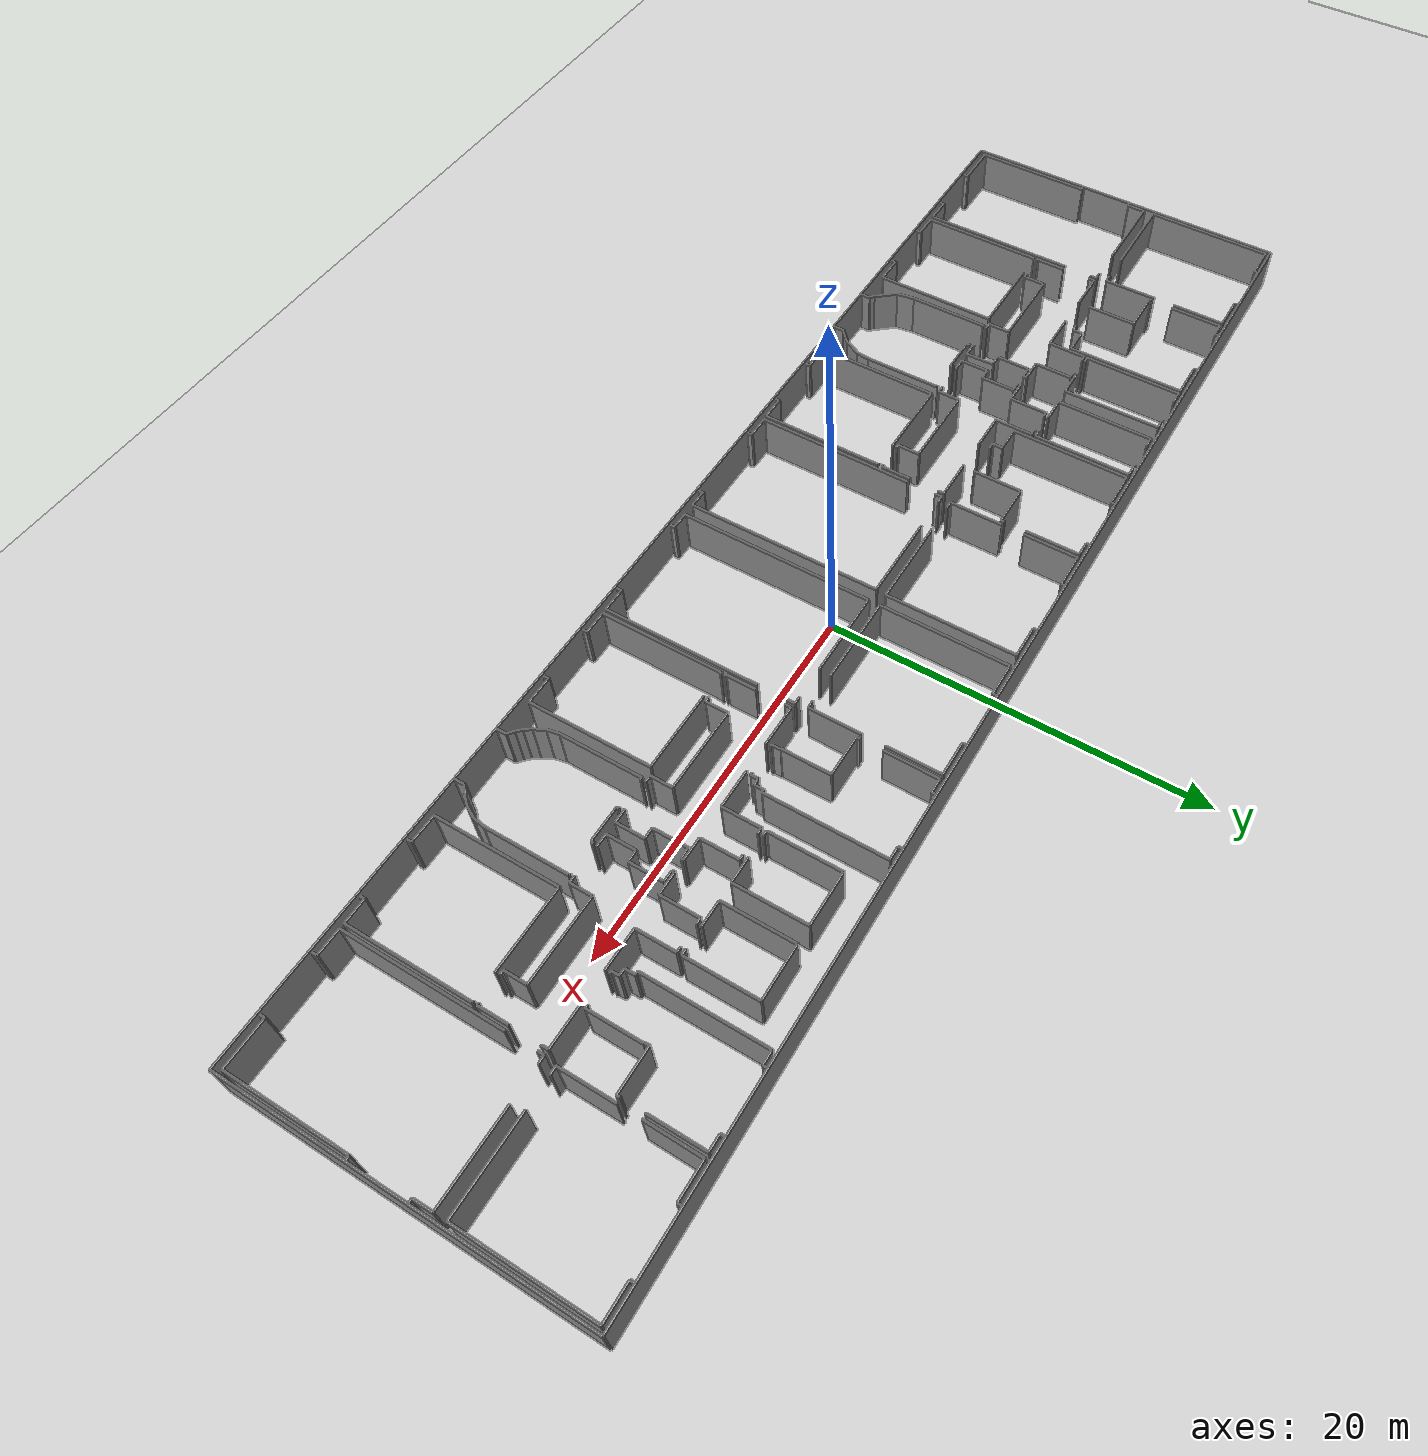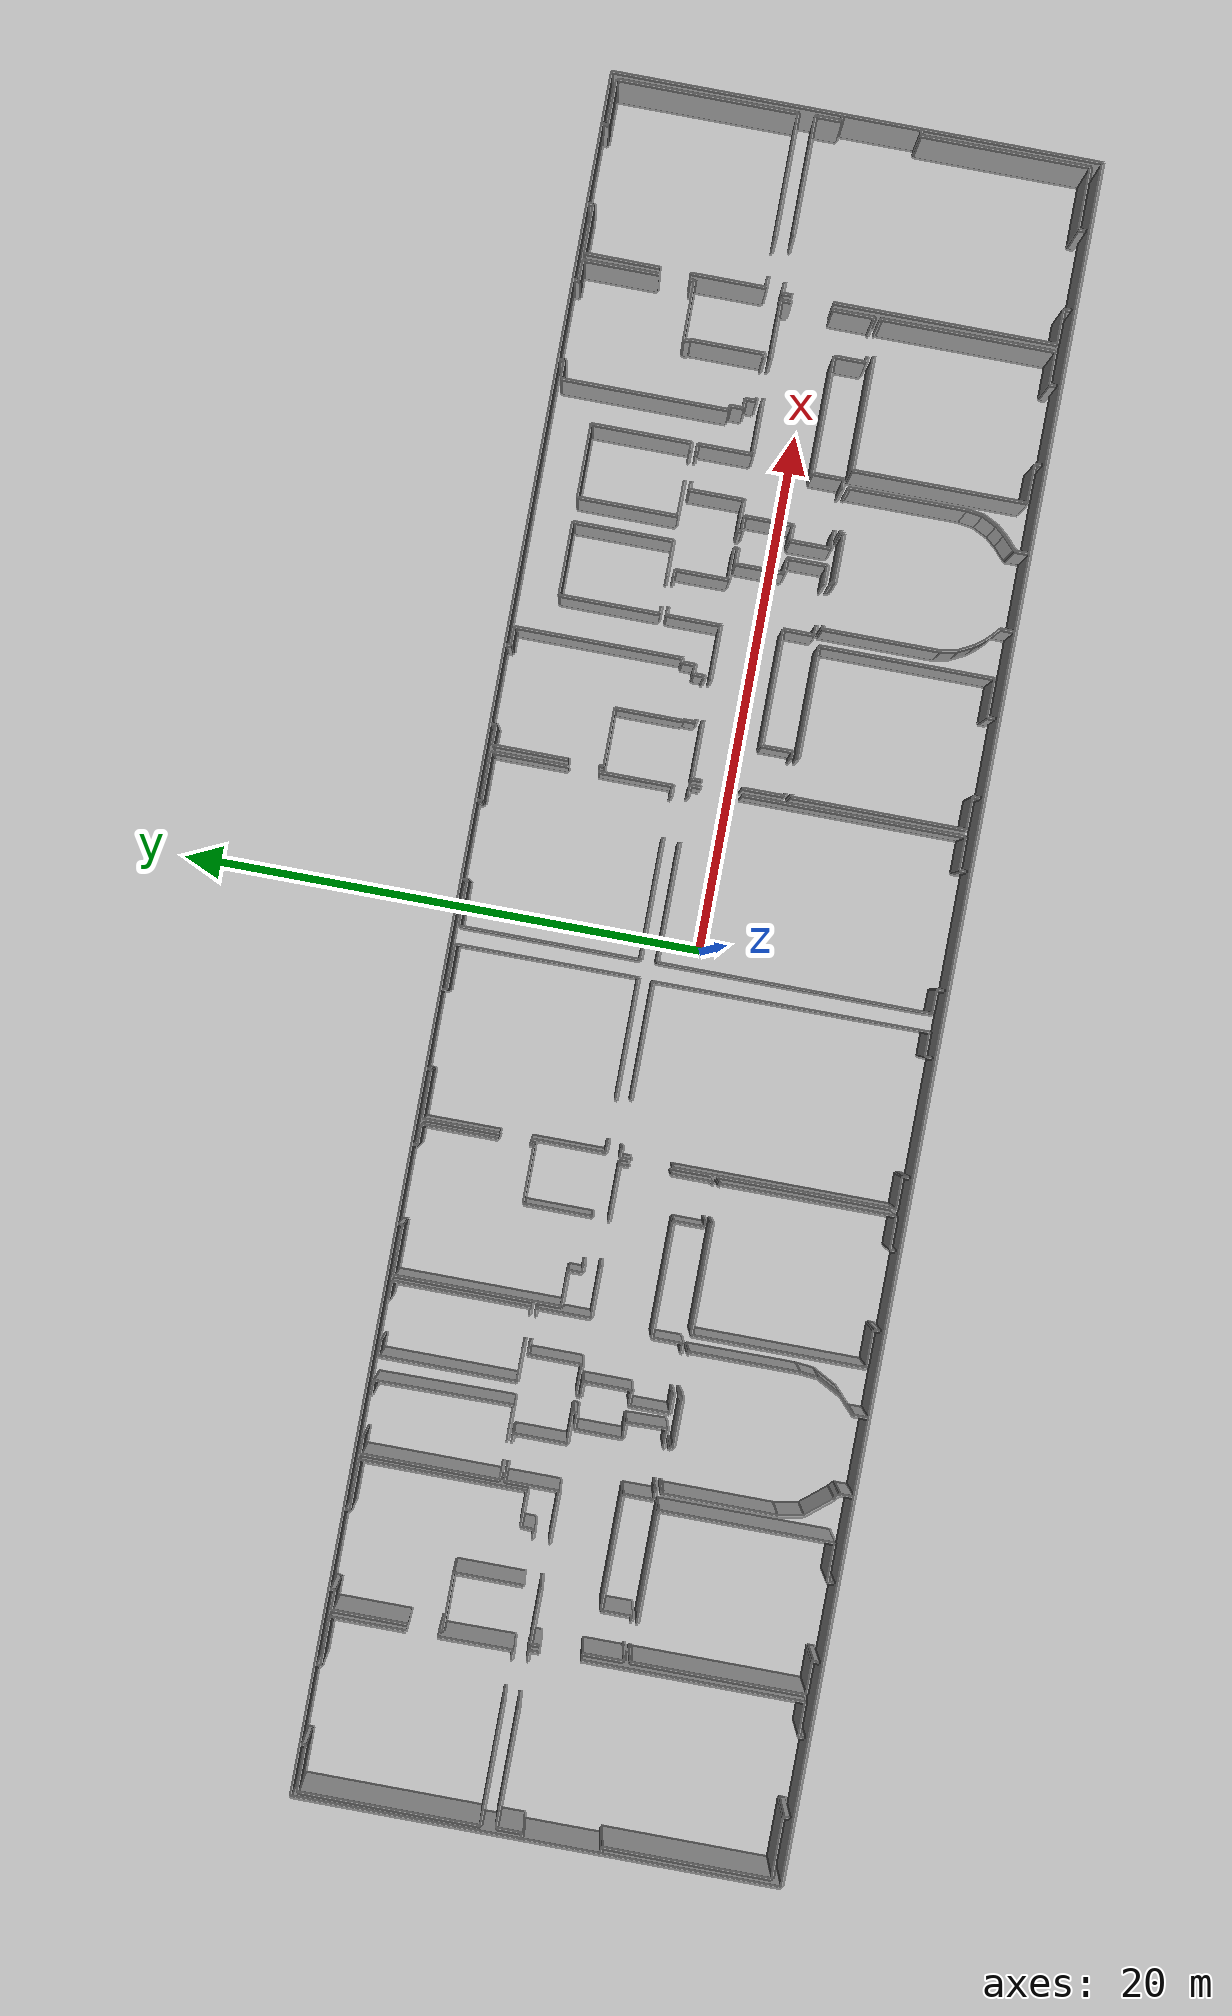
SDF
<sdf version="1.6">
  <world name="default">
    <light name="sun" type="directional">
      <cast_shadows>1</cast_shadows>
      <pose frame="">0 0 10 0 -0 0</pose>
      <diffuse>0.8 0.8 0.8 1</diffuse>
      <specular>0.1 0.1 0.1 1</specular>
      <attenuation>
        <range>1000</range>
        <constant>0.9</constant>
        <linear>0.01</linear>
        <quadratic>0.001</quadratic>
      </attenuation>
      <direction>-0.5 0.5 -1</direction>
    </light>
    <model name="ground_plane">
      <static>1</static>
      <link name="link">
        <collision name="collision">
          <geometry>
            <plane>
              <normal>0 0 1</normal>
              <size>100 100</size>
            </plane>
          </geometry>
          <surface>
            <friction>
              <ode>
                <mu>100</mu>
                <mu2>50</mu2>
              </ode>
              <torsional>
                <ode />
              </torsional>
            </friction>
            <contact>
              <ode />
            </contact>
            <bounce />
          </surface>
          <max_contacts>10</max_contacts>
        </collision>
        <visual name="visual">
          <cast_shadows>0</cast_shadows>
          <geometry>
            <plane>
              <normal>0 0 1</normal>
              <size>100 100</size>
            </plane>
          </geometry>
          <material>
            <script>
              <uri>file://media/materials/scripts/gazebo.material</uri>
              <name>Gazebo/Grey</name>
            </script>
          </material>
        </visual>
        <self_collide>0</self_collide>
        <kinematic>0</kinematic>
        <gravity>1</gravity>
      </link>
    </model>
    <gravity>0 0 -9.8</gravity>
    <magnetic_field>6e-06 2.3e-05 -4.2e-05</magnetic_field>
    <atmosphere type="adiabatic" />
    <physics default="0" name="default_physics" type="ode">
      <max_step_size>0.001</max_step_size>
      <real_time_factor>1</real_time_factor>
      <real_time_update_rate>1000</real_time_update_rate>
    </physics>
    <scene>
      <ambient>0.4 0.4 0.4 1</ambient>
      <background>0.7 0.7 0.7 1</background>
      <shadows>1</shadows>
    </scene>
    <spherical_coordinates>
      <surface_model>EARTH_WGS84</surface_model>
      <latitude_deg>0</latitude_deg>
      <longitude_deg>0</longitude_deg>
      <elevation>0</elevation>
      <heading_deg>0</heading_deg>
    </spherical_coordinates>
  <model name="0510034841_A-40">
		<static>1</static>
		<link name="Wall_0">
			<collision name="Wall_0_Collision">
				<geometry>
					<box>
						<size>0.391235909414 0.1 2.5</size>
					</box>
				</geometry>
				<pose frame="">0.195617954707 0 1.25 0 0 0</pose>
			</collision>
			<visual name="Wall_0_Visual">
				<pose frame="">0.195617954707 0 1.25 0 0 0</pose>
				<geometry>
					<box>
						<size>0.391235909414 0.1 2.5</size>
					</box>
				</geometry>
				<material>
					<script>
						<uri>file://media/materials/scripts/gazebo.material</uri>
						<name>Gazebo/Grey</name>
					</script>
					<ambient>1 1 1 1</ambient>
				</material>
			</visual>
			<pose frame="">6.86668528486 -7.17820148269 0 0 0 3.14159265359</pose>
		</link>
		<link name="Wall_1">
			<collision name="Wall_1_Collision">
				<geometry>
					<box>
						<size>4.6958464507 0.1 2.5</size>
					</box>
				</geometry>
				<pose frame="">2.34792322535 0 1.25 0 0 0</pose>
			</collision>
			<visual name="Wall_1_Visual">
				<pose frame="">2.34792322535 0 1.25 0 0 0</pose>
				<geometry>
					<box>
						<size>4.6958464507 0.1 2.5</size>
					</box>
				</geometry>
				<material>
					<script>
						<uri>file://media/materials/scripts/gazebo.material</uri>
						<name>Gazebo/Grey</name>
					</script>
					<ambient>1 1 1 1</ambient>
				</material>
			</visual>
			<pose frame="">4.89603432518 -7.17820148269 0 0 0 3.14159265359</pose>
		</link>
		<link name="Wall_2">
			<collision name="Wall_2_Collision">
				<geometry>
					<box>
						<size>6.9532598761 0.1 2.5</size>
					</box>
				</geometry>
				<pose frame="">3.47662993805 0 1.25 0 0 0</pose>
			</collision>
			<visual name="Wall_2_Visual">
				<pose frame="">3.47662993805 0 1.25 0 0 0</pose>
				<geometry>
					<box>
						<size>6.9532598761 0.1 2.5</size>
					</box>
				</geometry>
				<material>
					<script>
						<uri>file://media/materials/scripts/gazebo.material</uri>
						<name>Gazebo/Grey</name>
					</script>
					<ambient>1 1 1 1</ambient>
				</material>
			</visual>
			<pose frame="">0.20018787448 -7.17820148269 0 0 0 1.57079632679</pose>
		</link>
		<link name="Wall_3">
			<collision name="Wall_3_Collision">
				<geometry>
					<box>
						<size>1.75675332589 0.1 2.5</size>
					</box>
				</geometry>
				<pose frame="">0.878376662943 0 1.25 0 0 0</pose>
			</collision>
			<visual name="Wall_3_Visual">
				<pose frame="">0.878376662943 0 1.25 0 0 0</pose>
				<geometry>
					<box>
						<size>1.75675332589 0.1 2.5</size>
					</box>
				</geometry>
				<material>
					<script>
						<uri>file://media/materials/scripts/gazebo.material</uri>
						<name>Gazebo/Grey</name>
					</script>
					<ambient>1 1 1 1</ambient>
				</material>
			</visual>
			<pose frame="">0.20018787448 -0.224941606581 0 0 0 0.0</pose>
		</link>
		<link name="Wall_4">
			<collision name="Wall_4_Collision">
				<geometry>
					<box>
						<size>0.191936630446 0.1 2.5</size>
					</box>
				</geometry>
				<pose frame="">0.0959683152229 0 1.25 0 0 0</pose>
			</collision>
			<visual name="Wall_4_Visual">
				<pose frame="">0.0959683152229 0 1.25 0 0 0</pose>
				<geometry>
					<box>
						<size>0.191936630446 0.1 2.5</size>
					</box>
				</geometry>
				<material>
					<script>
						<uri>file://media/materials/scripts/gazebo.material</uri>
						<name>Gazebo/Grey</name>
					</script>
					<ambient>1 1 1 1</ambient>
				</material>
			</visual>
			<pose frame="">1.95694120037 -0.224941606581 0 0 0 1.57079632679</pose>
		</link>
		<link name="Wall_5">
			<collision name="Wall_5_Collision">
				<geometry>
					<box>
						<size>0.202726718798 0.1 2.5</size>
					</box>
				</geometry>
				<pose frame="">0.101363359399 0 1.25 0 0 0</pose>
			</collision>
			<visual name="Wall_5_Visual">
				<pose frame="">0.101363359399 0 1.25 0 0 0</pose>
				<geometry>
					<box>
						<size>0.202726718798 0.1 2.5</size>
					</box>
				</geometry>
				<material>
					<script>
						<uri>file://media/materials/scripts/gazebo.material</uri>
						<name>Gazebo/Grey</name>
					</script>
					<ambient>1 1 1 1</ambient>
				</material>
			</visual>
			<pose frame="">4.97968924546 -0.0330049761349 0 0 0 -1.57079632679</pose>
		</link>
		<link name="Wall_6">
			<collision name="Wall_6_Collision">
				<geometry>
					<box>
						<size>1.86173453844 0.1 2.5</size>
					</box>
				</geometry>
				<pose frame="">0.930867269219 0 1.25 0 0 0</pose>
			</collision>
			<visual name="Wall_6_Visual">
				<pose frame="">0.930867269219 0 1.25 0 0 0</pose>
				<geometry>
					<box>
						<size>1.86173453844 0.1 2.5</size>
					</box>
				</geometry>
				<material>
					<script>
						<uri>file://media/materials/scripts/gazebo.material</uri>
						<name>Gazebo/Grey</name>
					</script>
					<ambient>1 1 1 1</ambient>
				</material>
			</visual>
			<pose frame="">4.97968924546 -0.235731694932 0 0 0 0.0</pose>
		</link>
		<link name="Wall_7">
			<collision name="Wall_7_Collision">
				<geometry>
					<box>
						<size>2.88806235402 0.1 2.5</size>
					</box>
				</geometry>
				<pose frame="">1.44403117701 0 1.25 0 0 0</pose>
			</collision>
			<visual name="Wall_7_Visual">
				<pose frame="">1.44403117701 0 1.25 0 0 0</pose>
				<geometry>
					<box>
						<size>2.88806235402 0.1 2.5</size>
					</box>
				</geometry>
				<material>
					<script>
						<uri>file://media/materials/scripts/gazebo.material</uri>
						<name>Gazebo/Grey</name>
					</script>
					<ambient>1 1 1 1</ambient>
				</material>
			</visual>
			<pose frame="">6.84142378389 -0.235731694932 0 0 0 -1.57079632679</pose>
		</link>
		<link name="Wall_8">
			<collision name="Wall_8_Collision">
				<geometry>
					<box>
						<size>2.88601489635 0.1 2.5</size>
					</box>
				</geometry>
				<pose frame="">1.44300744818 0 1.25 0 0 0</pose>
			</collision>
			<visual name="Wall_8_Visual">
				<pose frame="">1.44300744818 0 1.25 0 0 0</pose>
				<geometry>
					<box>
						<size>2.88601489635 0.1 2.5</size>
					</box>
				</geometry>
				<material>
					<script>
						<uri>file://media/materials/scripts/gazebo.material</uri>
						<name>Gazebo/Grey</name>
					</script>
					<ambient>1 1 1 1</ambient>
				</material>
			</visual>
			<pose frame="">6.84142378389 -4.29229714634 0 0 0 -1.56204314136</pose>
		</link>
		<link name="Wall_9">
			<collision name="Wall_9_Collision">
				<geometry>
					<box>
						<size>0.348456382655 0.1 2.5</size>
					</box>
				</geometry>
				<pose frame="">0.174228191327 0 1.25 0 0 0</pose>
			</collision>
			<visual name="Wall_9_Visual">
				<pose frame="">0.174228191327 0 1.25 0 0 0</pose>
				<geometry>
					<box>
						<size>0.348456382655 0.1 2.5</size>
					</box>
				</geometry>
				<material>
					<script>
						<uri>file://media/materials/scripts/gazebo.material</uri>
						<name>Gazebo/Grey</name>
					</script>
					<ambient>1 1 1 1</ambient>
				</material>
			</visual>
			<pose frame="">11.4282268711 -7.12298161877 0 0 0 3.14159265359</pose>
		</link>
		<link name="Wall_10">
			<collision name="Wall_10_Collision">
				<geometry>
					<box>
						<size>2.65791611658 0.1 2.5</size>
					</box>
				</geometry>
				<pose frame="">1.32895805829 0 1.25 0 0 0</pose>
			</collision>
			<visual name="Wall_10_Visual">
				<pose frame="">1.32895805829 0 1.25 0 0 0</pose>
				<geometry>
					<box>
						<size>2.65791611658 0.1 2.5</size>
					</box>
				</geometry>
				<material>
					<script>
						<uri>file://media/materials/scripts/gazebo.material</uri>
						<name>Gazebo/Grey</name>
					</script>
					<ambient>1 1 1 1</ambient>
				</material>
			</visual>
			<pose frame="">9.30194475475 -7.12298161877 0 0 0 1.57079632679</pose>
		</link>
		<link name="Wall_11">
			<collision name="Wall_11_Collision">
				<geometry>
					<box>
						<size>2.20346298365 0.1 2.5</size>
					</box>
				</geometry>
				<pose frame="">1.10173149182 0 1.25 0 0 0</pose>
			</collision>
			<visual name="Wall_11_Visual">
				<pose frame="">1.10173149182 0 1.25 0 0 0</pose>
				<geometry>
					<box>
						<size>2.20346298365 0.1 2.5</size>
					</box>
				</geometry>
				<material>
					<script>
						<uri>file://media/materials/scripts/gazebo.material</uri>
						<name>Gazebo/Grey</name>
					</script>
					<ambient>1 1 1 1</ambient>
				</material>
			</visual>
			<pose frame="">9.30194475475 -4.46506550218 0 0 0 3.14159265359</pose>
		</link>
		<link name="Wall_12">
			<collision name="Wall_12_Collision">
				<geometry>
					<box>
						<size>0.15029958363 0.1 2.5</size>
					</box>
				</geometry>
				<pose frame="">0.0751497918148 0 1.25 0 0 0</pose>
			</collision>
			<visual name="Wall_12_Visual">
				<pose frame="">0.0751497918148 0 1.25 0 0 0</pose>
				<geometry>
					<box>
						<size>0.15029958363 0.1 2.5</size>
					</box>
				</geometry>
				<material>
					<script>
						<uri>file://media/materials/scripts/gazebo.material</uri>
						<name>Gazebo/Grey</name>
					</script>
					<ambient>1 1 1 1</ambient>
				</material>
			</visual>
			<pose frame="">7.0984817711 -4.46506550218 0 0 0 1.57079632679</pose>
		</link>
		<link name="Wall_13">
			<collision name="Wall_13_Collision">
				<geometry>
					<box>
						<size>2.88691987407 0.1 2.5</size>
					</box>
				</geometry>
				<pose frame="">1.44345993704 0 1.25 0 0 0</pose>
			</collision>
			<visual name="Wall_13_Visual">
				<pose frame="">1.44345993704 0 1.25 0 0 0</pose>
				<geometry>
					<box>
						<size>2.88691987407 0.1 2.5</size>
					</box>
				</geometry>
				<material>
					<script>
						<uri>file://media/materials/scripts/gazebo.material</uri>
						<name>Gazebo/Grey</name>
					</script>
					<ambient>1 1 1 1</ambient>
				</material>
			</visual>
			<pose frame="">7.0984817711 -3.13394942622 0 0 0 1.57079632679</pose>
		</link>
		<link name="Wall_14">
			<collision name="Wall_14_Collision">
				<geometry>
					<box>
						<size>0.747816593886 0.1 2.5</size>
					</box>
				</geometry>
				<pose frame="">0.373908296943 0 1.25 0 0 0</pose>
			</collision>
			<visual name="Wall_14_Visual">
				<pose frame="">0.373908296943 0 1.25 0 0 0</pose>
				<geometry>
					<box>
						<size>0.747816593886 0.1 2.5</size>
					</box>
				</geometry>
				<material>
					<script>
						<uri>file://media/materials/scripts/gazebo.material</uri>
						<name>Gazebo/Grey</name>
					</script>
					<ambient>1 1 1 1</ambient>
				</material>
			</visual>
			<pose frame="">7.0984817711 -0.247029552148 0 0 0 0.0</pose>
		</link>
		<link name="Wall_15">
			<collision name="Wall_15_Collision">
				<geometry>
					<box>
						<size>0.23052706408 0.1 2.5</size>
					</box>
				</geometry>
				<pose frame="">0.11526353204 0 1.25 0 0 0</pose>
			</collision>
			<visual name="Wall_15_Visual">
				<pose frame="">0.11526353204 0 1.25 0 0 0</pose>
				<geometry>
					<box>
						<size>0.23052706408 0.1 2.5</size>
					</box>
				</geometry>
				<material>
					<script>
						<uri>file://media/materials/scripts/gazebo.material</uri>
						<name>Gazebo/Grey</name>
					</script>
					<ambient>1 1 1 1</ambient>
				</material>
			</visual>
			<pose frame="">7.84629836498 -0.247029552148 0 0 0 1.57079632679</pose>
		</link>
		<link name="Wall_16">
			<collision name="Wall_16_Collision">
				<geometry>
					<box>
						<size>0.225068548797 0.1 2.5</size>
					</box>
				</geometry>
				<pose frame="">0.112534274398 0 1.25 0 0 0</pose>
			</collision>
			<visual name="Wall_16_Visual">
				<pose frame="">0.112534274398 0 1.25 0 0 0</pose>
				<geometry>
					<box>
						<size>0.225068548797 0.1 2.5</size>
					</box>
				</geometry>
				<material>
					<script>
						<uri>file://media/materials/scripts/gazebo.material</uri>
						<name>Gazebo/Grey</name>
					</script>
					<ambient>1 1 1 1</ambient>
				</material>
			</visual>
			<pose frame="">10.8703158322 -0.0165024880674 0 0 0 -1.57079632679</pose>
		</link>
		<link name="Wall_17">
			<collision name="Wall_17_Collision">
				<geometry>
					<box>
						<size>1.9292677973 0.1 2.5</size>
					</box>
				</geometry>
				<pose frame="">0.964633898649 0 1.25 0 0 0</pose>
			</collision>
			<visual name="Wall_17_Visual">
				<pose frame="">0.964633898649 0 1.25 0 0 0</pose>
				<geometry>
					<box>
						<size>1.9292677973 0.1 2.5</size>
					</box>
				</geometry>
				<material>
					<script>
						<uri>file://media/materials/scripts/gazebo.material</uri>
						<name>Gazebo/Grey</name>
					</script>
					<ambient>1 1 1 1</ambient>
				</material>
			</visual>
			<pose frame="">10.8703158322 -0.241571036864 0 0 0 0.0</pose>
		</link>
		<link name="Wall_18">
			<collision name="Wall_18_Collision">
				<geometry>
					<box>
						<size>6.36602518534 0.1 2.5</size>
					</box>
				</geometry>
				<pose frame="">3.18301259267 0 1.25 0 0 0</pose>
			</collision>
			<visual name="Wall_18_Visual">
				<pose frame="">3.18301259267 0 1.25 0 0 0</pose>
				<geometry>
					<box>
						<size>6.36602518534 0.1 2.5</size>
					</box>
				</geometry>
				<material>
					<script>
						<uri>file://media/materials/scripts/gazebo.material</uri>
						<name>Gazebo/Grey</name>
					</script>
					<ambient>1 1 1 1</ambient>
				</material>
			</visual>
			<pose frame="">12.7995836295 -0.241571036864 0 0 0 -1.57079632679</pose>
		</link>
		<link name="Wall_19">
			<collision name="Wall_19_Collision">
				<geometry>
					<box>
						<size>1.35333096375 0.1 2.5</size>
					</box>
				</geometry>
				<pose frame="">0.676665481873 0 1.25 0 0 0</pose>
			</collision>
			<visual name="Wall_19_Visual">
				<pose frame="">0.676665481873 0 1.25 0 0 0</pose>
				<geometry>
					<box>
						<size>1.35333096375 0.1 2.5</size>
					</box>
				</geometry>
				<material>
					<script>
						<uri>file://media/materials/scripts/gazebo.material</uri>
						<name>Gazebo/Grey</name>
					</script>
					<ambient>1 1 1 1</ambient>
				</material>
			</visual>
			<pose frame="">12.7995836295 -6.6075962222 0 0 0 3.14159265359</pose>
		</link>
		<link name="Wall_20">
			<collision name="Wall_20_Collision">
				<geometry>
					<box>
						<size>0.515700529637 0.1 2.5</size>
					</box>
				</geometry>
				<pose frame="">0.257850264819 0 1.25 0 0 0</pose>
			</collision>
			<visual name="Wall_20_Visual">
				<pose frame="">0.257850264819 0 1.25 0 0 0</pose>
				<geometry>
					<box>
						<size>0.515700529637 0.1 2.5</size>
					</box>
				</geometry>
				<material>
					<script>
						<uri>file://media/materials/scripts/gazebo.material</uri>
						<name>Gazebo/Grey</name>
					</script>
					<ambient>1 1 1 1</ambient>
				</material>
			</visual>
			<pose frame="">11.4462526658 -6.6075962222 0 0 0 -1.6057574452</pose>
		</link>
		<link name="Wall_21">
			<collision name="Wall_21_Collision">
				<geometry>
					<box>
						<size>1.33530516909 0.1 2.5</size>
					</box>
				</geometry>
				<pose frame="">0.667652584544 0 1.25 0 0 0</pose>
			</collision>
			<visual name="Wall_21_Visual">
				<pose frame="">0.667652584544 0 1.25 0 0 0</pose>
				<geometry>
					<box>
						<size>1.33530516909 0.1 2.5</size>
					</box>
				</geometry>
				<material>
					<script>
						<uri>file://media/materials/scripts/gazebo.material</uri>
						<name>Gazebo/Grey</name>
					</script>
					<ambient>1 1 1 1</ambient>
				</material>
			</visual>
			<pose frame="">6.95732202701 -18.2493399005 0 0 0 3.14159265359</pose>
		</link>
		<link name="Wall_22">
			<collision name="Wall_22_Collision">
				<geometry>
					<box>
						<size>0.227353508683 0.1 2.5</size>
					</box>
				</geometry>
				<pose frame="">0.113676754341 0 1.25 0 0 0</pose>
			</collision>
			<visual name="Wall_22_Visual">
				<pose frame="">0.113676754341 0 1.25 0 0 0</pose>
				<geometry>
					<box>
						<size>0.227353508683 0.1 2.5</size>
					</box>
				</geometry>
				<material>
					<script>
						<uri>file://media/materials/scripts/gazebo.material</uri>
						<name>Gazebo/Grey</name>
					</script>
					<ambient>1 1 1 1</ambient>
				</material>
			</visual>
			<pose frame="">5.62201685793 -18.2493399005 0 0 0 -1.57079632679</pose>
		</link>
		<link name="Wall_23">
			<collision name="Wall_23_Collision">
				<geometry>
					<box>
						<size>0.243348227887 0.1 2.5</size>
					</box>
				</geometry>
				<pose frame="">0.121674113943 0 1.25 0 0 0</pose>
			</collision>
			<visual name="Wall_23_Visual">
				<pose frame="">0.121674113943 0 1.25 0 0 0</pose>
				<geometry>
					<box>
						<size>0.243348227887 0.1 2.5</size>
					</box>
				</geometry>
				<material>
					<script>
						<uri>file://media/materials/scripts/gazebo.material</uri>
						<name>Gazebo/Grey</name>
					</script>
					<ambient>1 1 1 1</ambient>
				</material>
			</visual>
			<pose frame="">2.59165227988 -18.4766934092 0 0 0 1.57079632679</pose>
		</link>
		<link name="Wall_24">
			<collision name="Wall_24_Collision">
				<geometry>
					<box>
						<size>2.34792322535 0.1 2.5</size>
					</box>
				</geometry>
				<pose frame="">1.17396161267 0 1.25 0 0 0</pose>
			</collision>
			<visual name="Wall_24_Visual">
				<pose frame="">1.17396161267 0 1.25 0 0 0</pose>
				<geometry>
					<box>
						<size>2.34792322535 0.1 2.5</size>
					</box>
				</geometry>
				<material>
					<script>
						<uri>file://media/materials/scripts/gazebo.material</uri>
						<name>Gazebo/Grey</name>
					</script>
					<ambient>1 1 1 1</ambient>
				</material>
			</visual>
			<pose frame="">2.59165227988 -18.2333451813 0 0 0 3.14159265359</pose>
		</link>
		<link name="Wall_25">
			<collision name="Wall_25_Collision">
				<geometry>
					<box>
						<size>6.46059713618 0.1 2.5</size>
					</box>
				</geometry>
				<pose frame="">3.23029856809 0 1.25 0 0 0</pose>
			</collision>
			<visual name="Wall_25_Visual">
				<pose frame="">3.23029856809 0 1.25 0 0 0</pose>
				<geometry>
					<box>
						<size>6.46059713618 0.1 2.5</size>
					</box>
				</geometry>
				<material>
					<script>
						<uri>file://media/materials/scripts/gazebo.material</uri>
						<name>Gazebo/Grey</name>
					</script>
					<ambient>1 1 1 1</ambient>
				</material>
			</visual>
			<pose frame="">0.243729054534 -18.2333451813 0 0 0 1.57079632679</pose>
		</link>
		<link name="Wall_26">
			<collision name="Wall_26_Collision">
				<geometry>
					<box>
						<size>0.243729054534 0.1 2.5</size>
					</box>
				</geometry>
				<pose frame="">0.121864527267 0 1.25 0 0 0</pose>
			</collision>
			<visual name="Wall_26_Visual">
				<pose frame="">0.121864527267 0 1.25 0 0 0</pose>
				<geometry>
					<box>
						<size>0.243729054534 0.1 2.5</size>
					</box>
				</geometry>
				<material>
					<script>
						<uri>file://media/materials/scripts/gazebo.material</uri>
						<name>Gazebo/Grey</name>
					</script>
					<ambient>1 1 1 1</ambient>
				</material>
			</visual>
			<pose frame="">0.243729054534 -11.7727480451 0 0 0 3.14159265359</pose>
		</link>
		<link name="Wall_27">
			<collision name="Wall_27_Collision">
				<geometry>
					<box>
						<size>0.227226566467 0.1 2.5</size>
					</box>
				</geometry>
				<pose frame="">0.113613283233 0 1.25 0 0 0</pose>
			</collision>
			<visual name="Wall_27_Visual">
				<pose frame="">0.113613283233 0 1.25 0 0 0</pose>
				<geometry>
					<box>
						<size>0.227226566467 0.1 2.5</size>
					</box>
				</geometry>
				<material>
					<script>
						<uri>file://media/materials/scripts/gazebo.material</uri>
						<name>Gazebo/Grey</name>
					</script>
					<ambient>1 1 1 1</ambient>
				</material>
			</visual>
			<pose frame="">0.0 -8.76231339494 0 0 0 0.0</pose>
		</link>
		<link name="Wall_28">
			<collision name="Wall_28_Collision">
				<geometry>
					<box>
						<size>0.990910937341 0.1 2.5</size>
					</box>
				</geometry>
				<pose frame="">0.495455468671 0 1.25 0 0 0</pose>
			</collision>
			<visual name="Wall_28_Visual">
				<pose frame="">0.495455468671 0 1.25 0 0 0</pose>
				<geometry>
					<box>
						<size>0.990910937341 0.1 2.5</size>
					</box>
				</geometry>
				<material>
					<script>
						<uri>file://media/materials/scripts/gazebo.material</uri>
						<name>Gazebo/Grey</name>
					</script>
					<ambient>1 1 1 1</ambient>
				</material>
			</visual>
			<pose frame="">0.227226566467 -8.76231339494 0 0 0 1.57079632679</pose>
		</link>
		<link name="Wall_29">
			<collision name="Wall_29_Collision">
				<geometry>
					<box>
						<size>4.55544835991 0.1 2.5</size>
					</box>
				</geometry>
				<pose frame="">2.27772417995 0 1.25 0 0 0</pose>
			</collision>
			<visual name="Wall_29_Visual">
				<pose frame="">2.27772417995 0 1.25 0 0 0</pose>
				<geometry>
					<box>
						<size>4.55544835991 0.1 2.5</size>
					</box>
				</geometry>
				<material>
					<script>
						<uri>file://media/materials/scripts/gazebo.material</uri>
						<name>Gazebo/Grey</name>
					</script>
					<ambient>1 1 1 1</ambient>
				</material>
			</visual>
			<pose frame="">0.227226566467 -7.7714024576 0 0 0 0.0</pose>
		</link>
		<link name="Wall_30">
			<collision name="Wall_30_Collision">
				<geometry>
					<box>
						<size>0.411673606174 0.1 2.5</size>
					</box>
				</geometry>
				<pose frame="">0.205836803087 0 1.25 0 0 0</pose>
			</collision>
			<visual name="Wall_30_Visual">
				<pose frame="">0.205836803087 0 1.25 0 0 0</pose>
				<geometry>
					<box>
						<size>0.411673606174 0.1 2.5</size>
					</box>
				</geometry>
				<material>
					<script>
						<uri>file://media/materials/scripts/gazebo.material</uri>
						<name>Gazebo/Grey</name>
					</script>
					<ambient>1 1 1 1</ambient>
				</material>
			</visual>
			<pose frame="">6.54564842084 -7.7714024576 0 0 0 0.0</pose>
		</link>
		<link name="Wall_31">
			<collision name="Wall_31_Collision">
				<geometry>
					<box>
						<size>0.378414745608 0.1 2.5</size>
					</box>
				</geometry>
				<pose frame="">0.189207372804 0 1.25 0 0 0</pose>
			</collision>
			<visual name="Wall_31_Visual">
				<pose frame="">0.189207372804 0 1.25 0 0 0</pose>
				<geometry>
					<box>
						<size>0.378414745608 0.1 2.5</size>
					</box>
				</geometry>
				<material>
					<script>
						<uri>file://media/materials/scripts/gazebo.material</uri>
						<name>Gazebo/Grey</name>
					</script>
					<ambient>1 1 1 1</ambient>
				</material>
			</visual>
			<pose frame="">6.95732202701 -7.7714024576 0 0 0 -1.57079632679</pose>
		</link>
		<link name="Wall_32">
			<collision name="Wall_32_Collision">
				<geometry>
					<box>
						<size>8.51401442064 0.1 2.5</size>
					</box>
				</geometry>
				<pose frame="">4.25700721032 0 1.25 0 0 0</pose>
			</collision>
			<visual name="Wall_32_Visual">
				<pose frame="">4.25700721032 0 1.25 0 0 0</pose>
				<geometry>
					<box>
						<size>8.51401442064 0.1 2.5</size>
					</box>
				</geometry>
				<material>
					<script>
						<uri>file://media/materials/scripts/gazebo.material</uri>
						<name>Gazebo/Grey</name>
					</script>
					<ambient>1 1 1 1</ambient>
				</material>
			</visual>
			<pose frame="">6.95732202701 -9.73532547984 0 0 0 -1.57079632679</pose>
		</link>
		<link name="Wall_33">
			<collision name="Wall_33_Collision">
				<geometry>
					<box>
						<size>1.48166954402 0.1 2.5</size>
					</box>
				</geometry>
				<pose frame="">0.740834772012 0 1.25 0 0 0</pose>
			</collision>
			<visual name="Wall_33_Visual">
				<pose frame="">0.740834772012 0 1.25 0 0 0</pose>
				<geometry>
					<box>
						<size>1.48166954402 0.1 2.5</size>
					</box>
				</geometry>
				<material>
					<script>
						<uri>file://media/materials/scripts/gazebo.material</uri>
						<name>Gazebo/Grey</name>
					</script>
					<ambient>1 1 1 1</ambient>
				</material>
			</visual>
			<pose frame="">12.988600589 -18.2421041942 0 0 0 3.14159265359</pose>
		</link>
		<link name="Wall_34">
			<collision name="Wall_34_Collision">
				<geometry>
					<box>
						<size>0.247156494364 0.1 2.5</size>
					</box>
				</geometry>
				<pose frame="">0.123578247182 0 1.25 0 0 0</pose>
			</collision>
			<visual name="Wall_34_Visual">
				<pose frame="">0.123578247182 0 1.25 0 0 0</pose>
				<geometry>
					<box>
						<size>0.247156494364 0.1 2.5</size>
					</box>
				</geometry>
				<material>
					<script>
						<uri>file://media/materials/scripts/gazebo.material</uri>
						<name>Gazebo/Grey</name>
					</script>
					<ambient>1 1 1 1</ambient>
				</material>
			</visual>
			<pose frame="">11.506931045 -18.2421041942 0 0 0 -1.57079632679</pose>
		</link>
		<link name="Wall_35">
			<collision name="Wall_35_Collision">
				<geometry>
					<box>
						<size>0.246902609932 0.1 2.5</size>
					</box>
				</geometry>
				<pose frame="">0.123451304966 0 1.25 0 0 0</pose>
			</collision>
			<visual name="Wall_35_Visual">
				<pose frame="">0.123451304966 0 1.25 0 0 0</pose>
				<geometry>
					<box>
						<size>0.246902609932 0.1 2.5</size>
					</box>
				</geometry>
				<material>
					<script>
						<uri>file://media/materials/scripts/gazebo.material</uri>
						<name>Gazebo/Grey</name>
					</script>
					<ambient>1 1 1 1</ambient>
				</material>
			</visual>
			<pose frame="">8.49941606581 -18.4892606885 0 0 0 1.57079632679</pose>
		</link>
		<link name="Wall_36">
			<collision name="Wall_36_Collision">
				<geometry>
					<box>
						<size>1.27323042551 0.1 2.5</size>
					</box>
				</geometry>
				<pose frame="">0.636615212755 0 1.25 0 0 0</pose>
			</collision>
			<visual name="Wall_36_Visual">
				<pose frame="">0.636615212755 0 1.25 0 0 0</pose>
				<geometry>
					<box>
						<size>1.27323042551 0.1 2.5</size>
					</box>
				</geometry>
				<material>
					<script>
						<uri>file://media/materials/scripts/gazebo.material</uri>
						<name>Gazebo/Grey</name>
					</script>
					<ambient>1 1 1 1</ambient>
				</material>
			</visual>
			<pose frame="">8.49941606581 -18.2423580786 0 0 0 3.14159265359</pose>
		</link>
		<link name="Wall_37">
			<collision name="Wall_37_Collision">
				<geometry>
					<box>
						<size>6.6954402356 0.1 2.5</size>
					</box>
				</geometry>
				<pose frame="">3.3477201178 0 1.25 0 0 0</pose>
			</collision>
			<visual name="Wall_37_Visual">
				<pose frame="">3.3477201178 0 1.25 0 0 0</pose>
				<geometry>
					<box>
						<size>6.6954402356 0.1 2.5</size>
					</box>
				</geometry>
				<material>
					<script>
						<uri>file://media/materials/scripts/gazebo.material</uri>
						<name>Gazebo/Grey</name>
					</script>
					<ambient>1 1 1 1</ambient>
				</material>
			</visual>
			<pose frame="">7.2261856403 -18.2423580786 0 0 0 1.57079632679</pose>
		</link>
		<link name="Wall_38">
			<collision name="Wall_38_Collision">
				<geometry>
					<box>
						<size>0.0823854981213 0.1 2.5</size>
					</box>
				</geometry>
				<pose frame="">0.0411927490606 0 1.25 0 0 0</pose>
			</collision>
			<visual name="Wall_38_Visual">
				<pose frame="">0.0411927490606 0 1.25 0 0 0</pose>
				<geometry>
					<box>
						<size>0.0823854981213 0.1 2.5</size>
					</box>
				</geometry>
				<material>
					<script>
						<uri>file://media/materials/scripts/gazebo.material</uri>
						<name>Gazebo/Grey</name>
					</script>
					<ambient>1 1 1 1</ambient>
				</material>
			</visual>
			<pose frame="">7.2261856403 -11.546917843 0 0 0 0.0</pose>
		</link>
		<link name="Wall_39">
			<collision name="Wall_39_Collision">
				<geometry>
					<box>
						<size>4.31222707424 0.1 2.5</size>
					</box>
				</geometry>
				<pose frame="">2.15611353712 0 1.25 0 0 0</pose>
			</collision>
			<visual name="Wall_39_Visual">
				<pose frame="">2.15611353712 0 1.25 0 0 0</pose>
				<geometry>
					<box>
						<size>4.31222707424 0.1 2.5</size>
					</box>
				</geometry>
				<material>
					<script>
						<uri>file://media/materials/scripts/gazebo.material</uri>
						<name>Gazebo/Grey</name>
					</script>
					<ambient>1 1 1 1</ambient>
				</material>
			</visual>
			<pose frame="">8.6701533462 -11.546917843 0 0 0 0.0</pose>
		</link>
		<link name="Wall_40">
			<collision name="Wall_40_Collision">
				<geometry>
					<box>
						<size>6.6951892406 0.1 2.5</size>
					</box>
				</geometry>
				<pose frame="">3.3475946203 0 1.25 0 0 0</pose>
			</collision>
			<visual name="Wall_40_Visual">
				<pose frame="">3.3475946203 0 1.25 0 0 0</pose>
				<geometry>
					<box>
						<size>6.6951892406 0.1 2.5</size>
					</box>
				</geometry>
				<material>
					<script>
						<uri>file://media/materials/scripts/gazebo.material</uri>
						<name>Gazebo/Grey</name>
					</script>
					<ambient>1 1 1 1</ambient>
				</material>
			</visual>
			<pose frame="">12.9823804204 -11.546917843 0 0 0 -1.56986727621</pose>
		</link>
		<link name="Wall_41">
			<collision name="Wall_41_Collision">
				<geometry>
					<box>
						<size>0.744516096273 0.1 2.5</size>
					</box>
				</geometry>
				<pose frame="">0.372258048136 0 1.25 0 0 0</pose>
			</collision>
			<visual name="Wall_41_Visual">
				<pose frame="">0.372258048136 0 1.25 0 0 0</pose>
				<geometry>
					<box>
						<size>0.744516096273 0.1 2.5</size>
					</box>
				</geometry>
				<material>
					<script>
						<uri>file://media/materials/scripts/gazebo.material</uri>
						<name>Gazebo/Grey</name>
					</script>
					<ambient>1 1 1 1</ambient>
				</material>
			</visual>
			<pose frame="">16.0339443485 -11.3138519346 0 0 0 3.14159265359</pose>
		</link>
		<link name="Wall_42">
			<collision name="Wall_42_Collision">
				<geometry>
					<box>
						<size>0.403041535493 0.1 2.5</size>
					</box>
				</geometry>
				<pose frame="">0.201520767747 0 1.25 0 0 0</pose>
			</collision>
			<visual name="Wall_42_Visual">
				<pose frame="">0.201520767747 0 1.25 0 0 0</pose>
				<geometry>
					<box>
						<size>0.403041535493 0.1 2.5</size>
					</box>
				</geometry>
				<material>
					<script>
						<uri>file://media/materials/scripts/gazebo.material</uri>
						<name>Gazebo/Grey</name>
					</script>
					<ambient>1 1 1 1</ambient>
				</material>
			</visual>
			<pose frame="">13.743525947 -11.3138519346 0 0 0 3.14159265359</pose>
		</link>
		<link name="Wall_43">
			<collision name="Wall_43_Collision">
				<geometry>
					<box>
						<size>1.18107037676 0.1 2.5</size>
					</box>
				</geometry>
				<pose frame="">0.590535188382 0 1.25 0 0 0</pose>
			</collision>
			<visual name="Wall_43_Visual">
				<pose frame="">0.590535188382 0 1.25 0 0 0</pose>
				<geometry>
					<box>
						<size>1.18107037676 0.1 2.5</size>
					</box>
				</geometry>
				<material>
					<script>
						<uri>file://media/materials/scripts/gazebo.material</uri>
						<name>Gazebo/Grey</name>
					</script>
					<ambient>1 1 1 1</ambient>
				</material>
			</visual>
			<pose frame="">13.3404844115 -11.3138519346 0 0 0 1.57079632679</pose>
		</link>
		<link name="Wall_44">
			<collision name="Wall_44_Collision">
				<geometry>
					<box>
						<size>4.42825225957 0.1 2.5</size>
					</box>
				</geometry>
				<pose frame="">2.21412612979 0 1.25 0 0 0</pose>
			</collision>
			<visual name="Wall_44_Visual">
				<pose frame="">2.21412612979 0 1.25 0 0 0</pose>
				<geometry>
					<box>
						<size>4.42825225957 0.1 2.5</size>
					</box>
				</geometry>
				<material>
					<script>
						<uri>file://media/materials/scripts/gazebo.material</uri>
						<name>Gazebo/Grey</name>
					</script>
					<ambient>1 1 1 1</ambient>
				</material>
			</visual>
			<pose frame="">13.3404844115 -10.1327815578 0 0 0 3.14159265359</pose>
		</link>
		<link name="Wall_45">
			<collision name="Wall_45_Collision">
				<geometry>
					<box>
						<size>1.1781507058 0.1 2.5</size>
					</box>
				</geometry>
				<pose frame="">0.589075352899 0 1.25 0 0 0</pose>
			</collision>
			<visual name="Wall_45_Visual">
				<pose frame="">0.589075352899 0 1.25 0 0 0</pose>
				<geometry>
					<box>
						<size>1.1781507058 0.1 2.5</size>
					</box>
				</geometry>
				<material>
					<script>
						<uri>file://media/materials/scripts/gazebo.material</uri>
						<name>Gazebo/Grey</name>
					</script>
					<ambient>1 1 1 1</ambient>
				</material>
			</visual>
			<pose frame="">8.91223215192 -10.1327815578 0 0 0 -1.57079632679</pose>
		</link>
		<link name="Wall_46">
			<collision name="Wall_46_Collision">
				<geometry>
					<box>
						<size>0.211231847263 0.1 2.5</size>
					</box>
				</geometry>
				<pose frame="">0.105615923632 0 1.25 0 0 0</pose>
			</collision>
			<visual name="Wall_46_Visual">
				<pose frame="">0.105615923632 0 1.25 0 0 0</pose>
				<geometry>
					<box>
						<size>0.211231847263 0.1 2.5</size>
					</box>
				</geometry>
				<material>
					<script>
						<uri>file://media/materials/scripts/gazebo.material</uri>
						<name>Gazebo/Grey</name>
					</script>
					<ambient>1 1 1 1</ambient>
				</material>
			</visual>
			<pose frame="">8.91223215192 -11.3109322636 0 0 0 3.14159265359</pose>
		</link>
		<link name="Wall_47">
			<collision name="Wall_47_Collision">
				<geometry>
					<box>
						<size>0.116913780847 0.1 2.5</size>
					</box>
				</geometry>
				<pose frame="">0.0584568904235 0 1.25 0 0 0</pose>
			</collision>
			<visual name="Wall_47_Visual">
				<pose frame="">0.0584568904235 0 1.25 0 0 0</pose>
				<geometry>
					<box>
						<size>0.116913780847 0.1 2.5</size>
					</box>
				</geometry>
				<material>
					<script>
						<uri>file://media/materials/scripts/gazebo.material</uri>
						<name>Gazebo/Grey</name>
					</script>
					<ambient>1 1 1 1</ambient>
				</material>
			</visual>
			<pose frame="">7.33218239058 -11.3109322636 0 0 0 3.14159265359</pose>
		</link>
		<link name="Wall_48">
			<collision name="Wall_48_Collision">
				<geometry>
					<box>
						<size>1.58753935209 0.1 2.5</size>
					</box>
				</geometry>
				<pose frame="">0.793769676043 0 1.25 0 0 0</pose>
			</collision>
			<visual name="Wall_48_Visual">
				<pose frame="">0.793769676043 0 1.25 0 0 0</pose>
				<geometry>
					<box>
						<size>1.58753935209 0.1 2.5</size>
					</box>
				</geometry>
				<material>
					<script>
						<uri>file://media/materials/scripts/gazebo.material</uri>
						<name>Gazebo/Grey</name>
					</script>
					<ambient>1 1 1 1</ambient>
				</material>
			</visual>
			<pose frame="">7.21526860973 -11.3109322636 0 0 0 1.57079632679</pose>
		</link>
		<link name="Wall_49">
			<collision name="Wall_49_Collision">
				<geometry>
					<box>
						<size>0.364831928506 0.1 2.5</size>
					</box>
				</geometry>
				<pose frame="">0.182415964253 0 1.25 0 0 0</pose>
			</collision>
			<visual name="Wall_49_Visual">
				<pose frame="">0.182415964253 0 1.25 0 0 0</pose>
				<geometry>
					<box>
						<size>0.364831928506 0.1 2.5</size>
					</box>
				</geometry>
				<material>
					<script>
						<uri>file://media/materials/scripts/gazebo.material</uri>
						<name>Gazebo/Grey</name>
					</script>
					<ambient>1 1 1 1</ambient>
				</material>
			</visual>
			<pose frame="">7.21526860973 -8.14347009241 0 0 0 1.57079632679</pose>
		</link>
		<link name="Wall_50">
			<collision name="Wall_50_Collision">
				<geometry>
					<box>
						<size>2.1096526861 0.1 2.5</size>
					</box>
				</geometry>
				<pose frame="">1.05482634305 0 1.25 0 0 0</pose>
			</collision>
			<visual name="Wall_50_Visual">
				<pose frame="">1.05482634305 0 1.25 0 0 0</pose>
				<geometry>
					<box>
						<size>2.1096526861 0.1 2.5</size>
					</box>
				</geometry>
				<material>
					<script>
						<uri>file://media/materials/scripts/gazebo.material</uri>
						<name>Gazebo/Grey</name>
					</script>
					<ambient>1 1 1 1</ambient>
				</material>
			</visual>
			<pose frame="">7.21526860973 -7.77863816391 0 0 0 0.0</pose>
		</link>
		<link name="Wall_51">
			<collision name="Wall_51_Collision">
				<geometry>
					<box>
						<size>1.99489692292 0.1 2.5</size>
					</box>
				</geometry>
				<pose frame="">0.99744846146 0 1.25 0 0 0</pose>
			</collision>
			<visual name="Wall_51_Visual">
				<pose frame="">0.99744846146 0 1.25 0 0 0</pose>
				<geometry>
					<box>
						<size>1.99489692292 0.1 2.5</size>
					</box>
				</geometry>
				<material>
					<script>
						<uri>file://media/materials/scripts/gazebo.material</uri>
						<name>Gazebo/Grey</name>
					</script>
					<ambient>1 1 1 1</ambient>
				</material>
			</visual>
			<pose frame="">11.0213770692 -7.77863816391 0 0 0 0.0</pose>
		</link>
		<link name="Wall_52">
			<collision name="Wall_52_Collision">
				<geometry>
					<box>
						<size>2.06991977252 0.1 2.5</size>
					</box>
				</geometry>
				<pose frame="">1.03495988626 0 1.25 0 0 0</pose>
			</collision>
			<visual name="Wall_52_Visual">
				<pose frame="">1.03495988626 0 1.25 0 0 0</pose>
				<geometry>
					<box>
						<size>2.06991977252 0.1 2.5</size>
					</box>
				</geometry>
				<material>
					<script>
						<uri>file://media/materials/scripts/gazebo.material</uri>
						<name>Gazebo/Grey</name>
					</script>
					<ambient>1 1 1 1</ambient>
				</material>
			</visual>
			<pose frame="">13.0162739921 -7.77863816391 0 0 0 1.57079632679</pose>
		</link>
		<link name="Wall_53">
			<collision name="Wall_53_Collision">
				<geometry>
					<box>
						<size>0.325479841576 0.1 2.5</size>
					</box>
				</geometry>
				<pose frame="">0.162739920788 0 1.25 0 0 0</pose>
			</collision>
			<visual name="Wall_53_Visual">
				<pose frame="">0.162739920788 0 1.25 0 0 0</pose>
				<geometry>
					<box>
						<size>0.325479841576 0.1 2.5</size>
					</box>
				</geometry>
				<material>
					<script>
						<uri>file://media/materials/scripts/gazebo.material</uri>
						<name>Gazebo/Grey</name>
					</script>
					<ambient>1 1 1 1</ambient>
				</material>
			</visual>
			<pose frame="">13.0162739921 -5.70871839139 0 0 0 0.0</pose>
		</link>
		<link name="Wall_54">
			<collision name="Wall_54_Collision">
				<geometry>
					<box>
						<size>0.321798517315 0.1 2.5</size>
					</box>
				</geometry>
				<pose frame="">0.160899258657 0 1.25 0 0 0</pose>
			</collision>
			<visual name="Wall_54_Visual">
				<pose frame="">0.160899258657 0 1.25 0 0 0</pose>
				<geometry>
					<box>
						<size>0.321798517315 0.1 2.5</size>
					</box>
				</geometry>
				<material>
					<script>
						<uri>file://media/materials/scripts/gazebo.material</uri>
						<name>Gazebo/Grey</name>
					</script>
					<ambient>1 1 1 1</ambient>
				</material>
			</visual>
			<pose frame="">14.4907078298 -5.70871839139 0 0 0 0.0</pose>
		</link>
		<link name="Wall_55">
			<collision name="Wall_55_Collision">
				<geometry>
					<box>
						<size>2.03653396974 0.1 2.5</size>
					</box>
				</geometry>
				<pose frame="">1.01826698487 0 1.25 0 0 0</pose>
			</collision>
			<visual name="Wall_55_Visual">
				<pose frame="">1.01826698487 0 1.25 0 0 0</pose>
				<geometry>
					<box>
						<size>2.03653396974 0.1 2.5</size>
					</box>
				</geometry>
				<material>
					<script>
						<uri>file://media/materials/scripts/gazebo.material</uri>
						<name>Gazebo/Grey</name>
					</script>
					<ambient>1 1 1 1</ambient>
				</material>
			</visual>
			<pose frame="">14.8125063471 -5.70871839139 0 0 0 -1.57079632679</pose>
		</link>
		<link name="Wall_56">
			<collision name="Wall_56_Collision">
				<geometry>
					<box>
						<size>1.20023865137 0.1 2.5</size>
					</box>
				</geometry>
				<pose frame="">0.600119325683 0 1.25 0 0 0</pose>
			</collision>
			<visual name="Wall_56_Visual">
				<pose frame="">0.600119325683 0 1.25 0 0 0</pose>
				<geometry>
					<box>
						<size>1.20023865137 0.1 2.5</size>
					</box>
				</geometry>
				<material>
					<script>
						<uri>file://media/materials/scripts/gazebo.material</uri>
						<name>Gazebo/Grey</name>
					</script>
					<ambient>1 1 1 1</ambient>
				</material>
			</visual>
			<pose frame="">14.8125063471 -7.74525236113 0 0 0 0.0</pose>
		</link>
		<link name="Wall_57">
			<collision name="Wall_57_Collision">
				<geometry>
					<box>
						<size>0.166929013913 0.1 2.5</size>
					</box>
				</geometry>
				<pose frame="">0.0834645069564 0 1.25 0 0 0</pose>
			</collision>
			<visual name="Wall_57_Visual">
				<pose frame="">0.0834645069564 0 1.25 0 0 0</pose>
				<geometry>
					<box>
						<size>0.166929013913 0.1 2.5</size>
					</box>
				</geometry>
				<material>
					<script>
						<uri>file://media/materials/scripts/gazebo.material</uri>
						<name>Gazebo/Grey</name>
					</script>
					<ambient>1 1 1 1</ambient>
				</material>
			</visual>
			<pose frame="">16.0127449985 -7.74525236113 0 0 0 -1.57079632679</pose>
		</link>
		<link name="Wall_58">
			<collision name="Wall_58_Collision">
				<geometry>
					<box>
						<size>0.626079008835 0.1 2.5</size>
					</box>
				</geometry>
				<pose frame="">0.313039504418 0 1.25 0 0 0</pose>
			</collision>
			<visual name="Wall_58_Visual">
				<pose frame="">0.313039504418 0 1.25 0 0 0</pose>
				<geometry>
					<box>
						<size>0.626079008835 0.1 2.5</size>
					</box>
				</geometry>
				<material>
					<script>
						<uri>file://media/materials/scripts/gazebo.material</uri>
						<name>Gazebo/Grey</name>
					</script>
					<ambient>1 1 1 1</ambient>
				</material>
			</visual>
			<pose frame="">16.0127449985 -7.91218137504 0 0 0 3.14159265359</pose>
		</link>
		<link name="Wall_59">
			<collision name="Wall_59_Collision">
				<geometry>
					<box>
						<size>1.84535899259 0.1 2.5</size>
					</box>
				</geometry>
				<pose frame="">0.922679496293 0 1.25 0 0 0</pose>
			</collision>
			<visual name="Wall_59_Visual">
				<pose frame="">0.922679496293 0 1.25 0 0 0</pose>
				<geometry>
					<box>
						<size>1.84535899259 0.1 2.5</size>
					</box>
				</geometry>
				<material>
					<script>
						<uri>file://media/materials/scripts/gazebo.material</uri>
						<name>Gazebo/Grey</name>
					</script>
					<ambient>1 1 1 1</ambient>
				</material>
			</visual>
			<pose frame="">15.3866659896 -7.91218137504 0 0 0 -1.57079632679</pose>
		</link>
		<link name="Wall_60">
			<collision name="Wall_60_Collision">
				<geometry>
					<box>
						<size>0.606783792018 0.1 2.5</size>
					</box>
				</geometry>
				<pose frame="">0.303391896009 0 1.25 0 0 0</pose>
			</collision>
			<visual name="Wall_60_Visual">
				<pose frame="">0.303391896009 0 1.25 0 0 0</pose>
				<geometry>
					<box>
						<size>0.606783792018 0.1 2.5</size>
					</box>
				</geometry>
				<material>
					<script>
						<uri>file://media/materials/scripts/gazebo.material</uri>
						<name>Gazebo/Grey</name>
					</script>
					<ambient>1 1 1 1</ambient>
				</material>
			</visual>
			<pose frame="">15.3866659896 -9.75754036762 0 0 0 0.0</pose>
		</link>
		<link name="Wall_61">
			<collision name="Wall_61_Collision">
				<geometry>
					<box>
						<size>1.55683830356 0.1 2.5</size>
					</box>
				</geometry>
				<pose frame="">0.778419151782 0 1.25 0 0 0</pose>
			</collision>
			<visual name="Wall_61_Visual">
				<pose frame="">0.778419151782 0 1.25 0 0 0</pose>
				<geometry>
					<box>
						<size>1.55683830356 0.1 2.5</size>
					</box>
				</geometry>
				<material>
					<script>
						<uri>file://media/materials/scripts/gazebo.material</uri>
						<name>Gazebo/Grey</name>
					</script>
					<ambient>1 1 1 1</ambient>
				</material>
			</visual>
			<pose frame="">15.9934497817 -9.75754036762 0 0 0 -1.54478262046</pose>
		</link>
		<link name="Wall_62">
			<collision name="Wall_62_Collision">
				<geometry>
					<box>
						<size>1.37249923835 0.1 2.5</size>
					</box>
				</geometry>
				<pose frame="">0.686249619173 0 1.25 0 0 0</pose>
			</collision>
			<visual name="Wall_62_Visual">
				<pose frame="">0.686249619173 0 1.25 0 0 0</pose>
				<geometry>
					<box>
						<size>1.37249923835 0.1 2.5</size>
					</box>
				</geometry>
				<material>
					<script>
						<uri>file://media/materials/scripts/gazebo.material</uri>
						<name>Gazebo/Grey</name>
					</script>
					<ambient>1 1 1 1</ambient>
				</material>
			</visual>
			<pose frame="">15.8661267391 -5.52198639179 0 0 0 3.14159265359</pose>
		</link>
		<link name="Wall_63">
			<collision name="Wall_63_Collision">
				<geometry>
					<box>
						<size>0.342109271859 0.1 2.5</size>
					</box>
				</geometry>
				<pose frame="">0.17105463593 0 1.25 0 0 0</pose>
			</collision>
			<visual name="Wall_63_Visual">
				<pose frame="">0.17105463593 0 1.25 0 0 0</pose>
				<geometry>
					<box>
						<size>0.342109271859 0.1 2.5</size>
					</box>
				</geometry>
				<material>
					<script>
						<uri>file://media/materials/scripts/gazebo.material</uri>
						<name>Gazebo/Grey</name>
					</script>
					<ambient>1 1 1 1</ambient>
				</material>
			</visual>
			<pose frame="">13.3625723571 -5.52198639179 0 0 0 3.14159265359</pose>
		</link>
		<link name="Wall_64">
			<collision name="Wall_64_Collision">
				<geometry>
					<box>
						<size>5.28625469686 0.1 2.5</size>
					</box>
				</geometry>
				<pose frame="">2.64312734843 0 1.25 0 0 0</pose>
			</collision>
			<visual name="Wall_64_Visual">
				<pose frame="">2.64312734843 0 1.25 0 0 0</pose>
				<geometry>
					<box>
						<size>5.28625469686 0.1 2.5</size>
					</box>
				</geometry>
				<material>
					<script>
						<uri>file://media/materials/scripts/gazebo.material</uri>
						<name>Gazebo/Grey</name>
					</script>
					<ambient>1 1 1 1</ambient>
				</material>
			</visual>
			<pose frame="">13.0204630852 -5.52198639179 0 0 0 1.57079632679</pose>
		</link>
		<link name="Wall_65">
			<collision name="Wall_65_Collision">
				<geometry>
					<box>
						<size>0.700340205139 0.1 2.5</size>
					</box>
				</geometry>
				<pose frame="">0.350170102569 0 1.25 0 0 0</pose>
			</collision>
			<visual name="Wall_65_Visual">
				<pose frame="">0.350170102569 0 1.25 0 0 0</pose>
				<geometry>
					<box>
						<size>0.700340205139 0.1 2.5</size>
					</box>
				</geometry>
				<material>
					<script>
						<uri>file://media/materials/scripts/gazebo.material</uri>
						<name>Gazebo/Grey</name>
					</script>
					<ambient>1 1 1 1</ambient>
				</material>
			</visual>
			<pose frame="">13.0204630852 -0.235731694932 0 0 0 0.0</pose>
		</link>
		<link name="Wall_66">
			<collision name="Wall_66_Collision">
				<geometry>
					<box>
						<size>0.561719305372 0.1 2.5</size>
					</box>
				</geometry>
				<pose frame="">0.280859652686 0 1.25 0 0 0</pose>
			</collision>
			<visual name="Wall_66_Visual">
				<pose frame="">0.280859652686 0 1.25 0 0 0</pose>
				<geometry>
					<box>
						<size>0.561719305372 0.1 2.5</size>
					</box>
				</geometry>
				<material>
					<script>
						<uri>file://media/materials/scripts/gazebo.material</uri>
						<name>Gazebo/Grey</name>
					</script>
					<ambient>1 1 1 1</ambient>
				</material>
			</visual>
			<pose frame="">15.2480450899 -0.235731694932 0 0 0 0.0</pose>
		</link>
		<link name="Wall_67">
			<collision name="Wall_67_Collision">
				<geometry>
					<box>
						<size>5.28655515756 0.1 2.5</size>
					</box>
				</geometry>
				<pose frame="">2.64327757878 0 1.25 0 0 0</pose>
			</collision>
			<visual name="Wall_67_Visual">
				<pose frame="">2.64327757878 0 1.25 0 0 0</pose>
				<geometry>
					<box>
						<size>5.28655515756 0.1 2.5</size>
					</box>
				</geometry>
				<material>
					<script>
						<uri>file://media/materials/scripts/gazebo.material</uri>
						<name>Gazebo/Grey</name>
					</script>
					<ambient>1 1 1 1</ambient>
				</material>
			</visual>
			<pose frame="">15.8097643952 -0.235731694932 0 0 0 -1.56013467474</pose>
		</link>
		<link name="Wall_68">
			<collision name="Wall_68_Collision">
				<geometry>
					<box>
						<size>0.108408652381 0.1 2.5</size>
					</box>
				</geometry>
				<pose frame="">0.0542043261907 0 1.25 0 0 0</pose>
			</collision>
			<visual name="Wall_68_Visual">
				<pose frame="">0.0542043261907 0 1.25 0 0 0</pose>
				<geometry>
					<box>
						<size>0.108408652381 0.1 2.5</size>
					</box>
				</geometry>
				<material>
					<script>
						<uri>file://media/materials/scripts/gazebo.material</uri>
						<name>Gazebo/Grey</name>
					</script>
					<ambient>1 1 1 1</ambient>
				</material>
			</visual>
			<pose frame="">19.0090890627 -11.5597390068 0 0 0 3.14159265359</pose>
		</link>
		<link name="Wall_69">
			<collision name="Wall_69_Collision">
				<geometry>
					<box>
						<size>0.108535594597 0.1 2.5</size>
					</box>
				</geometry>
				<pose frame="">0.0542677972987 0 1.25 0 0 0</pose>
			</collision>
			<visual name="Wall_69_Visual">
				<pose frame="">0.0542677972987 0 1.25 0 0 0</pose>
				<geometry>
					<box>
						<size>0.108535594597 0.1 2.5</size>
					</box>
				</geometry>
				<material>
					<script>
						<uri>file://media/materials/scripts/gazebo.material</uri>
						<name>Gazebo/Grey</name>
					</script>
					<ambient>1 1 1 1</ambient>
				</material>
			</visual>
			<pose frame="">17.3481771098 -11.5597390068 0 0 0 3.14159265359</pose>
		</link>
		<link name="Wall_70">
			<collision name="Wall_70_Collision">
				<geometry>
					<box>
						<size>0.108535594597 0.1 2.5</size>
					</box>
				</geometry>
				<pose frame="">0.0542677972987 0 1.25 0 0 0</pose>
			</collision>
			<visual name="Wall_70_Visual">
				<pose frame="">0.0542677972987 0 1.25 0 0 0</pose>
				<geometry>
					<box>
						<size>0.108535594597 0.1 2.5</size>
					</box>
				</geometry>
				<material>
					<script>
						<uri>file://media/materials/scripts/gazebo.material</uri>
						<name>Gazebo/Grey</name>
					</script>
					<ambient>1 1 1 1</ambient>
				</material>
			</visual>
			<pose frame="">17.2396415152 -11.5597390068 0 0 0 -1.57079632679</pose>
		</link>
		<link name="Wall_71">
			<collision name="Wall_71_Collision">
				<geometry>
					<box>
						<size>1.86313090281 0.1 2.5</size>
					</box>
				</geometry>
				<pose frame="">0.931565451407 0 1.25 0 0 0</pose>
			</collision>
			<visual name="Wall_71_Visual">
				<pose frame="">0.931565451407 0 1.25 0 0 0</pose>
				<geometry>
					<box>
						<size>1.86313090281 0.1 2.5</size>
					</box>
				</geometry>
				<material>
					<script>
						<uri>file://media/materials/scripts/gazebo.material</uri>
						<name>Gazebo/Grey</name>
					</script>
					<ambient>1 1 1 1</ambient>
				</material>
			</visual>
			<pose frame="">17.2396415152 -11.6682746014 0 0 0 3.14159265359</pose>
		</link>
		<link name="Wall_72">
			<collision name="Wall_72_Collision">
				<geometry>
					<box>
						<size>0.132527673403 0.1 2.5</size>
					</box>
				</geometry>
				<pose frame="">0.0662638367015 0 1.25 0 0 0</pose>
			</collision>
			<visual name="Wall_72_Visual">
				<pose frame="">0.0662638367015 0 1.25 0 0 0</pose>
				<geometry>
					<box>
						<size>0.132527673403 0.1 2.5</size>
					</box>
				</geometry>
				<material>
					<script>
						<uri>file://media/materials/scripts/gazebo.material</uri>
						<name>Gazebo/Grey</name>
					</script>
					<ambient>1 1 1 1</ambient>
				</material>
			</visual>
			<pose frame="">15.3765106124 -11.6682746014 0 0 0 1.57079632679</pose>
		</link>
		<link name="Wall_73">
			<collision name="Wall_73_Collision">
				<geometry>
					<box>
						<size>0.0870823601097 0.1 2.5</size>
					</box>
				</geometry>
				<pose frame="">0.0435411800548 0 1.25 0 0 0</pose>
			</collision>
			<visual name="Wall_73_Visual">
				<pose frame="">0.0435411800548 0 1.25 0 0 0</pose>
				<geometry>
					<box>
						<size>0.0870823601097 0.1 2.5</size>
					</box>
				</geometry>
				<material>
					<script>
						<uri>file://media/materials/scripts/gazebo.material</uri>
						<name>Gazebo/Grey</name>
					</script>
					<ambient>1 1 1 1</ambient>
				</material>
			</visual>
			<pose frame="">15.3765106124 -11.535746928 0 0 0 3.14159265359</pose>
		</link>
		<link name="Wall_74">
			<collision name="Wall_74_Collision">
				<geometry>
					<box>
						<size>0.115136589824 0.1 2.5</size>
					</box>
				</geometry>
				<pose frame="">0.0575682949122 0 1.25 0 0 0</pose>
			</collision>
			<visual name="Wall_74_Visual">
				<pose frame="">0.0575682949122 0 1.25 0 0 0</pose>
				<geometry>
					<box>
						<size>0.115136589824 0.1 2.5</size>
					</box>
				</geometry>
				<material>
					<script>
						<uri>file://media/materials/scripts/gazebo.material</uri>
						<name>Gazebo/Grey</name>
					</script>
					<ambient>1 1 1 1</ambient>
				</material>
			</visual>
			<pose frame="">13.7307047832 -11.535746928 0 0 0 3.14159265359</pose>
		</link>
		<link name="Wall_75">
			<collision name="Wall_75_Collision">
				<geometry>
					<box>
						<size>4.38928099929 0.1 2.5</size>
					</box>
				</geometry>
				<pose frame="">2.19464049964 0 1.25 0 0 0</pose>
			</collision>
			<visual name="Wall_75_Visual">
				<pose frame="">2.19464049964 0 1.25 0 0 0</pose>
				<geometry>
					<box>
						<size>4.38928099929 0.1 2.5</size>
					</box>
				</geometry>
				<material>
					<script>
						<uri>file://media/materials/scripts/gazebo.material</uri>
						<name>Gazebo/Grey</name>
					</script>
					<ambient>1 1 1 1</ambient>
				</material>
			</visual>
			<pose frame="">13.6155681934 -11.535746928 0 0 0 -1.57079632679</pose>
		</link>
		<link name="Wall_76">
			<collision name="Wall_76_Collision">
				<geometry>
					<box>
						<size>0.999267200339 0.1 2.5</size>
					</box>
				</geometry>
				<pose frame="">0.49963360017 0 1.25 0 0 0</pose>
			</collision>
			<visual name="Wall_76_Visual">
				<pose frame="">0.49963360017 0 1.25 0 0 0</pose>
				<geometry>
					<box>
						<size>0.999267200339 0.1 2.5</size>
					</box>
				</geometry>
				<material>
					<script>
						<uri>file://media/materials/scripts/gazebo.material</uri>
						<name>Gazebo/Grey</name>
					</script>
					<ambient>1 1 1 1</ambient>
				</material>
			</visual>
			<pose frame="">13.6155681934 -15.9250279273 0 0 0 -1.40128278006</pose>
		</link>
		<link name="Wall_77">
			<collision name="Wall_77_Collision">
				<geometry>
					<box>
						<size>1.30488334712 0.1 2.5</size>
					</box>
				</geometry>
				<pose frame="">0.65244167356 0 1.25 0 0 0</pose>
			</collision>
			<visual name="Wall_77_Visual">
				<pose frame="">0.65244167356 0 1.25 0 0 0</pose>
				<geometry>
					<box>
						<size>1.30488334712 0.1 2.5</size>
					</box>
				</geometry>
				<material>
					<script>
						<uri>file://media/materials/scripts/gazebo.material</uri>
						<name>Gazebo/Grey</name>
					</script>
					<ambient>1 1 1 1</ambient>
				</material>
			</visual>
			<pose frame="">13.7841474561 -16.9099725805 0 0 0 -0.885101039726</pose>
		</link>
		<link name="Wall_78">
			<collision name="Wall_78_Collision">
				<geometry>
					<box>
						<size>0.260751455362 0.1 2.5</size>
					</box>
				</geometry>
				<pose frame="">0.130375727681 0 1.25 0 0 0</pose>
			</collision>
			<visual name="Wall_78_Visual">
				<pose frame="">0.130375727681 0 1.25 0 0 0</pose>
				<geometry>
					<box>
						<size>0.260751455362 0.1 2.5</size>
					</box>
				</geometry>
				<material>
					<script>
						<uri>file://media/materials/scripts/gazebo.material</uri>
						<name>Gazebo/Grey</name>
					</script>
					<ambient>1 1 1 1</ambient>
				</material>
			</visual>
			<pose frame="">14.6104143394 -17.9199248502 0 0 0 -0.694738276197</pose>
		</link>
		<link name="Wall_79">
			<collision name="Wall_79_Collision">
				<geometry>
					<box>
						<size>0.547247892759 0.1 2.5</size>
					</box>
				</geometry>
				<pose frame="">0.27362394638 0 1.25 0 0 0</pose>
			</collision>
			<visual name="Wall_79_Visual">
				<pose frame="">0.27362394638 0 1.25 0 0 0</pose>
				<geometry>
					<box>
						<size>0.547247892759 0.1 2.5</size>
					</box>
				</geometry>
				<material>
					<script>
						<uri>file://media/materials/scripts/gazebo.material</uri>
						<name>Gazebo/Grey</name>
					</script>
					<ambient>1 1 1 1</ambient>
				</material>
			</visual>
			<pose frame="">14.8107291561 -18.0868538641 0 0 0 -1.57079632679</pose>
		</link>
		<link name="Wall_80">
			<collision name="Wall_80_Collision">
				<geometry>
					<box>
						<size>0.602467756677 0.1 2.5</size>
					</box>
				</geometry>
				<pose frame="">0.301233878339 0 1.25 0 0 0</pose>
			</collision>
			<visual name="Wall_80_Visual">
				<pose frame="">0.301233878339 0 1.25 0 0 0</pose>
				<geometry>
					<box>
						<size>0.602467756677 0.1 2.5</size>
					</box>
				</geometry>
				<material>
					<script>
						<uri>file://media/materials/scripts/gazebo.material</uri>
						<name>Gazebo/Grey</name>
					</script>
					<ambient>1 1 1 1</ambient>
				</material>
			</visual>
			<pose frame="">17.8079618158 -18.6341017569 0 0 0 1.57079632679</pose>
		</link>
		<link name="Wall_81">
			<collision name="Wall_81_Collision">
				<geometry>
					<box>
						<size>0.872937094638 0.1 2.5</size>
					</box>
				</geometry>
				<pose frame="">0.436468547319 0 1.25 0 0 0</pose>
			</collision>
			<visual name="Wall_81_Visual">
				<pose frame="">0.436468547319 0 1.25 0 0 0</pose>
				<geometry>
					<box>
						<size>0.872937094638 0.1 2.5</size>
					</box>
				</geometry>
				<material>
					<script>
						<uri>file://media/materials/scripts/gazebo.material</uri>
						<name>Gazebo/Grey</name>
					</script>
					<ambient>1 1 1 1</ambient>
				</material>
			</visual>
			<pose frame="">17.8079618158 -18.0316340002 0 0 0 0.750121107763</pose>
		</link>
		<link name="Wall_82">
			<collision name="Wall_82_Collision">
				<geometry>
					<box>
						<size>1.08445523271 0.1 2.5</size>
					</box>
				</geometry>
				<pose frame="">0.542227616355 0 1.25 0 0 0</pose>
			</collision>
			<visual name="Wall_82_Visual">
				<pose frame="">0.542227616355 0 1.25 0 0 0</pose>
				<geometry>
					<box>
						<size>1.08445523271 0.1 2.5</size>
					</box>
				</geometry>
				<material>
					<script>
						<uri>file://media/materials/scripts/gazebo.material</uri>
						<name>Gazebo/Grey</name>
					</script>
					<ambient>1 1 1 1</ambient>
				</material>
			</visual>
			<pose frame="">18.446608104 -17.436528892 0 0 0 1.08311815572</pose>
		</link>
		<link name="Wall_83">
			<collision name="Wall_83_Collision">
				<geometry>
					<box>
						<size>0.6926302795 0.1 2.5</size>
					</box>
				</geometry>
				<pose frame="">0.34631513975 0 1.25 0 0 0</pose>
			</collision>
			<visual name="Wall_83_Visual">
				<pose frame="">0.34631513975 0 1.25 0 0 0</pose>
				<geometry>
					<box>
						<size>0.6926302795 0.1 2.5</size>
					</box>
				</geometry>
				<material>
					<script>
						<uri>file://media/materials/scripts/gazebo.material</uri>
						<name>Gazebo/Grey</name>
					</script>
					<ambient>1 1 1 1</ambient>
				</material>
			</visual>
			<pose frame="">18.9547577943 -16.4784959886 0 0 0 1.47645278719</pose>
		</link>
		<link name="Wall_84">
			<collision name="Wall_84_Collision">
				<geometry>
					<box>
						<size>4.22922095531 0.1 2.5</size>
					</box>
				</geometry>
				<pose frame="">2.11461047765 0 1.25 0 0 0</pose>
			</collision>
			<visual name="Wall_84_Visual">
				<pose frame="">2.11461047765 0 1.25 0 0 0</pose>
				<geometry>
					<box>
						<size>4.22922095531 0.1 2.5</size>
					</box>
				</geometry>
				<material>
					<script>
						<uri>file://media/materials/scripts/gazebo.material</uri>
						<name>Gazebo/Grey</name>
					</script>
					<ambient>1 1 1 1</ambient>
				</material>
			</visual>
			<pose frame="">19.0200060932 -15.7889458718 0 0 0 1.57337766336</pose>
		</link>
		<link name="Wall_85">
			<collision name="Wall_85_Collision">
				<geometry>
					<box>
						<size>0.315070579872 0.1 2.5</size>
					</box>
				</geometry>
				<pose frame="">0.157535289936 0 1.25 0 0 0</pose>
			</collision>
			<visual name="Wall_85_Visual">
				<pose frame="">0.157535289936 0 1.25 0 0 0</pose>
				<geometry>
					<box>
						<size>0.315070579872 0.1 2.5</size>
					</box>
				</geometry>
				<material>
					<script>
						<uri>file://media/materials/scripts/gazebo.material</uri>
						<name>Gazebo/Grey</name>
					</script>
					<ambient>1 1 1 1</ambient>
				</material>
			</visual>
			<pose frame="">19.5713161369 -5.48047628719 0 0 0 3.14159265359</pose>
		</link>
		<link name="Wall_86">
			<collision name="Wall_86_Collision">
				<geometry>
					<box>
						<size>1.34381029755 0.1 2.5</size>
					</box>
				</geometry>
				<pose frame="">0.671905148776 0 1.25 0 0 0</pose>
			</collision>
			<visual name="Wall_86_Visual">
				<pose frame="">0.671905148776 0 1.25 0 0 0</pose>
				<geometry>
					<box>
						<size>1.34381029755 0.1 2.5</size>
					</box>
				</geometry>
				<material>
					<script>
						<uri>file://media/materials/scripts/gazebo.material</uri>
						<name>Gazebo/Grey</name>
					</script>
					<ambient>1 1 1 1</ambient>
				</material>
			</visual>
			<pose frame="">18.0910429572 -5.48047628719 0 0 0 3.14159265359</pose>
		</link>
		<link name="Wall_87">
			<collision name="Wall_87_Collision">
				<geometry>
					<box>
						<size>5.2554077384 0.1 2.5</size>
					</box>
				</geometry>
				<pose frame="">2.6277038692 0 1.25 0 0 0</pose>
			</collision>
			<visual name="Wall_87_Visual">
				<pose frame="">2.6277038692 0 1.25 0 0 0</pose>
				<geometry>
					<box>
						<size>5.2554077384 0.1 2.5</size>
					</box>
				</geometry>
				<material>
					<script>
						<uri>file://media/materials/scripts/gazebo.material</uri>
						<name>Gazebo/Grey</name>
					</script>
					<ambient>1 1 1 1</ambient>
				</material>
			</visual>
			<pose frame="">16.7472326597 -5.48047628719 0 0 0 1.57079632679</pose>
		</link>
		<link name="Wall_88">
			<collision name="Wall_88_Collision">
				<geometry>
					<box>
						<size>0.587996344064 0.1 2.5</size>
					</box>
				</geometry>
				<pose frame="">0.293998172032 0 1.25 0 0 0</pose>
			</collision>
			<visual name="Wall_88_Visual">
				<pose frame="">0.293998172032 0 1.25 0 0 0</pose>
				<geometry>
					<box>
						<size>0.587996344064 0.1 2.5</size>
					</box>
				</geometry>
				<material>
					<script>
						<uri>file://media/materials/scripts/gazebo.material</uri>
						<name>Gazebo/Grey</name>
					</script>
					<ambient>1 1 1 1</ambient>
				</material>
			</visual>
			<pose frame="">16.7472326597 -0.225068548797 0 0 0 0.0</pose>
		</link>
		<link name="Wall_89">
			<collision name="Wall_89_Collision">
				<geometry>
					<box>
						<size>0.707956738093 0.1 2.5</size>
					</box>
				</geometry>
				<pose frame="">0.353978369046 0 1.25 0 0 0</pose>
			</collision>
			<visual name="Wall_89_Visual">
				<pose frame="">0.353978369046 0 1.25 0 0 0</pose>
				<geometry>
					<box>
						<size>0.707956738093 0.1 2.5</size>
					</box>
				</geometry>
				<material>
					<script>
						<uri>file://media/materials/scripts/gazebo.material</uri>
						<name>Gazebo/Grey</name>
					</script>
					<ambient>1 1 1 1</ambient>
				</material>
			</visual>
			<pose frame="">18.8718645273 -0.225068548797 0 0 0 0.0</pose>
		</link>
		<link name="Wall_90">
			<collision name="Wall_90_Collision">
				<geometry>
					<box>
						<size>5.25541462056 0.1 2.5</size>
					</box>
				</geometry>
				<pose frame="">2.62770731028 0 1.25 0 0 0</pose>
			</collision>
			<visual name="Wall_90_Visual">
				<pose frame="">2.62770731028 0 1.25 0 0 0</pose>
				<geometry>
					<box>
						<size>5.25541462056 0.1 2.5</size>
					</box>
				</geometry>
				<material>
					<script>
						<uri>file://media/materials/scripts/gazebo.material</uri>
						<name>Gazebo/Grey</name>
					</script>
					<ambient>1 1 1 1</ambient>
				</material>
			</visual>
			<pose frame="">19.5798212654 -0.225068548797 0 0 0 -1.57241468287</pose>
		</link>
		<link name="Wall_91">
			<collision name="Wall_91_Collision">
				<geometry>
					<box>
						<size>2.58403574693 0.1 2.5</size>
					</box>
				</geometry>
				<pose frame="">1.29201787346 0 1.25 0 0 0</pose>
			</collision>
			<visual name="Wall_91_Visual">
				<pose frame="">1.29201787346 0 1.25 0 0 0</pose>
				<geometry>
					<box>
						<size>2.58403574693 0.1 2.5</size>
					</box>
				</geometry>
				<material>
					<script>
						<uri>file://media/materials/scripts/gazebo.material</uri>
						<name>Gazebo/Grey</name>
					</script>
					<ambient>1 1 1 1</ambient>
				</material>
			</visual>
			<pose frame="">23.317253986 -7.07410886564 0 0 0 1.57079632679</pose>
		</link>
		<link name="Wall_92">
			<collision name="Wall_92_Collision">
				<geometry>
					<box>
						<size>2.21057174774 0.1 2.5</size>
					</box>
				</geometry>
				<pose frame="">1.10528587387 0 1.25 0 0 0</pose>
			</collision>
			<visual name="Wall_92_Visual">
				<pose frame="">1.10528587387 0 1.25 0 0 0</pose>
				<geometry>
					<box>
						<size>2.21057174774 0.1 2.5</size>
					</box>
				</geometry>
				<material>
					<script>
						<uri>file://media/materials/scripts/gazebo.material</uri>
						<name>Gazebo/Grey</name>
					</script>
					<ambient>1 1 1 1</ambient>
				</material>
			</visual>
			<pose frame="">23.317253986 -4.49007311872 0 0 0 0.0</pose>
		</link>
		<link name="Wall_93">
			<collision name="Wall_93_Collision">
				<geometry>
					<box>
						<size>0.183558444196 0.1 2.5</size>
					</box>
				</geometry>
				<pose frame="">0.0917792220981 0 1.25 0 0 0</pose>
			</collision>
			<visual name="Wall_93_Visual">
				<pose frame="">0.0917792220981 0 1.25 0 0 0</pose>
				<geometry>
					<box>
						<size>0.183558444196 0.1 2.5</size>
					</box>
				</geometry>
				<material>
					<script>
						<uri>file://media/materials/scripts/gazebo.material</uri>
						<name>Gazebo/Grey</name>
					</script>
					<ambient>1 1 1 1</ambient>
				</material>
			</visual>
			<pose frame="">25.5278257337 -4.49007311872 0 0 0 1.57079632679</pose>
		</link>
		<link name="Wall_94">
			<collision name="Wall_94_Collision">
				<geometry>
					<box>
						<size>2.91053112623 0.1 2.5</size>
					</box>
				</geometry>
				<pose frame="">1.45526556312 0 1.25 0 0 0</pose>
			</collision>
			<visual name="Wall_94_Visual">
				<pose frame="">1.45526556312 0 1.25 0 0 0</pose>
				<geometry>
					<box>
						<size>2.91053112623 0.1 2.5</size>
					</box>
				</geometry>
				<material>
					<script>
						<uri>file://media/materials/scripts/gazebo.material</uri>
						<name>Gazebo/Grey</name>
					</script>
					<ambient>1 1 1 1</ambient>
				</material>
			</visual>
			<pose frame="">25.5278257337 -3.14626282116 0 0 0 1.57079632679</pose>
		</link>
		<link name="Wall_95">
			<collision name="Wall_95_Collision">
				<geometry>
					<box>
						<size>0.794658271555 0.1 2.5</size>
					</box>
				</geometry>
				<pose frame="">0.397329135777 0 1.25 0 0 0</pose>
			</collision>
			<visual name="Wall_95_Visual">
				<pose frame="">0.397329135777 0 1.25 0 0 0</pose>
				<geometry>
					<box>
						<size>0.794658271555 0.1 2.5</size>
					</box>
				</geometry>
				<material>
					<script>
						<uri>file://media/materials/scripts/gazebo.material</uri>
						<name>Gazebo/Grey</name>
					</script>
					<ambient>1 1 1 1</ambient>
				</material>
			</visual>
			<pose frame="">25.5278257337 -0.235731694932 0 0 0 3.14159265359</pose>
		</link>
		<link name="Wall_96">
			<collision name="Wall_96_Collision">
				<geometry>
					<box>
						<size>0.235731694932 0.1 2.5</size>
					</box>
				</geometry>
				<pose frame="">0.117865847466 0 1.25 0 0 0</pose>
			</collision>
			<visual name="Wall_96_Visual">
				<pose frame="">0.117865847466 0 1.25 0 0 0</pose>
				<geometry>
					<box>
						<size>0.235731694932 0.1 2.5</size>
					</box>
				</geometry>
				<material>
					<script>
						<uri>file://media/materials/scripts/gazebo.material</uri>
						<name>Gazebo/Grey</name>
					</script>
					<ambient>1 1 1 1</ambient>
				</material>
			</visual>
			<pose frame="">24.7331674622 -0.235731694932 0 0 0 1.57079632679</pose>
		</link>
		<link name="Wall_97">
			<collision name="Wall_97_Collision">
				<geometry>
					<box>
						<size>0.235985579364 0.1 2.5</size>
					</box>
				</geometry>
				<pose frame="">0.117992789682 0 1.25 0 0 0</pose>
			</collision>
			<visual name="Wall_97_Visual">
				<pose frame="">0.117992789682 0 1.25 0 0 0</pose>
				<geometry>
					<box>
						<size>0.235985579364 0.1 2.5</size>
					</box>
				</geometry>
				<material>
					<script>
						<uri>file://media/materials/scripts/gazebo.material</uri>
						<name>Gazebo/Grey</name>
					</script>
					<ambient>1 1 1 1</ambient>
				</material>
			</visual>
			<pose frame="">21.7201939677 -0.0 0 0 0 -1.57079632679</pose>
		</link>
		<link name="Wall_98">
			<collision name="Wall_98_Collision">
				<geometry>
					<box>
						<size>1.91530415355 0.1 2.5</size>
					</box>
				</geometry>
				<pose frame="">0.957652076775 0 1.25 0 0 0</pose>
			</collision>
			<visual name="Wall_98_Visual">
				<pose frame="">0.957652076775 0 1.25 0 0 0</pose>
				<geometry>
					<box>
						<size>1.91530415355 0.1 2.5</size>
					</box>
				</geometry>
				<material>
					<script>
						<uri>file://media/materials/scripts/gazebo.material</uri>
						<name>Gazebo/Grey</name>
					</script>
					<ambient>1 1 1 1</ambient>
				</material>
			</visual>
			<pose frame="">21.7201939677 -0.235985579364 0 0 0 3.14159265359</pose>
		</link>
		<link name="Wall_99">
			<collision name="Wall_99_Collision">
				<geometry>
					<box>
						<size>6.37161064284 0.1 2.5</size>
					</box>
				</geometry>
				<pose frame="">3.18580532142 0 1.25 0 0 0</pose>
			</collision>
			<visual name="Wall_99_Visual">
				<pose frame="">3.18580532142 0 1.25 0 0 0</pose>
				<geometry>
					<box>
						<size>6.37161064284 0.1 2.5</size>
					</box>
				</geometry>
				<material>
					<script>
						<uri>file://media/materials/scripts/gazebo.material</uri>
						<name>Gazebo/Grey</name>
					</script>
					<ambient>1 1 1 1</ambient>
				</material>
			</visual>
			<pose frame="">19.8048898142 -0.235985579364 0 0 0 -1.57079632679</pose>
		</link>
		<link name="Wall_100">
			<collision name="Wall_100_Collision">
				<geometry>
					<box>
						<size>1.37072204732 0.1 2.5</size>
					</box>
				</geometry>
				<pose frame="">0.685361023662 0 1.25 0 0 0</pose>
			</collision>
			<visual name="Wall_100_Visual">
				<pose frame="">0.685361023662 0 1.25 0 0 0</pose>
				<geometry>
					<box>
						<size>1.37072204732 0.1 2.5</size>
					</box>
				</geometry>
				<material>
					<script>
						<uri>file://media/materials/scripts/gazebo.material</uri>
						<name>Gazebo/Grey</name>
					</script>
					<ambient>1 1 1 1</ambient>
				</material>
			</visual>
			<pose frame="">19.8048898142 -6.6075962222 0 0 0 0.0</pose>
		</link>
		<link name="Wall_101">
			<collision name="Wall_101_Collision">
				<geometry>
					<box>
						<size>0.52985680918 0.1 2.5</size>
					</box>
				</geometry>
				<pose frame="">0.26492840459 0 1.25 0 0 0</pose>
			</collision>
			<visual name="Wall_101_Visual">
				<pose frame="">0.26492840459 0 1.25 0 0 0</pose>
				<geometry>
					<box>
						<size>0.52985680918 0.1 2.5</size>
					</box>
				</geometry>
				<material>
					<script>
						<uri>file://media/materials/scripts/gazebo.material</uri>
						<name>Gazebo/Grey</name>
					</script>
					<ambient>1 1 1 1</ambient>
				</material>
			</visual>
			<pose frame="">21.1756118615 -6.6075962222 0 0 0 -1.57079632679</pose>
		</link>
		<link name="Wall_102">
			<collision name="Wall_102_Collision">
				<geometry>
					<box>
						<size>0.341093734132 0.1 2.5</size>
					</box>
				</geometry>
				<pose frame="">0.170546867066 0 1.25 0 0 0</pose>
			</collision>
			<visual name="Wall_102_Visual">
				<pose frame="">0.170546867066 0 1.25 0 0 0</pose>
				<geometry>
					<box>
						<size>0.341093734132 0.1 2.5</size>
					</box>
				</geometry>
				<material>
					<script>
						<uri>file://media/materials/scripts/gazebo.material</uri>
						<name>Gazebo/Grey</name>
					</script>
					<ambient>1 1 1 1</ambient>
				</material>
			</visual>
			<pose frame="">21.1756118615 -7.13745303138 0 0 0 0.0</pose>
		</link>
		<link name="Wall_103">
			<collision name="Wall_103_Collision">
				<geometry>
					<box>
						<size>0.0650911607706 0.1 2.5</size>
					</box>
				</geometry>
				<pose frame="">0.0325455803853 0 1.25 0 0 0</pose>
			</collision>
			<visual name="Wall_103_Visual">
				<pose frame="">0.0325455803853 0 1.25 0 0 0</pose>
				<geometry>
					<box>
						<size>0.0650911607706 0.1 2.5</size>
					</box>
				</geometry>
				<material>
					<script>
						<uri>file://media/materials/scripts/gazebo.material</uri>
						<name>Gazebo/Grey</name>
					</script>
					<ambient>1 1 1 1</ambient>
				</material>
			</visual>
			<pose frame="">23.3022748045 -7.13745303138 0 0 0 1.33858896548</pose>
		</link>
		<link name="Wall_104">
			<collision name="Wall_104_Collision">
				<geometry>
					<box>
						<size>4.66512643445 0.1 2.5</size>
					</box>
				</geometry>
				<pose frame="">2.33256321722 0 1.25 0 0 0</pose>
			</collision>
			<visual name="Wall_104_Visual">
				<pose frame="">2.33256321722 0 1.25 0 0 0</pose>
				<geometry>
					<box>
						<size>4.66512643445 0.1 2.5</size>
					</box>
				</geometry>
				<material>
					<script>
						<uri>file://media/materials/scripts/gazebo.material</uri>
						<name>Gazebo/Grey</name>
					</script>
					<ambient>1 1 1 1</ambient>
				</material>
			</visual>
			<pose frame="">32.396542094 -7.18683355337 0 0 0 3.14159265359</pose>
		</link>
		<link name="Wall_105">
			<collision name="Wall_105_Collision">
				<geometry>
					<box>
						<size>0.41738600589 0.1 2.5</size>
					</box>
				</geometry>
				<pose frame="">0.208693002945 0 1.25 0 0 0</pose>
			</collision>
			<visual name="Wall_105_Visual">
				<pose frame="">0.208693002945 0 1.25 0 0 0</pose>
				<geometry>
					<box>
						<size>0.41738600589 0.1 2.5</size>
					</box>
				</geometry>
				<material>
					<script>
						<uri>file://media/materials/scripts/gazebo.material</uri>
						<name>Gazebo/Grey</name>
					</script>
					<ambient>1 1 1 1</ambient>
				</material>
			</visual>
			<pose frame="">26.1622829288 -7.18683355337 0 0 0 3.14159265359</pose>
		</link>
		<link name="Wall_106">
			<collision name="Wall_106_Collision">
				<geometry>
					<box>
						<size>2.84693307606 0.1 2.5</size>
					</box>
				</geometry>
				<pose frame="">1.42346653803 0 1.25 0 0 0</pose>
			</collision>
			<visual name="Wall_106_Visual">
				<pose frame="">1.42346653803 0 1.25 0 0 0</pose>
				<geometry>
					<box>
						<size>2.84693307606 0.1 2.5</size>
					</box>
				</geometry>
				<material>
					<script>
						<uri>file://media/materials/scripts/gazebo.material</uri>
						<name>Gazebo/Grey</name>
					</script>
					<ambient>1 1 1 1</ambient>
				</material>
			</visual>
			<pose frame="">25.7448969229 -7.18683355337 0 0 0 1.57079632679</pose>
		</link>
		<link name="Wall_107">
			<collision name="Wall_107_Collision">
				<geometry>
					<box>
						<size>2.91408550828 0.1 2.5</size>
					</box>
				</geometry>
				<pose frame="">1.45704275414 0 1.25 0 0 0</pose>
			</collision>
			<visual name="Wall_107_Visual">
				<pose frame="">1.45704275414 0 1.25 0 0 0</pose>
				<geometry>
					<box>
						<size>2.91408550828 0.1 2.5</size>
					</box>
				</geometry>
				<material>
					<script>
						<uri>file://media/materials/scripts/gazebo.material</uri>
						<name>Gazebo/Grey</name>
					</script>
					<ambient>1 1 1 1</ambient>
				</material>
			</visual>
			<pose frame="">25.7448969229 -3.13433025287 0 0 0 1.57079632679</pose>
		</link>
		<link name="Wall_108">
			<collision name="Wall_108_Collision">
				<geometry>
					<box>
						<size>1.86135371179 0.1 2.5</size>
					</box>
				</geometry>
				<pose frame="">0.930676855895 0 1.25 0 0 0</pose>
			</collision>
			<visual name="Wall_108_Visual">
				<pose frame="">0.930676855895 0 1.25 0 0 0</pose>
				<geometry>
					<box>
						<size>1.86135371179 0.1 2.5</size>
					</box>
				</geometry>
				<material>
					<script>
						<uri>file://media/materials/scripts/gazebo.material</uri>
						<name>Gazebo/Grey</name>
					</script>
					<ambient>1 1 1 1</ambient>
				</material>
			</visual>
			<pose frame="">25.7448969229 -0.220244744592 0 0 0 0.0</pose>
		</link>
		<link name="Wall_109">
			<collision name="Wall_109_Collision">
				<geometry>
					<box>
						<size>0.21008936732 0.1 2.5</size>
					</box>
				</geometry>
				<pose frame="">0.10504468366 0 1.25 0 0 0</pose>
			</collision>
			<visual name="Wall_109_Visual">
				<pose frame="">0.10504468366 0 1.25 0 0 0</pose>
				<geometry>
					<box>
						<size>0.21008936732 0.1 2.5</size>
					</box>
				</geometry>
				<material>
					<script>
						<uri>file://media/materials/scripts/gazebo.material</uri>
						<name>Gazebo/Grey</name>
					</script>
					<ambient>1 1 1 1</ambient>
				</material>
			</visual>
			<pose frame="">27.6062506347 -0.220244744592 0 0 0 1.57079632679</pose>
		</link>
		<link name="Wall_110">
			<collision name="Wall_110_Collision">
				<geometry>
					<box>
						<size>0.232177312887 0.1 2.5</size>
					</box>
				</geometry>
				<pose frame="">0.116088656444 0 1.25 0 0 0</pose>
			</collision>
			<visual name="Wall_110_Visual">
				<pose frame="">0.116088656444 0 1.25 0 0 0</pose>
				<geometry>
					<box>
						<size>0.232177312887 0.1 2.5</size>
					</box>
				</geometry>
				<material>
					<script>
						<uri>file://media/materials/scripts/gazebo.material</uri>
						<name>Gazebo/Grey</name>
					</script>
					<ambient>1 1 1 1</ambient>
				</material>
			</visual>
			<pose frame="">30.6328069463 -0.0101553772723 0 0 0 -1.57079632679</pose>
		</link>
		<link name="Wall_111">
			<collision name="Wall_111_Collision">
				<geometry>
					<box>
						<size>1.74190108663 0.1 2.5</size>
					</box>
				</geometry>
				<pose frame="">0.870950543313 0 1.25 0 0 0</pose>
			</collision>
			<visual name="Wall_111_Visual">
				<pose frame="">0.870950543313 0 1.25 0 0 0</pose>
				<geometry>
					<box>
						<size>1.74190108663 0.1 2.5</size>
					</box>
				</geometry>
				<material>
					<script>
						<uri>file://media/materials/scripts/gazebo.material</uri>
						<name>Gazebo/Grey</name>
					</script>
					<ambient>1 1 1 1</ambient>
				</material>
			</visual>
			<pose frame="">30.6328069463 -0.242332690159 0 0 0 0.0</pose>
		</link>
		<link name="Wall_112">
			<collision name="Wall_112_Collision">
				<geometry>
					<box>
						<size>6.94453518713 0.1 2.5</size>
					</box>
				</geometry>
				<pose frame="">3.47226759357 0 1.25 0 0 0</pose>
			</collision>
			<visual name="Wall_112_Visual">
				<pose frame="">3.47226759357 0 1.25 0 0 0</pose>
				<geometry>
					<box>
						<size>6.94453518713 0.1 2.5</size>
					</box>
				</geometry>
				<material>
					<script>
						<uri>file://media/materials/scripts/gazebo.material</uri>
						<name>Gazebo/Grey</name>
					</script>
					<ambient>1 1 1 1</ambient>
				</material>
			</visual>
			<pose frame="">32.3747080329 -0.242332690159 0 0 0 -1.56765225789</pose>
		</link>
		<link name="Wall_113">
			<collision name="Wall_113_Collision">
				<geometry>
					<box>
						<size>0.940641819844 0.1 2.5</size>
					</box>
				</geometry>
				<pose frame="">0.470320909922 0 1.25 0 0 0</pose>
			</collision>
			<visual name="Wall_113_Visual">
				<pose frame="">0.470320909922 0 1.25 0 0 0</pose>
				<geometry>
					<box>
						<size>0.940641819844 0.1 2.5</size>
					</box>
				</geometry>
				<material>
					<script>
						<uri>file://media/materials/scripts/gazebo.material</uri>
						<name>Gazebo/Grey</name>
					</script>
					<ambient>1 1 1 1</ambient>
				</material>
			</visual>
			<pose frame="">32.3904488677 -18.2412155987 0 0 0 3.14159265359</pose>
		</link>
		<link name="Wall_114">
			<collision name="Wall_114_Collision">
				<geometry>
					<box>
						<size>0.259216004875 0.1 2.5</size>
					</box>
				</geometry>
				<pose frame="">0.129608002437 0 1.25 0 0 0</pose>
			</collision>
			<visual name="Wall_114_Visual">
				<pose frame="">0.129608002437 0 1.25 0 0 0</pose>
				<geometry>
					<box>
						<size>0.259216004875 0.1 2.5</size>
					</box>
				</geometry>
				<material>
					<script>
						<uri>file://media/materials/scripts/gazebo.material</uri>
						<name>Gazebo/Grey</name>
					</script>
					<ambient>1 1 1 1</ambient>
				</material>
			</visual>
			<pose frame="">31.4498070478 -18.2412155987 0 0 0 -1.57079632679</pose>
		</link>
		<link name="Wall_115">
			<collision name="Wall_115_Collision">
				<geometry>
					<box>
						<size>0.265436173454 0.1 2.5</size>
					</box>
				</geometry>
				<pose frame="">0.132718086727 0 1.25 0 0 0</pose>
			</collision>
			<visual name="Wall_115_Visual">
				<pose frame="">0.132718086727 0 1.25 0 0 0</pose>
				<geometry>
					<box>
						<size>0.265436173454 0.1 2.5</size>
					</box>
				</geometry>
				<material>
					<script>
						<uri>file://media/materials/scripts/gazebo.material</uri>
						<name>Gazebo/Grey</name>
					</script>
					<ambient>1 1 1 1</ambient>
				</material>
			</visual>
			<pose frame="">26.8957550523 -18.5004316035 0 0 0 1.57079632679</pose>
		</link>
		<link name="Wall_116">
			<collision name="Wall_116_Collision">
				<geometry>
					<box>
						<size>1.2420026404 0.1 2.5</size>
					</box>
				</geometry>
				<pose frame="">0.621001320199 0 1.25 0 0 0</pose>
			</collision>
			<visual name="Wall_116_Visual">
				<pose frame="">0.621001320199 0 1.25 0 0 0</pose>
				<geometry>
					<box>
						<size>1.2420026404 0.1 2.5</size>
					</box>
				</geometry>
				<material>
					<script>
						<uri>file://media/materials/scripts/gazebo.material</uri>
						<name>Gazebo/Grey</name>
					</script>
					<ambient>1 1 1 1</ambient>
				</material>
			</visual>
			<pose frame="">26.8957550523 -18.2349954301 0 0 0 3.14159265359</pose>
		</link>
		<link name="Wall_117">
			<collision name="Wall_117_Collision">
				<geometry>
					<box>
						<size>8.51071392302 0.1 2.5</size>
					</box>
				</geometry>
				<pose frame="">4.25535696151 0 1.25 0 0 0</pose>
			</collision>
			<visual name="Wall_117_Visual">
				<pose frame="">4.25535696151 0 1.25 0 0 0</pose>
				<geometry>
					<box>
						<size>8.51071392302 0.1 2.5</size>
					</box>
				</geometry>
				<material>
					<script>
						<uri>file://media/materials/scripts/gazebo.material</uri>
						<name>Gazebo/Grey</name>
					</script>
					<ambient>1 1 1 1</ambient>
				</material>
			</visual>
			<pose frame="">25.6537524119 -18.2349954301 0 0 0 1.57079632679</pose>
		</link>
		<link name="Wall_118">
			<collision name="Wall_118_Collision">
				<geometry>
					<box>
						<size>0.406215090891 0.1 2.5</size>
					</box>
				</geometry>
				<pose frame="">0.203107545445 0 1.25 0 0 0</pose>
			</collision>
			<visual name="Wall_118_Visual">
				<pose frame="">0.203107545445 0 1.25 0 0 0</pose>
				<geometry>
					<box>
						<size>0.406215090891 0.1 2.5</size>
					</box>
				</geometry>
				<material>
					<script>
						<uri>file://media/materials/scripts/gazebo.material</uri>
						<name>Gazebo/Grey</name>
					</script>
					<ambient>1 1 1 1</ambient>
				</material>
			</visual>
			<pose frame="">25.6537524119 -8.14969026099 0 0 0 1.57079632679</pose>
		</link>
		<link name="Wall_119">
			<collision name="Wall_119_Collision">
				<geometry>
					<box>
						<size>0.393140042653 0.1 2.5</size>
					</box>
				</geometry>
				<pose frame="">0.196570021326 0 1.25 0 0 0</pose>
			</collision>
			<visual name="Wall_119_Visual">
				<pose frame="">0.196570021326 0 1.25 0 0 0</pose>
				<geometry>
					<box>
						<size>0.393140042653 0.1 2.5</size>
					</box>
				</geometry>
				<material>
					<script>
						<uri>file://media/materials/scripts/gazebo.material</uri>
						<name>Gazebo/Grey</name>
					</script>
					<ambient>1 1 1 1</ambient>
				</material>
			</visual>
			<pose frame="">25.6537524119 -7.7434751701 0 0 0 0.0</pose>
		</link>
		<link name="Wall_120">
			<collision name="Wall_120_Collision">
				<geometry>
					<box>
						<size>4.51774652178 0.1 2.5</size>
					</box>
				</geometry>
				<pose frame="">2.25887326089 0 1.25 0 0 0</pose>
			</collision>
			<visual name="Wall_120_Visual">
				<pose frame="">2.25887326089 0 1.25 0 0 0</pose>
				<geometry>
					<box>
						<size>4.51774652178 0.1 2.5</size>
					</box>
				</geometry>
				<material>
					<script>
						<uri>file://media/materials/scripts/gazebo.material</uri>
						<name>Gazebo/Grey</name>
					</script>
					<ambient>1 1 1 1</ambient>
				</material>
			</visual>
			<pose frame="">27.8328424901 -7.7434751701 0 0 0 0.0</pose>
		</link>
		<link name="Wall_121">
			<collision name="Wall_121_Collision">
				<geometry>
					<box>
						<size>10.4978161021 0.1 2.5</size>
					</box>
				</geometry>
				<pose frame="">5.24890805105 0 1.25 0 0 0</pose>
			</collision>
			<visual name="Wall_121_Visual">
				<pose frame="">5.24890805105 0 1.25 0 0 0</pose>
				<geometry>
					<box>
						<size>10.4978161021 0.1 2.5</size>
					</box>
				</geometry>
				<material>
					<script>
						<uri>file://media/materials/scripts/gazebo.material</uri>
						<name>Gazebo/Grey</name>
					</script>
					<ambient>1 1 1 1</ambient>
				</material>
			</visual>
			<pose frame="">32.3505890119 -7.7434751701 0 0 0 -1.5669993512</pose>
		</link>
		<link name="Wall_122">
			<collision name="Wall_122_Collision">
				<geometry>
					<box>
						<size>1.28097390068 0.1 2.5</size>
					</box>
				</geometry>
				<pose frame="">0.64048695034 0 1.25 0 0 0</pose>
			</collision>
			<visual name="Wall_122_Visual">
				<pose frame="">0.64048695034 0 1.25 0 0 0</pose>
				<geometry>
					<box>
						<size>1.28097390068 0.1 2.5</size>
					</box>
				</geometry>
				<material>
					<script>
						<uri>file://media/materials/scripts/gazebo.material</uri>
						<name>Gazebo/Grey</name>
					</script>
					<ambient>1 1 1 1</ambient>
				</material>
			</visual>
			<pose frame="">25.4002488067 -18.2809485122 0 0 0 3.14159265359</pose>
		</link>
		<link name="Wall_123">
			<collision name="Wall_123_Collision">
				<geometry>
					<box>
						<size>0.190667208287 0.1 2.5</size>
					</box>
				</geometry>
				<pose frame="">0.0953336041434 0 1.25 0 0 0</pose>
			</collision>
			<visual name="Wall_123_Visual">
				<pose frame="">0.0953336041434 0 1.25 0 0 0</pose>
				<geometry>
					<box>
						<size>0.190667208287 0.1 2.5</size>
					</box>
				</geometry>
				<material>
					<script>
						<uri>file://media/materials/scripts/gazebo.material</uri>
						<name>Gazebo/Grey</name>
					</script>
					<ambient>1 1 1 1</ambient>
				</material>
			</visual>
			<pose frame="">24.1192749061 -18.2809485122 0 0 0 -1.57079632679</pose>
		</link>
		<link name="Wall_124">
			<collision name="Wall_124_Collision">
				<geometry>
					<box>
						<size>0.249568396466 0.1 2.5</size>
					</box>
				</geometry>
				<pose frame="">0.124784198233 0 1.25 0 0 0</pose>
			</collision>
			<visual name="Wall_124_Visual">
				<pose frame="">0.124784198233 0 1.25 0 0 0</pose>
				<geometry>
					<box>
						<size>0.249568396466 0.1 2.5</size>
					</box>
				</geometry>
				<material>
					<script>
						<uri>file://media/materials/scripts/gazebo.material</uri>
						<name>Gazebo/Grey</name>
					</script>
					<ambient>1 1 1 1</ambient>
				</material>
			</visual>
			<pose frame="">21.0736772621 -18.4716157205 0 0 0 1.57079632679</pose>
		</link>
		<link name="Wall_125">
			<collision name="Wall_125_Collision">
				<geometry>
					<box>
						<size>1.43977861278 0.1 2.5</size>
					</box>
				</geometry>
				<pose frame="">0.719889306388 0 1.25 0 0 0</pose>
			</collision>
			<visual name="Wall_125_Visual">
				<pose frame="">0.719889306388 0 1.25 0 0 0</pose>
				<geometry>
					<box>
						<size>1.43977861278 0.1 2.5</size>
					</box>
				</geometry>
				<material>
					<script>
						<uri>file://media/materials/scripts/gazebo.material</uri>
						<name>Gazebo/Grey</name>
					</script>
					<ambient>1 1 1 1</ambient>
				</material>
			</visual>
			<pose frame="">21.0736772621 -18.2220473241 0 0 0 3.14159265359</pose>
		</link>
		<link name="Wall_126">
			<collision name="Wall_126_Collision">
				<geometry>
					<box>
						<size>6.66154666396 0.1 2.5</size>
					</box>
				</geometry>
				<pose frame="">3.33077333198 0 1.25 0 0 0</pose>
			</collision>
			<visual name="Wall_126_Visual">
				<pose frame="">3.33077333198 0 1.25 0 0 0</pose>
				<geometry>
					<box>
						<size>6.66154666396 0.1 2.5</size>
					</box>
				</geometry>
				<material>
					<script>
						<uri>file://media/materials/scripts/gazebo.material</uri>
						<name>Gazebo/Grey</name>
					</script>
					<ambient>1 1 1 1</ambient>
				</material>
			</visual>
			<pose frame="">19.6338986493 -18.2220473241 0 0 0 1.57079632679</pose>
		</link>
		<link name="Wall_127">
			<collision name="Wall_127_Collision">
				<geometry>
					<box>
						<size>4.28099928912 0.1 2.5</size>
					</box>
				</geometry>
				<pose frame="">2.14049964456 0 1.25 0 0 0</pose>
			</collision>
			<visual name="Wall_127_Visual">
				<pose frame="">2.14049964456 0 1.25 0 0 0</pose>
				<geometry>
					<box>
						<size>4.28099928912 0.1 2.5</size>
					</box>
				</geometry>
				<material>
					<script>
						<uri>file://media/materials/scripts/gazebo.material</uri>
						<name>Gazebo/Grey</name>
					</script>
					<ambient>1 1 1 1</ambient>
				</material>
			</visual>
			<pose frame="">19.6338986493 -11.5605006601 0 0 0 0.0</pose>
		</link>
		<link name="Wall_128">
			<collision name="Wall_128_Collision">
				<geometry>
					<box>
						<size>0.101553772723 0.1 2.5</size>
					</box>
				</geometry>
				<pose frame="">0.0507768863613 0 1.25 0 0 0</pose>
			</collision>
			<visual name="Wall_128_Visual">
				<pose frame="">0.0507768863613 0 1.25 0 0 0</pose>
				<geometry>
					<box>
						<size>0.101553772723 0.1 2.5</size>
					</box>
				</geometry>
				<material>
					<script>
						<uri>file://media/materials/scripts/gazebo.material</uri>
						<name>Gazebo/Grey</name>
					</script>
					<ambient>1 1 1 1</ambient>
				</material>
			</visual>
			<pose frame="">25.2852391591 -11.5605006601 0 0 0 0.0</pose>
		</link>
		<link name="Wall_129">
			<collision name="Wall_129_Collision">
				<geometry>
					<box>
						<size>6.72046132299 0.1 2.5</size>
					</box>
				</geometry>
				<pose frame="">3.3602306615 0 1.25 0 0 0</pose>
			</collision>
			<visual name="Wall_129_Visual">
				<pose frame="">3.3602306615 0 1.25 0 0 0</pose>
				<geometry>
					<box>
						<size>6.72046132299 0.1 2.5</size>
					</box>
				</geometry>
				<material>
					<script>
						<uri>file://media/materials/scripts/gazebo.material</uri>
						<name>Gazebo/Grey</name>
					</script>
					<ambient>1 1 1 1</ambient>
				</material>
			</visual>
			<pose frame="">25.3867929319 -11.5605006601 0 0 0 -1.56879410057</pose>
		</link>
		<link name="Wall_130">
			<collision name="Wall_130_Collision">
				<geometry>
					<box>
						<size>0.116025185336 0.1 2.5</size>
					</box>
				</geometry>
				<pose frame="">0.0580125926678 0 1.25 0 0 0</pose>
			</collision>
			<visual name="Wall_130_Visual">
				<pose frame="">0.0580125926678 0 1.25 0 0 0</pose>
				<geometry>
					<box>
						<size>0.116025185336 0.1 2.5</size>
					</box>
				</geometry>
				<material>
					<script>
						<uri>file://media/materials/scripts/gazebo.material</uri>
						<name>Gazebo/Grey</name>
					</script>
					<ambient>1 1 1 1</ambient>
				</material>
			</visual>
			<pose frame="">25.4069767442 -11.3180410277 0 0 0 3.14159265359</pose>
		</link>
		<link name="Wall_131">
			<collision name="Wall_131_Collision">
				<geometry>
					<box>
						<size>0.216944246979 0.1 2.5</size>
					</box>
				</geometry>
				<pose frame="">0.108472123489 0 1.25 0 0 0</pose>
			</collision>
			<visual name="Wall_131_Visual">
				<pose frame="">0.108472123489 0 1.25 0 0 0</pose>
				<geometry>
					<box>
						<size>0.216944246979 0.1 2.5</size>
					</box>
				</geometry>
				<material>
					<script>
						<uri>file://media/materials/scripts/gazebo.material</uri>
						<name>Gazebo/Grey</name>
					</script>
					<ambient>1 1 1 1</ambient>
				</material>
			</visual>
			<pose frame="">23.9169290139 -11.3180410277 0 0 0 3.14159265359</pose>
		</link>
		<link name="Wall_132">
			<collision name="Wall_132_Collision">
				<geometry>
					<box>
						<size>1.19389154057 0.1 2.5</size>
					</box>
				</geometry>
				<pose frame="">0.596945770285 0 1.25 0 0 0</pose>
			</collision>
			<visual name="Wall_132_Visual">
				<pose frame="">0.596945770285 0 1.25 0 0 0</pose>
				<geometry>
					<box>
						<size>1.19389154057 0.1 2.5</size>
					</box>
				</geometry>
				<material>
					<script>
						<uri>file://media/materials/scripts/gazebo.material</uri>
						<name>Gazebo/Grey</name>
					</script>
					<ambient>1 1 1 1</ambient>
				</material>
			</visual>
			<pose frame="">23.6999847669 -11.3180410277 0 0 0 1.57079632679</pose>
		</link>
		<link name="Wall_133">
			<collision name="Wall_133_Collision">
				<geometry>
					<box>
						<size>4.43206052605 0.1 2.5</size>
					</box>
				</geometry>
				<pose frame="">2.21603026302 0 1.25 0 0 0</pose>
			</collision>
			<visual name="Wall_133_Visual">
				<pose frame="">2.21603026302 0 1.25 0 0 0</pose>
				<geometry>
					<box>
						<size>4.43206052605 0.1 2.5</size>
					</box>
				</geometry>
				<material>
					<script>
						<uri>file://media/materials/scripts/gazebo.material</uri>
						<name>Gazebo/Grey</name>
					</script>
					<ambient>1 1 1 1</ambient>
				</material>
			</visual>
			<pose frame="">23.6999847669 -10.1241494872 0 0 0 3.14159265359</pose>
		</link>
		<link name="Wall_134">
			<collision name="Wall_134_Collision">
				<geometry>
					<box>
						<size>1.17688128364 0.1 2.5</size>
					</box>
				</geometry>
				<pose frame="">0.58844064182 0 1.25 0 0 0</pose>
			</collision>
			<visual name="Wall_134_Visual">
				<pose frame="">0.58844064182 0 1.25 0 0 0</pose>
				<geometry>
					<box>
						<size>1.17688128364 0.1 2.5</size>
					</box>
				</geometry>
				<material>
					<script>
						<uri>file://media/materials/scripts/gazebo.material</uri>
						<name>Gazebo/Grey</name>
					</script>
					<ambient>1 1 1 1</ambient>
				</material>
			</visual>
			<pose frame="">19.2679242409 -10.1241494872 0 0 0 -1.57079632679</pose>
		</link>
		<link name="Wall_135">
			<collision name="Wall_135_Collision">
				<geometry>
					<box>
						<size>0.375622016858 0.1 2.5</size>
					</box>
				</geometry>
				<pose frame="">0.187811008429 0 1.25 0 0 0</pose>
			</collision>
			<visual name="Wall_135_Visual">
				<pose frame="">0.187811008429 0 1.25 0 0 0</pose>
				<geometry>
					<box>
						<size>0.375622016858 0.1 2.5</size>
					</box>
				</geometry>
				<material>
					<script>
						<uri>file://media/materials/scripts/gazebo.material</uri>
						<name>Gazebo/Grey</name>
					</script>
					<ambient>1 1 1 1</ambient>
				</material>
			</visual>
			<pose frame="">19.2679242409 -11.3010307708 0 0 0 3.14159265359</pose>
		</link>
		<link name="Wall_136">
			<collision name="Wall_136_Collision">
				<geometry>
					<box>
						<size>0.710241697979 0.1 2.5</size>
					</box>
				</geometry>
				<pose frame="">0.35512084899 0 1.25 0 0 0</pose>
			</collision>
			<visual name="Wall_136_Visual">
				<pose frame="">0.35512084899 0 1.25 0 0 0</pose>
				<geometry>
					<box>
						<size>0.710241697979 0.1 2.5</size>
					</box>
				</geometry>
				<material>
					<script>
						<uri>file://media/materials/scripts/gazebo.material</uri>
						<name>Gazebo/Grey</name>
					</script>
					<ambient>1 1 1 1</ambient>
				</material>
			</visual>
			<pose frame="">17.3301513151 -11.3010307708 0 0 0 3.14159265359</pose>
		</link>
		<link name="Wall_137">
			<collision name="Wall_137_Collision">
				<geometry>
					<box>
						<size>1.54501370976 0.1 2.5</size>
					</box>
				</geometry>
				<pose frame="">0.77250685488 0 1.25 0 0 0</pose>
			</collision>
			<visual name="Wall_137_Visual">
				<pose frame="">0.77250685488 0 1.25 0 0 0</pose>
				<geometry>
					<box>
						<size>1.54501370976 0.1 2.5</size>
					</box>
				</geometry>
				<material>
					<script>
						<uri>file://media/materials/scripts/gazebo.material</uri>
						<name>Gazebo/Grey</name>
					</script>
					<ambient>1 1 1 1</ambient>
				</material>
			</visual>
			<pose frame="">16.6199096171 -11.3010307708 0 0 0 1.57079632679</pose>
		</link>
		<link name="Wall_138">
			<collision name="Wall_138_Collision">
				<geometry>
					<box>
						<size>0.575936833553 0.1 2.5</size>
					</box>
				</geometry>
				<pose frame="">0.287968416777 0 1.25 0 0 0</pose>
			</collision>
			<visual name="Wall_138_Visual">
				<pose frame="">0.287968416777 0 1.25 0 0 0</pose>
				<geometry>
					<box>
						<size>0.575936833553 0.1 2.5</size>
					</box>
				</geometry>
				<material>
					<script>
						<uri>file://media/materials/scripts/gazebo.material</uri>
						<name>Gazebo/Grey</name>
					</script>
					<ambient>1 1 1 1</ambient>
				</material>
			</visual>
			<pose frame="">16.6199096171 -9.75601706103 0 0 0 0.0</pose>
		</link>
		<link name="Wall_139">
			<collision name="Wall_139_Collision">
				<geometry>
					<box>
						<size>1.83329948208 0.1 2.5</size>
					</box>
				</geometry>
				<pose frame="">0.916649741038 0 1.25 0 0 0</pose>
			</collision>
			<visual name="Wall_139_Visual">
				<pose frame="">0.916649741038 0 1.25 0 0 0</pose>
				<geometry>
					<box>
						<size>1.83329948208 0.1 2.5</size>
					</box>
				</geometry>
				<material>
					<script>
						<uri>file://media/materials/scripts/gazebo.material</uri>
						<name>Gazebo/Grey</name>
					</script>
					<ambient>1 1 1 1</ambient>
				</material>
			</visual>
			<pose frame="">17.1958464507 -9.75601706103 0 0 0 1.57079632679</pose>
		</link>
		<link name="Wall_140">
			<collision name="Wall_140_Collision">
				<geometry>
					<box>
						<size>0.55930740327 0.1 2.5</size>
					</box>
				</geometry>
				<pose frame="">0.279653701635 0 1.25 0 0 0</pose>
			</collision>
			<visual name="Wall_140_Visual">
				<pose frame="">0.279653701635 0 1.25 0 0 0</pose>
				<geometry>
					<box>
						<size>0.55930740327 0.1 2.5</size>
					</box>
				</geometry>
				<material>
					<script>
						<uri>file://media/materials/scripts/gazebo.material</uri>
						<name>Gazebo/Grey</name>
					</script>
					<ambient>1 1 1 1</ambient>
				</material>
			</visual>
			<pose frame="">17.1958464507 -7.92271757896 0 0 0 3.14159265359</pose>
		</link>
		<link name="Wall_141">
			<collision name="Wall_141_Collision">
				<geometry>
					<box>
						<size>0.163882400731 0.1 2.5</size>
					</box>
				</geometry>
				<pose frame="">0.0819412003656 0 1.25 0 0 0</pose>
			</collision>
			<visual name="Wall_141_Visual">
				<pose frame="">0.0819412003656 0 1.25 0 0 0</pose>
				<geometry>
					<box>
						<size>0.163882400731 0.1 2.5</size>
					</box>
				</geometry>
				<material>
					<script>
						<uri>file://media/materials/scripts/gazebo.material</uri>
						<name>Gazebo/Grey</name>
					</script>
					<ambient>1 1 1 1</ambient>
				</material>
			</visual>
			<pose frame="">16.6365390474 -7.92271757896 0 0 0 1.57079632679</pose>
		</link>
		<link name="Wall_142">
			<collision name="Wall_142_Collision">
				<geometry>
					<box>
						<size>1.17396161267 0.1 2.5</size>
					</box>
				</geometry>
				<pose frame="">0.586980806337 0 1.25 0 0 0</pose>
			</collision>
			<visual name="Wall_142_Visual">
				<pose frame="">0.586980806337 0 1.25 0 0 0</pose>
				<geometry>
					<box>
						<size>1.17396161267 0.1 2.5</size>
					</box>
				</geometry>
				<material>
					<script>
						<uri>file://media/materials/scripts/gazebo.material</uri>
						<name>Gazebo/Grey</name>
					</script>
					<ambient>1 1 1 1</ambient>
				</material>
			</visual>
			<pose frame="">16.6365390474 -7.75883517823 0 0 0 0.0</pose>
		</link>
		<link name="Wall_143">
			<collision name="Wall_143_Collision">
				<geometry>
					<box>
						<size>2.05747943536 0.1 2.5</size>
					</box>
				</geometry>
				<pose frame="">1.02873971768 0 1.25 0 0 0</pose>
			</collision>
			<visual name="Wall_143_Visual">
				<pose frame="">1.02873971768 0 1.25 0 0 0</pose>
				<geometry>
					<box>
						<size>2.05747943536 0.1 2.5</size>
					</box>
				</geometry>
				<material>
					<script>
						<uri>file://media/materials/scripts/gazebo.material</uri>
						<name>Gazebo/Grey</name>
					</script>
					<ambient>1 1 1 1</ambient>
				</material>
			</visual>
			<pose frame="">17.8105006601 -7.75883517823 0 0 0 1.57079632679</pose>
		</link>
		<link name="Wall_144">
			<collision name="Wall_144_Collision">
				<geometry>
					<box>
						<size>0.276607088453 0.1 2.5</size>
					</box>
				</geometry>
				<pose frame="">0.138303544227 0 1.25 0 0 0</pose>
			</collision>
			<visual name="Wall_144_Visual">
				<pose frame="">0.138303544227 0 1.25 0 0 0</pose>
				<geometry>
					<box>
						<size>0.276607088453 0.1 2.5</size>
					</box>
				</geometry>
				<material>
					<script>
						<uri>file://media/materials/scripts/gazebo.material</uri>
						<name>Gazebo/Grey</name>
					</script>
					<ambient>1 1 1 1</ambient>
				</material>
			</visual>
			<pose frame="">17.8105006601 -5.70135574287 0 0 0 0.0</pose>
		</link>
		<link name="Wall_145">
			<collision name="Wall_145_Collision">
				<geometry>
					<box>
						<size>0.315578348736 0.1 2.5</size>
					</box>
				</geometry>
				<pose frame="">0.157789174368 0 1.25 0 0 0</pose>
			</collision>
			<visual name="Wall_145_Visual">
				<pose frame="">0.157789174368 0 1.25 0 0 0</pose>
				<geometry>
					<box>
						<size>0.315578348736 0.1 2.5</size>
					</box>
				</geometry>
				<material>
					<script>
						<uri>file://media/materials/scripts/gazebo.material</uri>
						<name>Gazebo/Grey</name>
					</script>
					<ambient>1 1 1 1</ambient>
				</material>
			</visual>
			<pose frame="">19.2557377882 -5.70135574287 0 0 0 0.0</pose>
		</link>
		<link name="Wall_146">
			<collision name="Wall_146_Collision">
				<geometry>
					<box>
						<size>2.06369960394 0.1 2.5</size>
					</box>
				</geometry>
				<pose frame="">1.03184980197 0 1.25 0 0 0</pose>
			</collision>
			<visual name="Wall_146_Visual">
				<pose frame="">1.03184980197 0 1.25 0 0 0</pose>
				<geometry>
					<box>
						<size>2.06369960394 0.1 2.5</size>
					</box>
				</geometry>
				<material>
					<script>
						<uri>file://media/materials/scripts/gazebo.material</uri>
						<name>Gazebo/Grey</name>
					</script>
					<ambient>1 1 1 1</ambient>
				</material>
			</visual>
			<pose frame="">19.5713161369 -5.70135574287 0 0 0 -1.57079632679</pose>
		</link>
		<link name="Wall_147">
			<collision name="Wall_147_Collision">
				<geometry>
					<box>
						<size>2.01965065502 0.1 2.5</size>
					</box>
				</geometry>
				<pose frame="">1.00982532751 0 1.25 0 0 0</pose>
			</collision>
			<visual name="Wall_147_Visual">
				<pose frame="">1.00982532751 0 1.25 0 0 0</pose>
				<geometry>
					<box>
						<size>2.01965065502 0.1 2.5</size>
					</box>
				</geometry>
				<material>
					<script>
						<uri>file://media/materials/scripts/gazebo.material</uri>
						<name>Gazebo/Grey</name>
					</script>
					<ambient>1 1 1 1</ambient>
				</material>
			</visual>
			<pose frame="">19.5713161369 -7.76505534681 0 0 0 0.0</pose>
		</link>
		<link name="Wall_148">
			<collision name="Wall_148_Collision">
				<geometry>
					<box>
						<size>2.17731288717 0.1 2.5</size>
					</box>
				</geometry>
				<pose frame="">1.08865644359 0 1.25 0 0 0</pose>
			</collision>
			<visual name="Wall_148_Visual">
				<pose frame="">1.08865644359 0 1.25 0 0 0</pose>
				<geometry>
					<box>
						<size>2.17731288717 0.1 2.5</size>
					</box>
				</geometry>
				<material>
					<script>
						<uri>file://media/materials/scripts/gazebo.material</uri>
						<name>Gazebo/Grey</name>
					</script>
					<ambient>1 1 1 1</ambient>
				</material>
			</visual>
			<pose frame="">23.229663857 -7.76505534681 0 0 0 0.0</pose>
		</link>
		<link name="Wall_149">
			<collision name="Wall_149_Collision">
				<geometry>
					<box>
						<size>0.352264649132 0.1 2.5</size>
					</box>
				</geometry>
				<pose frame="">0.176132324566 0 1.25 0 0 0</pose>
			</collision>
			<visual name="Wall_149_Visual">
				<pose frame="">0.176132324566 0 1.25 0 0 0</pose>
				<geometry>
					<box>
						<size>0.352264649132 0.1 2.5</size>
					</box>
				</geometry>
				<material>
					<script>
						<uri>file://media/materials/scripts/gazebo.material</uri>
						<name>Gazebo/Grey</name>
					</script>
					<ambient>1 1 1 1</ambient>
				</material>
			</visual>
			<pose frame="">25.4069767442 -7.76505534681 0 0 0 -1.57079632679</pose>
		</link>
		<link name="Wall_150">
			<collision name="Wall_150_Collision">
				<geometry>
					<box>
						<size>1.61127754646 0.1 2.5</size>
					</box>
				</geometry>
				<pose frame="">0.80563877323 0 1.25 0 0 0</pose>
			</collision>
			<visual name="Wall_150_Visual">
				<pose frame="">0.80563877323 0 1.25 0 0 0</pose>
				<geometry>
					<box>
						<size>1.61127754646 0.1 2.5</size>
					</box>
				</geometry>
				<material>
					<script>
						<uri>file://media/materials/scripts/gazebo.material</uri>
						<name>Gazebo/Grey</name>
					</script>
					<ambient>1 1 1 1</ambient>
				</material>
			</visual>
			<pose frame="">25.4069767442 -9.70676348126 0 0 0 -1.57079632679</pose>
		</link>
		<link name="Wall_151">
			<collision name="Wall_151_Collision">
				<geometry>
					<box>
						<size>6.88433025287 0.1 2.5</size>
					</box>
				</geometry>
				<pose frame="">3.44216512643 0 1.25 0 0 0</pose>
			</collision>
			<visual name="Wall_151_Visual">
				<pose frame="">3.44216512643 0 1.25 0 0 0</pose>
				<geometry>
					<box>
						<size>6.88433025287 0.1 2.5</size>
					</box>
				</geometry>
				<material>
					<script>
						<uri>file://media/materials/scripts/gazebo.material</uri>
						<name>Gazebo/Grey</name>
					</script>
					<ambient>1 1 1 1</ambient>
				</material>
			</visual>
			<pose frame="">33.0718746826 -7.13313699604 0 0 0 1.57079632679</pose>
		</link>
		<link name="Wall_152">
			<collision name="Wall_152_Collision">
				<geometry>
					<box>
						<size>1.75066009952 0.1 2.5</size>
					</box>
				</geometry>
				<pose frame="">0.875330049761 0 1.25 0 0 0</pose>
			</collision>
			<visual name="Wall_152_Visual">
				<pose frame="">0.875330049761 0 1.25 0 0 0</pose>
				<geometry>
					<box>
						<size>1.75066009952 0.1 2.5</size>
					</box>
				</geometry>
				<material>
					<script>
						<uri>file://media/materials/scripts/gazebo.material</uri>
						<name>Gazebo/Grey</name>
					</script>
					<ambient>1 1 1 1</ambient>
				</material>
			</visual>
			<pose frame="">33.0718746826 -0.248806743171 0 0 0 0.0</pose>
		</link>
		<link name="Wall_153">
			<collision name="Wall_153_Collision">
				<geometry>
					<box>
						<size>0.238143597035 0.1 2.5</size>
					</box>
				</geometry>
				<pose frame="">0.119071798517 0 1.25 0 0 0</pose>
			</collision>
			<visual name="Wall_153_Visual">
				<pose frame="">0.119071798517 0 1.25 0 0 0</pose>
				<geometry>
					<box>
						<size>0.238143597035 0.1 2.5</size>
					</box>
				</geometry>
				<material>
					<script>
						<uri>file://media/materials/scripts/gazebo.material</uri>
						<name>Gazebo/Grey</name>
					</script>
					<ambient>1 1 1 1</ambient>
				</material>
			</visual>
			<pose frame="">34.8225347822 -0.248806743171 0 0 0 1.57079632679</pose>
		</link>
		<link name="Wall_154">
			<collision name="Wall_154_Collision">
				<geometry>
					<box>
						<size>0.23052706408 0.1 2.5</size>
					</box>
				</geometry>
				<pose frame="">0.11526353204 0 1.25 0 0 0</pose>
			</collision>
			<visual name="Wall_154_Visual">
				<pose frame="">0.11526353204 0 1.25 0 0 0</pose>
				<geometry>
					<box>
						<size>0.23052706408 0.1 2.5</size>
					</box>
				</geometry>
				<material>
					<script>
						<uri>file://media/materials/scripts/gazebo.material</uri>
						<name>Gazebo/Grey</name>
					</script>
					<ambient>1 1 1 1</ambient>
				</material>
			</visual>
			<pose frame="">37.8289072814 -0.0106631461359 0 0 0 -1.57079632679</pose>
		</link>
		<link name="Wall_155">
			<collision name="Wall_155_Collision">
				<geometry>
					<box>
						<size>1.85856098304 0.1 2.5</size>
					</box>
				</geometry>
				<pose frame="">0.92928049152 0 1.25 0 0 0</pose>
			</collision>
			<visual name="Wall_155_Visual">
				<pose frame="">0.92928049152 0 1.25 0 0 0</pose>
				<geometry>
					<box>
						<size>1.85856098304 0.1 2.5</size>
					</box>
				</geometry>
				<material>
					<script>
						<uri>file://media/materials/scripts/gazebo.material</uri>
						<name>Gazebo/Grey</name>
					</script>
					<ambient>1 1 1 1</ambient>
				</material>
			</visual>
			<pose frame="">37.8289072814 -0.241190210216 0 0 0 0.0</pose>
		</link>
		<link name="Wall_156">
			<collision name="Wall_156_Collision">
				<geometry>
					<box>
						<size>2.91522798822 0.1 2.5</size>
					</box>
				</geometry>
				<pose frame="">1.45761399411 0 1.25 0 0 0</pose>
			</collision>
			<visual name="Wall_156_Visual">
				<pose frame="">1.45761399411 0 1.25 0 0 0</pose>
				<geometry>
					<box>
						<size>2.91522798822 0.1 2.5</size>
					</box>
				</geometry>
				<material>
					<script>
						<uri>file://media/materials/scripts/gazebo.material</uri>
						<name>Gazebo/Grey</name>
					</script>
					<ambient>1 1 1 1</ambient>
				</material>
			</visual>
			<pose frame="">39.6874682644 -0.241190210216 0 0 0 -1.57079632679</pose>
		</link>
		<link name="Wall_157">
			<collision name="Wall_157_Collision">
				<geometry>
					<box>
						<size>2.8184980197 0.1 2.5</size>
					</box>
				</geometry>
				<pose frame="">1.40924900985 0 1.25 0 0 0</pose>
			</collision>
			<visual name="Wall_157_Visual">
				<pose frame="">1.40924900985 0 1.25 0 0 0</pose>
				<geometry>
					<box>
						<size>2.8184980197 0.1 2.5</size>
					</box>
				</geometry>
				<material>
					<script>
						<uri>file://media/materials/scripts/gazebo.material</uri>
						<name>Gazebo/Grey</name>
					</script>
					<ambient>1 1 1 1</ambient>
				</material>
			</visual>
			<pose frame="">39.6874682644 -4.30803798111 0 0 0 -1.57079632679</pose>
		</link>
		<link name="Wall_158">
			<collision name="Wall_158_Collision">
				<geometry>
					<box>
						<size>0.408500050777 0.1 2.5</size>
					</box>
				</geometry>
				<pose frame="">0.204250025388 0 1.25 0 0 0</pose>
			</collision>
			<visual name="Wall_158_Visual">
				<pose frame="">0.204250025388 0 1.25 0 0 0</pose>
				<geometry>
					<box>
						<size>0.408500050777 0.1 2.5</size>
					</box>
				</geometry>
				<material>
					<script>
						<uri>file://media/materials/scripts/gazebo.material</uri>
						<name>Gazebo/Grey</name>
					</script>
					<ambient>1 1 1 1</ambient>
				</material>
			</visual>
			<pose frame="">39.6874682644 -7.12653600081 0 0 0 3.14159265359</pose>
		</link>
		<link name="Wall_159">
			<collision name="Wall_159_Collision">
				<geometry>
					<box>
						<size>4.64342400745 0.1 2.5</size>
					</box>
				</geometry>
				<pose frame="">2.32171200372 0 1.25 0 0 0</pose>
			</collision>
			<visual name="Wall_159_Visual">
				<pose frame="">2.32171200372 0 1.25 0 0 0</pose>
				<geometry>
					<box>
						<size>4.64342400745 0.1 2.5</size>
					</box>
				</geometry>
				<material>
					<script>
						<uri>file://media/materials/scripts/gazebo.material</uri>
						<name>Gazebo/Grey</name>
					</script>
					<ambient>1 1 1 1</ambient>
				</material>
			</visual>
			<pose frame="">37.7152939982 -7.12653600081 0 0 0 -3.14017107386</pose>
		</link>
		<link name="Wall_160">
			<collision name="Wall_160_Collision">
				<geometry>
					<box>
						<size>0.768762059511 0.1 2.5</size>
					</box>
				</geometry>
				<pose frame="">0.384381029755 0 1.25 0 0 0</pose>
			</collision>
			<visual name="Wall_160_Visual">
				<pose frame="">0.384381029755 0 1.25 0 0 0</pose>
				<geometry>
					<box>
						<size>0.768762059511 0.1 2.5</size>
					</box>
				</geometry>
				<material>
					<script>
						<uri>file://media/materials/scripts/gazebo.material</uri>
						<name>Gazebo/Grey</name>
					</script>
					<ambient>1 1 1 1</ambient>
				</material>
			</visual>
			<pose frame="">39.9447801361 -0.244617650046 0 0 0 0.0</pose>
		</link>
		<link name="Wall_161">
			<collision name="Wall_161_Collision">
				<geometry>
					<box>
						<size>0.238524423682 0.1 2.5</size>
					</box>
				</geometry>
				<pose frame="">0.119262211841 0 1.25 0 0 0</pose>
			</collision>
			<visual name="Wall_161_Visual">
				<pose frame="">0.119262211841 0 1.25 0 0 0</pose>
				<geometry>
					<box>
						<size>0.238524423682 0.1 2.5</size>
					</box>
				</geometry>
				<material>
					<script>
						<uri>file://media/materials/scripts/gazebo.material</uri>
						<name>Gazebo/Grey</name>
					</script>
					<ambient>1 1 1 1</ambient>
				</material>
			</visual>
			<pose frame="">40.7135421956 -0.244617650046 0 0 0 1.57079632679</pose>
		</link>
		<link name="Wall_162">
			<collision name="Wall_162_Collision">
				<geometry>
					<box>
						<size>0.242586574591 0.1 2.5</size>
					</box>
				</geometry>
				<pose frame="">0.121293287296 0 1.25 0 0 0</pose>
			</collision>
			<visual name="Wall_162_Visual">
				<pose frame="">0.121293287296 0 1.25 0 0 0</pose>
				<geometry>
					<box>
						<size>0.242586574591 0.1 2.5</size>
					</box>
				</geometry>
				<material>
					<script>
						<uri>file://media/materials/scripts/gazebo.material</uri>
						<name>Gazebo/Grey</name>
					</script>
					<ambient>1 1 1 1</ambient>
				</material>
			</visual>
			<pose frame="">43.7260079212 -0.00609322636336 0 0 0 -1.57079632679</pose>
		</link>
		<link name="Wall_163">
			<collision name="Wall_163_Collision">
				<geometry>
					<box>
						<size>0.706687315934 0.1 2.5</size>
					</box>
				</geometry>
				<pose frame="">0.353343657967 0 1.25 0 0 0</pose>
			</collision>
			<visual name="Wall_163_Visual">
				<pose frame="">0.353343657967 0 1.25 0 0 0</pose>
				<geometry>
					<box>
						<size>0.706687315934 0.1 2.5</size>
					</box>
				</geometry>
				<material>
					<script>
						<uri>file://media/materials/scripts/gazebo.material</uri>
						<name>Gazebo/Grey</name>
					</script>
					<ambient>1 1 1 1</ambient>
				</material>
			</visual>
			<pose frame="">43.7260079212 -0.248679800955 0 0 0 0.0</pose>
		</link>
		<link name="Wall_164">
			<collision name="Wall_164_Collision">
				<geometry>
					<box>
						<size>6.36323245659 0.1 2.5</size>
					</box>
				</geometry>
				<pose frame="">3.18161622829 0 1.25 0 0 0</pose>
			</collision>
			<visual name="Wall_164_Visual">
				<pose frame="">3.18161622829 0 1.25 0 0 0</pose>
				<geometry>
					<box>
						<size>6.36323245659 0.1 2.5</size>
					</box>
				</geometry>
				<material>
					<script>
						<uri>file://media/materials/scripts/gazebo.material</uri>
						<name>Gazebo/Grey</name>
					</script>
					<ambient>1 1 1 1</ambient>
				</material>
			</visual>
			<pose frame="">44.4326952371 -0.248679800955 0 0 0 -1.57079632679</pose>
		</link>
		<link name="Wall_165">
			<collision name="Wall_165_Collision">
				<geometry>
					<box>
						<size>0.151695948004 0.1 2.5</size>
					</box>
				</geometry>
				<pose frame="">0.0758479740022 0 1.25 0 0 0</pose>
			</collision>
			<visual name="Wall_165_Visual">
				<pose frame="">0.0758479740022 0 1.25 0 0 0</pose>
				<geometry>
					<box>
						<size>0.151695948004 0.1 2.5</size>
					</box>
				</geometry>
				<material>
					<script>
						<uri>file://media/materials/scripts/gazebo.material</uri>
						<name>Gazebo/Grey</name>
					</script>
					<ambient>1 1 1 1</ambient>
				</material>
			</visual>
			<pose frame="">44.4326952371 -6.61191225754 0 0 0 3.14159265359</pose>
		</link>
		<link name="Wall_166">
			<collision name="Wall_166_Collision">
				<geometry>
					<box>
						<size>0.507514979181 0.1 2.5</size>
					</box>
				</geometry>
				<pose frame="">0.253757489591 0 1.25 0 0 0</pose>
			</collision>
			<visual name="Wall_166_Visual">
				<pose frame="">0.253757489591 0 1.25 0 0 0</pose>
				<geometry>
					<box>
						<size>0.507514979181 0.1 2.5</size>
					</box>
				</geometry>
				<material>
					<script>
						<uri>file://media/materials/scripts/gazebo.material</uri>
						<name>Gazebo/Grey</name>
					</script>
					<ambient>1 1 1 1</ambient>
				</material>
			</visual>
			<pose frame="">44.2809992891 -6.61191225754 0 0 0 -1.57079632679</pose>
		</link>
		<link name="Wall_167">
			<collision name="Wall_167_Collision">
				<geometry>
					<box>
						<size>0.347313902711 0.1 2.5</size>
					</box>
				</geometry>
				<pose frame="">0.173656951356 0 1.25 0 0 0</pose>
			</collision>
			<visual name="Wall_167_Visual">
				<pose frame="">0.173656951356 0 1.25 0 0 0</pose>
				<geometry>
					<box>
						<size>0.347313902711 0.1 2.5</size>
					</box>
				</geometry>
				<material>
					<script>
						<uri>file://media/materials/scripts/gazebo.material</uri>
						<name>Gazebo/Grey</name>
					</script>
					<ambient>1 1 1 1</ambient>
				</material>
			</visual>
			<pose frame="">44.2809992891 -7.11942723672 0 0 0 3.14159265359</pose>
		</link>
		<link name="Wall_168">
			<collision name="Wall_168_Collision">
				<geometry>
					<box>
						<size>0.405707322027 0.1 2.5</size>
					</box>
				</geometry>
				<pose frame="">0.202853661014 0 1.25 0 0 0</pose>
			</collision>
			<visual name="Wall_168_Visual">
				<pose frame="">0.202853661014 0 1.25 0 0 0</pose>
				<geometry>
					<box>
						<size>0.405707322027 0.1 2.5</size>
					</box>
				</geometry>
				<material>
					<script>
						<uri>file://media/materials/scripts/gazebo.material</uri>
						<name>Gazebo/Grey</name>
					</script>
					<ambient>1 1 1 1</ambient>
				</material>
			</visual>
			<pose frame="">43.9336853864 -7.11942723672 0 0 0 -1.57079632679</pose>
		</link>
		<link name="Wall_169">
			<collision name="Wall_169_Collision">
				<geometry>
					<box>
						<size>0.120975931756 0.1 2.5</size>
					</box>
				</geometry>
				<pose frame="">0.0604879658779 0 1.25 0 0 0</pose>
			</collision>
			<visual name="Wall_169_Visual">
				<pose frame="">0.0604879658779 0 1.25 0 0 0</pose>
				<geometry>
					<box>
						<size>0.120975931756 0.1 2.5</size>
					</box>
				</geometry>
				<material>
					<script>
						<uri>file://media/materials/scripts/gazebo.material</uri>
						<name>Gazebo/Grey</name>
					</script>
					<ambient>1 1 1 1</ambient>
				</material>
			</visual>
			<pose frame="">43.9336853864 -7.52513455875 0 0 0 3.14159265359</pose>
		</link>
		<link name="Wall_170">
			<collision name="Wall_170_Collision">
				<geometry>
					<box>
						<size>0.0982532751092 0.1 2.5</size>
					</box>
				</geometry>
				<pose frame="">0.0491266375546 0 1.25 0 0 0</pose>
			</collision>
			<visual name="Wall_170_Visual">
				<pose frame="">0.0491266375546 0 1.25 0 0 0</pose>
				<geometry>
					<box>
						<size>0.0982532751092 0.1 2.5</size>
					</box>
				</geometry>
				<material>
					<script>
						<uri>file://media/materials/scripts/gazebo.material</uri>
						<name>Gazebo/Grey</name>
					</script>
					<ambient>1 1 1 1</ambient>
				</material>
			</visual>
			<pose frame="">42.2708693003 -7.52513455875 0 0 0 3.14159265359</pose>
		</link>
		<link name="Wall_171">
			<collision name="Wall_171_Collision">
				<geometry>
					<box>
						<size>0.462704376968 0.1 2.5</size>
					</box>
				</geometry>
				<pose frame="">0.231352188484 0 1.25 0 0 0</pose>
			</collision>
			<visual name="Wall_171_Visual">
				<pose frame="">0.231352188484 0 1.25 0 0 0</pose>
				<geometry>
					<box>
						<size>0.462704376968 0.1 2.5</size>
					</box>
				</geometry>
				<material>
					<script>
						<uri>file://media/materials/scripts/gazebo.material</uri>
						<name>Gazebo/Grey</name>
					</script>
					<ambient>1 1 1 1</ambient>
				</material>
			</visual>
			<pose frame="">42.1726160252 -7.52513455875 0 0 0 1.57079632679</pose>
		</link>
		<link name="Wall_172">
			<collision name="Wall_172_Collision">
				<geometry>
					<box>
						<size>0.0350360515893 0.1 2.5</size>
					</box>
				</geometry>
				<pose frame="">0.0175180257947 0 1.25 0 0 0</pose>
			</collision>
			<visual name="Wall_172_Visual">
				<pose frame="">0.0175180257947 0 1.25 0 0 0</pose>
				<geometry>
					<box>
						<size>0.0350360515893 0.1 2.5</size>
					</box>
				</geometry>
				<material>
					<script>
						<uri>file://media/materials/scripts/gazebo.material</uri>
						<name>Gazebo/Grey</name>
					</script>
					<ambient>1 1 1 1</ambient>
				</material>
			</visual>
			<pose frame="">42.1726160252 -7.06243018178 0 0 0 3.14159265359</pose>
		</link>
		<link name="Wall_173">
			<collision name="Wall_173_Collision">
				<geometry>
					<box>
						<size>2.59533360414 0.1 2.5</size>
					</box>
				</geometry>
				<pose frame="">1.29766680207 0 1.25 0 0 0</pose>
			</collision>
			<visual name="Wall_173_Visual">
				<pose frame="">1.29766680207 0 1.25 0 0 0</pose>
				<geometry>
					<box>
						<size>2.59533360414 0.1 2.5</size>
					</box>
				</geometry>
				<material>
					<script>
						<uri>file://media/materials/scripts/gazebo.material</uri>
						<name>Gazebo/Grey</name>
					</script>
					<ambient>1 1 1 1</ambient>
				</material>
			</visual>
			<pose frame="">42.1375799736 -7.06243018178 0 0 0 1.57079632679</pose>
		</link>
		<link name="Wall_174">
			<collision name="Wall_174_Collision">
				<geometry>
					<box>
						<size>2.2054940591 0.1 2.5</size>
					</box>
				</geometry>
				<pose frame="">1.10274702955 0 1.25 0 0 0</pose>
			</collision>
			<visual name="Wall_174_Visual">
				<pose frame="">1.10274702955 0 1.25 0 0 0</pose>
				<geometry>
					<box>
						<size>2.2054940591 0.1 2.5</size>
					</box>
				</geometry>
				<material>
					<script>
						<uri>file://media/materials/scripts/gazebo.material</uri>
						<name>Gazebo/Grey</name>
					</script>
					<ambient>1 1 1 1</ambient>
				</material>
			</visual>
			<pose frame="">42.1375799736 -4.46709657764 0 0 0 3.14159265359</pose>
		</link>
		<link name="Wall_175">
			<collision name="Wall_175_Collision">
				<geometry>
					<box>
						<size>0.194856301412 0.1 2.5</size>
					</box>
				</geometry>
				<pose frame="">0.0974281507058 0 1.25 0 0 0</pose>
			</collision>
			<visual name="Wall_175_Visual">
				<pose frame="">0.0974281507058 0 1.25 0 0 0</pose>
				<geometry>
					<box>
						<size>0.194856301412 0.1 2.5</size>
					</box>
				</geometry>
				<material>
					<script>
						<uri>file://media/materials/scripts/gazebo.material</uri>
						<name>Gazebo/Grey</name>
					</script>
					<ambient>1 1 1 1</ambient>
				</material>
			</visual>
			<pose frame="">39.9320859145 -4.46709657764 0 0 0 1.57079632679</pose>
		</link>
		<link name="Wall_176">
			<collision name="Wall_176_Collision">
				<geometry>
					<box>
						<size>2.87501533068 0.1 2.5</size>
					</box>
				</geometry>
				<pose frame="">1.43750766534 0 1.25 0 0 0</pose>
			</collision>
			<visual name="Wall_176_Visual">
				<pose frame="">1.43750766534 0 1.25 0 0 0</pose>
				<geometry>
					<box>
						<size>2.87501533068 0.1 2.5</size>
					</box>
				</geometry>
				<material>
					<script>
						<uri>file://media/materials/scripts/gazebo.material</uri>
						<name>Gazebo/Grey</name>
					</script>
					<ambient>1 1 1 1</ambient>
				</material>
			</visual>
			<pose frame="">39.9320859145 -3.11960495582 0 0 0 1.56638095457</pose>
		</link>
		<link name="Wall_177">
			<collision name="Wall_177_Collision">
				<geometry>
					<box>
						<size>10.4610541282 0.1 2.5</size>
					</box>
				</geometry>
				<pose frame="">5.23052706408 0 1.25 0 0 0</pose>
			</collision>
			<visual name="Wall_177_Visual">
				<pose frame="">5.23052706408 0 1.25 0 0 0</pose>
				<geometry>
					<box>
						<size>10.4610541282 0.1 2.5</size>
					</box>
				</geometry>
				<material>
					<script>
						<uri>file://media/materials/scripts/gazebo.material</uri>
						<name>Gazebo/Grey</name>
					</script>
					<ambient>1 1 1 1</ambient>
				</material>
			</visual>
			<pose frame="">33.0831725399 -18.2226820351 0 0 0 1.57079632679</pose>
		</link>
		<link name="Wall_178">
			<collision name="Wall_178_Collision">
				<geometry>
					<box>
						<size>4.57982126536 0.1 2.5</size>
					</box>
				</geometry>
				<pose frame="">2.28991063268 0 1.25 0 0 0</pose>
			</collision>
			<visual name="Wall_178_Visual">
				<pose frame="">2.28991063268 0 1.25 0 0 0</pose>
				<geometry>
					<box>
						<size>4.57982126536 0.1 2.5</size>
					</box>
				</geometry>
				<material>
					<script>
						<uri>file://media/materials/scripts/gazebo.material</uri>
						<name>Gazebo/Grey</name>
					</script>
					<ambient>1 1 1 1</ambient>
				</material>
			</visual>
			<pose frame="">33.0831725399 -7.76162790698 0 0 0 0.0</pose>
		</link>
		<link name="Wall_179">
			<collision name="Wall_179_Collision">
				<geometry>
					<box>
						<size>0.406088148675 0.1 2.5</size>
					</box>
				</geometry>
				<pose frame="">0.203044074337 0 1.25 0 0 0</pose>
			</collision>
			<visual name="Wall_179_Visual">
				<pose frame="">0.203044074337 0 1.25 0 0 0</pose>
				<geometry>
					<box>
						<size>0.406088148675 0.1 2.5</size>
					</box>
				</geometry>
				<material>
					<script>
						<uri>file://media/materials/scripts/gazebo.material</uri>
						<name>Gazebo/Grey</name>
					</script>
					<ambient>1 1 1 1</ambient>
				</material>
			</visual>
			<pose frame="">39.4081953895 -7.76162790698 0 0 0 0.0</pose>
		</link>
		<link name="Wall_180">
			<collision name="Wall_180_Collision">
				<geometry>
					<box>
						<size>0.4046917843 0.1 2.5</size>
					</box>
				</geometry>
				<pose frame="">0.20234589215 0 1.25 0 0 0</pose>
			</collision>
			<visual name="Wall_180_Visual">
				<pose frame="">0.20234589215 0 1.25 0 0 0</pose>
				<geometry>
					<box>
						<size>0.4046917843 0.1 2.5</size>
					</box>
				</geometry>
				<material>
					<script>
						<uri>file://media/materials/scripts/gazebo.material</uri>
						<name>Gazebo/Grey</name>
					</script>
					<ambient>1 1 1 1</ambient>
				</material>
			</visual>
			<pose frame="">39.8142835381 -7.76162790698 0 0 0 -1.57079632679</pose>
		</link>
		<link name="Wall_181">
			<collision name="Wall_181_Collision">
				<geometry>
					<box>
						<size>8.4929420128 0.1 2.5</size>
					</box>
				</geometry>
				<pose frame="">4.2464710064 0 1.25 0 0 0</pose>
			</collision>
			<visual name="Wall_181_Visual">
				<pose frame="">4.2464710064 0 1.25 0 0 0</pose>
				<geometry>
					<box>
						<size>8.4929420128 0.1 2.5</size>
					</box>
				</geometry>
				<material>
					<script>
						<uri>file://media/materials/scripts/gazebo.material</uri>
						<name>Gazebo/Grey</name>
					</script>
					<ambient>1 1 1 1</ambient>
				</material>
			</visual>
			<pose frame="">39.8142835381 -9.74344978166 0 0 0 -1.57079632679</pose>
		</link>
		<link name="Wall_182">
			<collision name="Wall_182_Collision">
				<geometry>
					<box>
						<size>1.27830811415 0.1 2.5</size>
					</box>
				</geometry>
				<pose frame="">0.639154057073 0 1.25 0 0 0</pose>
			</collision>
			<visual name="Wall_182_Visual">
				<pose frame="">0.639154057073 0 1.25 0 0 0</pose>
				<geometry>
					<box>
						<size>1.27830811415 0.1 2.5</size>
					</box>
				</geometry>
				<material>
					<script>
						<uri>file://media/materials/scripts/gazebo.material</uri>
						<name>Gazebo/Grey</name>
					</script>
					<ambient>1 1 1 1</ambient>
				</material>
			</visual>
			<pose frame="">39.8142835381 -18.2363917945 0 0 0 3.14159265359</pose>
		</link>
		<link name="Wall_183">
			<collision name="Wall_183_Collision">
				<geometry>
					<box>
						<size>0.253122778511 0.1 2.5</size>
					</box>
				</geometry>
				<pose frame="">0.126561389256 0 1.25 0 0 0</pose>
			</collision>
			<visual name="Wall_183_Visual">
				<pose frame="">0.126561389256 0 1.25 0 0 0</pose>
				<geometry>
					<box>
						<size>0.253122778511 0.1 2.5</size>
					</box>
				</geometry>
				<material>
					<script>
						<uri>file://media/materials/scripts/gazebo.material</uri>
						<name>Gazebo/Grey</name>
					</script>
					<ambient>1 1 1 1</ambient>
				</material>
			</visual>
			<pose frame="">38.535975424 -18.2363917945 0 0 0 -1.57079632679</pose>
		</link>
		<link name="Wall_184">
			<collision name="Wall_184_Collision">
				<geometry>
					<box>
						<size>0.255788565045 0.1 2.5</size>
					</box>
				</geometry>
				<pose frame="">0.127894282523 0 1.25 0 0 0</pose>
			</collision>
			<visual name="Wall_184_Visual">
				<pose frame="">0.127894282523 0 1.25 0 0 0</pose>
				<geometry>
					<box>
						<size>0.255788565045 0.1 2.5</size>
					</box>
				</geometry>
				<material>
					<script>
						<uri>file://media/materials/scripts/gazebo.material</uri>
						<name>Gazebo/Grey</name>
					</script>
					<ambient>1 1 1 1</ambient>
				</material>
			</visual>
			<pose frame="">34.0115009648 -18.489514573 0 0 0 1.57079632679</pose>
		</link>
		<link name="Wall_185">
			<collision name="Wall_185_Collision">
				<geometry>
					<box>
						<size>0.928394115564 0.1 2.5</size>
					</box>
				</geometry>
				<pose frame="">0.464197057782 0 1.25 0 0 0</pose>
			</collision>
			<visual name="Wall_185_Visual">
				<pose frame="">0.464197057782 0 1.25 0 0 0</pose>
				<geometry>
					<box>
						<size>0.928394115564 0.1 2.5</size>
					</box>
				</geometry>
				<material>
					<script>
						<uri>file://media/materials/scripts/gazebo.material</uri>
						<name>Gazebo/Grey</name>
					</script>
					<ambient>1 1 1 1</ambient>
				</material>
			</visual>
			<pose frame="">34.0115009648 -18.2337260079 0 0 0 3.12969659233</pose>
		</link>
		<link name="Wall_186">
			<collision name="Wall_186_Collision">
				<geometry>
					<box>
						<size>6.67677972987 0.1 2.5</size>
					</box>
				</geometry>
				<pose frame="">3.33838986493 0 1.25 0 0 0</pose>
			</collision>
			<visual name="Wall_186_Visual">
				<pose frame="">3.33838986493 0 1.25 0 0 0</pose>
				<geometry>
					<box>
						<size>6.67677972987 0.1 2.5</size>
					</box>
				</geometry>
				<material>
					<script>
						<uri>file://media/materials/scripts/gazebo.material</uri>
						<name>Gazebo/Grey</name>
					</script>
					<ambient>1 1 1 1</ambient>
				</material>
			</visual>
			<pose frame="">40.0703259876 -18.2211587285 0 0 0 1.57079632679</pose>
		</link>
		<link name="Wall_187">
			<collision name="Wall_187_Collision">
				<geometry>
					<box>
						<size>0.102696252666 0.1 2.5</size>
					</box>
				</geometry>
				<pose frame="">0.0513481263329 0 1.25 0 0 0</pose>
			</collision>
			<visual name="Wall_187_Visual">
				<pose frame="">0.0513481263329 0 1.25 0 0 0</pose>
				<geometry>
					<box>
						<size>0.102696252666 0.1 2.5</size>
					</box>
				</geometry>
				<material>
					<script>
						<uri>file://media/materials/scripts/gazebo.material</uri>
						<name>Gazebo/Grey</name>
					</script>
					<ambient>1 1 1 1</ambient>
				</material>
			</visual>
			<pose frame="">40.0703259876 -11.5443789987 0 0 0 0.0</pose>
		</link>
		<link name="Wall_188">
			<collision name="Wall_188_Collision">
				<geometry>
					<box>
						<size>4.28061846248 0.1 2.5</size>
					</box>
				</geometry>
				<pose frame="">2.14030923124 0 1.25 0 0 0</pose>
			</collision>
			<visual name="Wall_188_Visual">
				<pose frame="">2.14030923124 0 1.25 0 0 0</pose>
				<geometry>
					<box>
						<size>4.28061846248 0.1 2.5</size>
					</box>
				</geometry>
				<material>
					<script>
						<uri>file://media/materials/scripts/gazebo.material</uri>
						<name>Gazebo/Grey</name>
					</script>
					<ambient>1 1 1 1</ambient>
				</material>
			</visual>
			<pose frame="">41.5287651061 -11.5443789987 0 0 0 0.0</pose>
		</link>
		<link name="Wall_189">
			<collision name="Wall_189_Collision">
				<geometry>
					<box>
						<size>6.67055956129 0.1 2.5</size>
					</box>
				</geometry>
				<pose frame="">3.33527978064 0 1.25 0 0 0</pose>
			</collision>
			<visual name="Wall_189_Visual">
				<pose frame="">3.33527978064 0 1.25 0 0 0</pose>
				<geometry>
					<box>
						<size>6.67055956129 0.1 2.5</size>
					</box>
				</geometry>
				<material>
					<script>
						<uri>file://media/materials/scripts/gazebo.material</uri>
						<name>Gazebo/Grey</name>
					</script>
					<ambient>1 1 1 1</ambient>
				</material>
			</visual>
			<pose frame="">45.8093835686 -11.5443789987 0 0 0 -1.57079632679</pose>
		</link>
		<link name="Wall_190">
			<collision name="Wall_190_Collision">
				<geometry>
					<box>
						<size>1.46478622931 0.1 2.5</size>
					</box>
				</geometry>
				<pose frame="">0.732393114654 0 1.25 0 0 0</pose>
			</collision>
			<visual name="Wall_190_Visual">
				<pose frame="">0.732393114654 0 1.25 0 0 0</pose>
				<geometry>
					<box>
						<size>1.46478622931 0.1 2.5</size>
					</box>
				</geometry>
				<material>
					<script>
						<uri>file://media/materials/scripts/gazebo.material</uri>
						<name>Gazebo/Grey</name>
					</script>
					<ambient>1 1 1 1</ambient>
				</material>
			</visual>
			<pose frame="">45.8093835686 -18.21493856 0 0 0 3.14159265359</pose>
		</link>
		<link name="Wall_191">
			<collision name="Wall_191_Collision">
				<geometry>
					<box>
						<size>0.27825733726 0.1 2.5</size>
					</box>
				</geometry>
				<pose frame="">0.13912866863 0 1.25 0 0 0</pose>
			</collision>
			<visual name="Wall_191_Visual">
				<pose frame="">0.13912866863 0 1.25 0 0 0</pose>
				<geometry>
					<box>
						<size>0.27825733726 0.1 2.5</size>
					</box>
				</geometry>
				<material>
					<script>
						<uri>file://media/materials/scripts/gazebo.material</uri>
						<name>Gazebo/Grey</name>
					</script>
					<ambient>1 1 1 1</ambient>
				</material>
			</visual>
			<pose frame="">44.3445973393 -18.21493856 0 0 0 -1.57079632679</pose>
		</link>
		<link name="Wall_192">
			<collision name="Wall_192_Collision">
				<geometry>
					<box>
						<size>0.265690057886 0.1 2.5</size>
					</box>
				</geometry>
				<pose frame="">0.132845028943 0 1.25 0 0 0</pose>
			</collision>
			<visual name="Wall_192_Visual">
				<pose frame="">0.132845028943 0 1.25 0 0 0</pose>
				<geometry>
					<box>
						<size>0.265690057886 0.1 2.5</size>
					</box>
				</geometry>
				<material>
					<script>
						<uri>file://media/materials/scripts/gazebo.material</uri>
						<name>Gazebo/Grey</name>
					</script>
					<ambient>1 1 1 1</ambient>
				</material>
			</visual>
			<pose frame="">41.3327663248 -18.4931958972 0 0 0 1.57079632679</pose>
		</link>
		<link name="Wall_193">
			<collision name="Wall_193_Collision">
				<geometry>
					<box>
						<size>1.26245629259 0.1 2.5</size>
					</box>
				</geometry>
				<pose frame="">0.631228146295 0 1.25 0 0 0</pose>
			</collision>
			<visual name="Wall_193_Visual">
				<pose frame="">0.631228146295 0 1.25 0 0 0</pose>
				<geometry>
					<box>
						<size>1.26245629259 0.1 2.5</size>
					</box>
				</geometry>
				<material>
					<script>
						<uri>file://media/materials/scripts/gazebo.material</uri>
						<name>Gazebo/Grey</name>
					</script>
					<ambient>1 1 1 1</ambient>
				</material>
			</visual>
			<pose frame="">41.3327663248 -18.2275058393 0 0 0 3.13656504386</pose>
		</link>
		<link name="Wall_194">
			<collision name="Wall_194_Collision">
				<geometry>
					<box>
						<size>2.78054229715 0.1 2.5</size>
					</box>
				</geometry>
				<pose frame="">1.39027114857 0 1.25 0 0 0</pose>
			</collision>
			<visual name="Wall_194_Visual">
				<pose frame="">1.39027114857 0 1.25 0 0 0</pose>
				<geometry>
					<box>
						<size>2.78054229715 0.1 2.5</size>
					</box>
				</geometry>
				<material>
					<script>
						<uri>file://media/materials/scripts/gazebo.material</uri>
						<name>Gazebo/Grey</name>
					</script>
					<ambient>1 1 1 1</ambient>
				</material>
			</visual>
			<pose frame="">45.906621306 -1.64720219356 0 0 0 0.0</pose>
		</link>
		<link name="Wall_195">
			<collision name="Wall_195_Collision">
				<geometry>
					<box>
						<size>3.82451508074 0.1 2.5</size>
					</box>
				</geometry>
				<pose frame="">1.91225754037 0 1.25 0 0 0</pose>
			</collision>
			<visual name="Wall_195_Visual">
				<pose frame="">1.91225754037 0 1.25 0 0 0</pose>
				<geometry>
					<box>
						<size>3.82451508074 0.1 2.5</size>
					</box>
				</geometry>
				<material>
					<script>
						<uri>file://media/materials/scripts/gazebo.material</uri>
						<name>Gazebo/Grey</name>
					</script>
					<ambient>1 1 1 1</ambient>
				</material>
			</visual>
			<pose frame="">48.6871636031 -1.64720219356 0 0 0 -1.57079632679</pose>
		</link>
		<link name="Wall_196">
			<collision name="Wall_196_Collision">
				<geometry>
					<box>
						<size>1.35688534579 0.1 2.5</size>
					</box>
				</geometry>
				<pose frame="">0.678442672895 0 1.25 0 0 0</pose>
			</collision>
			<visual name="Wall_196_Visual">
				<pose frame="">0.678442672895 0 1.25 0 0 0</pose>
				<geometry>
					<box>
						<size>1.35688534579 0.1 2.5</size>
					</box>
				</geometry>
				<material>
					<script>
						<uri>file://media/materials/scripts/gazebo.material</uri>
						<name>Gazebo/Grey</name>
					</script>
					<ambient>1 1 1 1</ambient>
				</material>
			</visual>
			<pose frame="">48.6871636031 -5.4717172743 0 0 0 3.14159265359</pose>
		</link>
		<link name="Wall_197">
			<collision name="Wall_197_Collision">
				<geometry>
					<box>
						<size>0.273052706408 0.1 2.5</size>
					</box>
				</geometry>
				<pose frame="">0.136526353204 0 1.25 0 0 0</pose>
			</collision>
			<visual name="Wall_197_Visual">
				<pose frame="">0.136526353204 0 1.25 0 0 0</pose>
				<geometry>
					<box>
						<size>0.273052706408 0.1 2.5</size>
					</box>
				</geometry>
				<material>
					<script>
						<uri>file://media/materials/scripts/gazebo.material</uri>
						<name>Gazebo/Grey</name>
					</script>
					<ambient>1 1 1 1</ambient>
				</material>
			</visual>
			<pose frame="">46.1796740124 -5.4717172743 0 0 0 3.14159265359</pose>
		</link>
		<link name="Wall_198">
			<collision name="Wall_198_Collision">
				<geometry>
					<box>
						<size>3.82451508074 0.1 2.5</size>
					</box>
				</geometry>
				<pose frame="">1.91225754037 0 1.25 0 0 0</pose>
			</collision>
			<visual name="Wall_198_Visual">
				<pose frame="">1.91225754037 0 1.25 0 0 0</pose>
				<geometry>
					<box>
						<size>3.82451508074 0.1 2.5</size>
					</box>
				</geometry>
				<material>
					<script>
						<uri>file://media/materials/scripts/gazebo.material</uri>
						<name>Gazebo/Grey</name>
					</script>
					<ambient>1 1 1 1</ambient>
				</material>
			</visual>
			<pose frame="">45.906621306 -5.4717172743 0 0 0 1.57079632679</pose>
		</link>
		<link name="Wall_199">
			<collision name="Wall_199_Collision">
				<geometry>
					<box>
						<size>2.22021935615 0.1 2.5</size>
					</box>
				</geometry>
				<pose frame="">1.11010967807 0 1.25 0 0 0</pose>
			</collision>
			<visual name="Wall_199_Visual">
				<pose frame="">1.11010967807 0 1.25 0 0 0</pose>
				<geometry>
					<box>
						<size>2.22021935615 0.1 2.5</size>
					</box>
				</geometry>
				<material>
					<script>
						<uri>file://media/materials/scripts/gazebo.material</uri>
						<name>Gazebo/Grey</name>
					</script>
					<ambient>1 1 1 1</ambient>
				</material>
			</visual>
			<pose frame="">40.0722301208 -7.78206560374 0 0 0 0.0</pose>
		</link>
		<link name="Wall_200">
			<collision name="Wall_200_Collision">
				<geometry>
					<box>
						<size>2.05252868894 0.1 2.5</size>
					</box>
				</geometry>
				<pose frame="">1.02626434447 0 1.25 0 0 0</pose>
			</collision>
			<visual name="Wall_200_Visual">
				<pose frame="">1.02626434447 0 1.25 0 0 0</pose>
				<geometry>
					<box>
						<size>2.05252868894 0.1 2.5</size>
					</box>
				</geometry>
				<material>
					<script>
						<uri>file://media/materials/scripts/gazebo.material</uri>
						<name>Gazebo/Grey</name>
					</script>
					<ambient>1 1 1 1</ambient>
				</material>
			</visual>
			<pose frame="">43.8479993907 -7.78206560374 0 0 0 0.0</pose>
		</link>
		<link name="Wall_201">
			<collision name="Wall_201_Collision">
				<geometry>
					<box>
						<size>2.05798720422 0.1 2.5</size>
					</box>
				</geometry>
				<pose frame="">1.02899360211 0 1.25 0 0 0</pose>
			</collision>
			<visual name="Wall_201_Visual">
				<pose frame="">1.02899360211 0 1.25 0 0 0</pose>
				<geometry>
					<box>
						<size>2.05798720422 0.1 2.5</size>
					</box>
				</geometry>
				<material>
					<script>
						<uri>file://media/materials/scripts/gazebo.material</uri>
						<name>Gazebo/Grey</name>
					</script>
					<ambient>1 1 1 1</ambient>
				</material>
			</visual>
			<pose frame="">45.9005280796 -7.78206560374 0 0 0 1.57079632679</pose>
		</link>
		<link name="Wall_202">
			<collision name="Wall_202_Collision">
				<geometry>
					<box>
						<size>0.312912562202 0.1 2.5</size>
					</box>
				</geometry>
				<pose frame="">0.156456281101 0 1.25 0 0 0</pose>
			</collision>
			<visual name="Wall_202_Visual">
				<pose frame="">0.156456281101 0 1.25 0 0 0</pose>
				<geometry>
					<box>
						<size>0.312912562202 0.1 2.5</size>
					</box>
				</geometry>
				<material>
					<script>
						<uri>file://media/materials/scripts/gazebo.material</uri>
						<name>Gazebo/Grey</name>
					</script>
					<ambient>1 1 1 1</ambient>
				</material>
			</visual>
			<pose frame="">45.9005280796 -5.72407839951 0 0 0 0.0</pose>
		</link>
		<link name="Wall_203">
			<collision name="Wall_203_Collision">
				<geometry>
					<box>
						<size>0.268990555499 0.1 2.5</size>
					</box>
				</geometry>
				<pose frame="">0.13449527775 0 1.25 0 0 0</pose>
			</collision>
			<visual name="Wall_203_Visual">
				<pose frame="">0.13449527775 0 1.25 0 0 0</pose>
				<geometry>
					<box>
						<size>0.268990555499 0.1 2.5</size>
					</box>
				</geometry>
				<material>
					<script>
						<uri>file://media/materials/scripts/gazebo.material</uri>
						<name>Gazebo/Grey</name>
					</script>
					<ambient>1 1 1 1</ambient>
				</material>
			</visual>
			<pose frame="">47.3603635625 -5.72407839951 0 0 0 0.0</pose>
		</link>
		<link name="Wall_204">
			<collision name="Wall_204_Collision">
				<geometry>
					<box>
						<size>2.03894587184 0.1 2.5</size>
					</box>
				</geometry>
				<pose frame="">1.01947293592 0 1.25 0 0 0</pose>
			</collision>
			<visual name="Wall_204_Visual">
				<pose frame="">1.01947293592 0 1.25 0 0 0</pose>
				<geometry>
					<box>
						<size>2.03894587184 0.1 2.5</size>
					</box>
				</geometry>
				<material>
					<script>
						<uri>file://media/materials/scripts/gazebo.material</uri>
						<name>Gazebo/Grey</name>
					</script>
					<ambient>1 1 1 1</ambient>
				</material>
			</visual>
			<pose frame="">47.629354118 -5.72407839951 0 0 0 -1.57079632679</pose>
		</link>
		<link name="Wall_205">
			<collision name="Wall_205_Collision">
				<geometry>
					<box>
						<size>1.20036559358 0.1 2.5</size>
					</box>
				</geometry>
				<pose frame="">0.600182796791 0 1.25 0 0 0</pose>
			</collision>
			<visual name="Wall_205_Visual">
				<pose frame="">0.600182796791 0 1.25 0 0 0</pose>
				<geometry>
					<box>
						<size>1.20036559358 0.1 2.5</size>
					</box>
				</geometry>
				<material>
					<script>
						<uri>file://media/materials/scripts/gazebo.material</uri>
						<name>Gazebo/Grey</name>
					</script>
					<ambient>1 1 1 1</ambient>
				</material>
			</visual>
			<pose frame="">47.629354118 -7.76302427135 0 0 0 0.0</pose>
		</link>
		<link name="Wall_206">
			<collision name="Wall_206_Collision">
				<geometry>
					<box>
						<size>0.138367015335 0.1 2.5</size>
					</box>
				</geometry>
				<pose frame="">0.0691835076673 0 1.25 0 0 0</pose>
			</collision>
			<visual name="Wall_206_Visual">
				<pose frame="">0.0691835076673 0 1.25 0 0 0</pose>
				<geometry>
					<box>
						<size>0.138367015335 0.1 2.5</size>
					</box>
				</geometry>
				<material>
					<script>
						<uri>file://media/materials/scripts/gazebo.material</uri>
						<name>Gazebo/Grey</name>
					</script>
					<ambient>1 1 1 1</ambient>
				</material>
			</visual>
			<pose frame="">48.8297197116 -7.76302427135 0 0 0 -1.57079632679</pose>
		</link>
		<link name="Wall_207">
			<collision name="Wall_207_Collision">
				<geometry>
					<box>
						<size>0.577333197928 0.1 2.5</size>
					</box>
				</geometry>
				<pose frame="">0.288666598964 0 1.25 0 0 0</pose>
			</collision>
			<visual name="Wall_207_Visual">
				<pose frame="">0.288666598964 0 1.25 0 0 0</pose>
				<geometry>
					<box>
						<size>0.577333197928 0.1 2.5</size>
					</box>
				</geometry>
				<material>
					<script>
						<uri>file://media/materials/scripts/gazebo.material</uri>
						<name>Gazebo/Grey</name>
					</script>
					<ambient>1 1 1 1</ambient>
				</material>
			</visual>
			<pose frame="">48.8297197116 -7.90139128669 0 0 0 3.14159265359</pose>
		</link>
		<link name="Wall_208">
			<collision name="Wall_208_Collision">
				<geometry>
					<box>
						<size>1.86528892048 0.1 2.5</size>
					</box>
				</geometry>
				<pose frame="">0.932644460242 0 1.25 0 0 0</pose>
			</collision>
			<visual name="Wall_208_Visual">
				<pose frame="">0.932644460242 0 1.25 0 0 0</pose>
				<geometry>
					<box>
						<size>1.86528892048 0.1 2.5</size>
					</box>
				</geometry>
				<material>
					<script>
						<uri>file://media/materials/scripts/gazebo.material</uri>
						<name>Gazebo/Grey</name>
					</script>
					<ambient>1 1 1 1</ambient>
				</material>
			</visual>
			<pose frame="">48.2523865137 -7.90139128669 0 0 0 -1.57079632679</pose>
		</link>
		<link name="Wall_209">
			<collision name="Wall_209_Collision">
				<geometry>
					<box>
						<size>0.571747740429 0.1 2.5</size>
					</box>
				</geometry>
				<pose frame="">0.285873870214 0 1.25 0 0 0</pose>
			</collision>
			<visual name="Wall_209_Visual">
				<pose frame="">0.285873870214 0 1.25 0 0 0</pose>
				<geometry>
					<box>
						<size>0.571747740429 0.1 2.5</size>
					</box>
				</geometry>
				<material>
					<script>
						<uri>file://media/materials/scripts/gazebo.material</uri>
						<name>Gazebo/Grey</name>
					</script>
					<ambient>1 1 1 1</ambient>
				</material>
			</visual>
			<pose frame="">48.2523865137 -9.76668020717 0 0 0 0.0</pose>
		</link>
		<link name="Wall_210">
			<collision name="Wall_210_Collision">
				<geometry>
					<box>
						<size>1.52863816391 0.1 2.5</size>
					</box>
				</geometry>
				<pose frame="">0.764319081954 0 1.25 0 0 0</pose>
			</collision>
			<visual name="Wall_210_Visual">
				<pose frame="">0.764319081954 0 1.25 0 0 0</pose>
				<geometry>
					<box>
						<size>1.52863816391 0.1 2.5</size>
					</box>
				</geometry>
				<material>
					<script>
						<uri>file://media/materials/scripts/gazebo.material</uri>
						<name>Gazebo/Grey</name>
					</script>
					<ambient>1 1 1 1</ambient>
				</material>
			</visual>
			<pose frame="">48.8241342541 -9.76668020717 0 0 0 -1.57079632679</pose>
		</link>
		<link name="Wall_211">
			<collision name="Wall_211_Collision">
				<geometry>
					<box>
						<size>0.716842693206 0.1 2.5</size>
					</box>
				</geometry>
				<pose frame="">0.358421346603 0 1.25 0 0 0</pose>
			</collision>
			<visual name="Wall_211_Visual">
				<pose frame="">0.358421346603 0 1.25 0 0 0</pose>
				<geometry>
					<box>
						<size>0.716842693206 0.1 2.5</size>
					</box>
				</geometry>
				<material>
					<script>
						<uri>file://media/materials/scripts/gazebo.material</uri>
						<name>Gazebo/Grey</name>
					</script>
					<ambient>1 1 1 1</ambient>
				</material>
			</visual>
			<pose frame="">48.8241342541 -11.2953183711 0 0 0 3.14159265359</pose>
		</link>
		<link name="Wall_212">
			<collision name="Wall_212_Collision">
				<geometry>
					<box>
						<size>0.367751599472 0.1 2.5</size>
					</box>
				</geometry>
				<pose frame="">0.183875799736 0 1.25 0 0 0</pose>
			</collision>
			<visual name="Wall_212_Visual">
				<pose frame="">0.183875799736 0 1.25 0 0 0</pose>
				<geometry>
					<box>
						<size>0.367751599472 0.1 2.5</size>
					</box>
				</geometry>
				<material>
					<script>
						<uri>file://media/materials/scripts/gazebo.material</uri>
						<name>Gazebo/Grey</name>
					</script>
					<ambient>1 1 1 1</ambient>
				</material>
			</visual>
			<pose frame="">46.5530110694 -11.2953183711 0 0 0 3.14159265359</pose>
		</link>
		<link name="Wall_213">
			<collision name="Wall_213_Collision">
				<geometry>
					<box>
						<size>1.17954707017 0.1 2.5</size>
					</box>
				</geometry>
				<pose frame="">0.589773535087 0 1.25 0 0 0</pose>
			</collision>
			<visual name="Wall_213_Visual">
				<pose frame="">0.589773535087 0 1.25 0 0 0</pose>
				<geometry>
					<box>
						<size>1.17954707017 0.1 2.5</size>
					</box>
				</geometry>
				<material>
					<script>
						<uri>file://media/materials/scripts/gazebo.material</uri>
						<name>Gazebo/Grey</name>
					</script>
					<ambient>1 1 1 1</ambient>
				</material>
			</visual>
			<pose frame="">46.1852594699 -11.2953183711 0 0 0 1.57079632679</pose>
		</link>
		<link name="Wall_214">
			<collision name="Wall_214_Collision">
				<geometry>
					<box>
						<size>4.42812531736 0.1 2.5</size>
					</box>
				</geometry>
				<pose frame="">2.21406265868 0 1.25 0 0 0</pose>
			</collision>
			<visual name="Wall_214_Visual">
				<pose frame="">2.21406265868 0 1.25 0 0 0</pose>
				<geometry>
					<box>
						<size>4.42812531736 0.1 2.5</size>
					</box>
				</geometry>
				<material>
					<script>
						<uri>file://media/materials/scripts/gazebo.material</uri>
						<name>Gazebo/Grey</name>
					</script>
					<ambient>1 1 1 1</ambient>
				</material>
			</visual>
			<pose frame="">46.1852594699 -10.1157713009 0 0 0 3.14159265359</pose>
		</link>
		<link name="Wall_215">
			<collision name="Wall_215_Collision">
				<geometry>
					<box>
						<size>1.19465319387 0.1 2.5</size>
					</box>
				</geometry>
				<pose frame="">0.597326596933 0 1.25 0 0 0</pose>
			</collision>
			<visual name="Wall_215_Visual">
				<pose frame="">0.597326596933 0 1.25 0 0 0</pose>
				<geometry>
					<box>
						<size>1.19465319387 0.1 2.5</size>
					</box>
				</geometry>
				<material>
					<script>
						<uri>file://media/materials/scripts/gazebo.material</uri>
						<name>Gazebo/Grey</name>
					</script>
					<ambient>1 1 1 1</ambient>
				</material>
			</visual>
			<pose frame="">41.7571341525 -10.1157713009 0 0 0 -1.57079632679</pose>
		</link>
		<link name="Wall_216">
			<collision name="Wall_216_Collision">
				<geometry>
					<box>
						<size>0.261500964761 0.1 2.5</size>
					</box>
				</geometry>
				<pose frame="">0.13075048238 0 1.25 0 0 0</pose>
			</collision>
			<visual name="Wall_216_Visual">
				<pose frame="">0.13075048238 0 1.25 0 0 0</pose>
				<geometry>
					<box>
						<size>0.261500964761 0.1 2.5</size>
					</box>
				</geometry>
				<material>
					<script>
						<uri>file://media/materials/scripts/gazebo.material</uri>
						<name>Gazebo/Grey</name>
					</script>
					<ambient>1 1 1 1</ambient>
				</material>
			</visual>
			<pose frame="">41.7571341525 -11.3104244948 0 0 0 3.14159265359</pose>
		</link>
		<link name="Wall_217">
			<collision name="Wall_217_Collision">
				<geometry>
					<box>
						<size>0.0938102975526 0.1 2.5</size>
					</box>
				</geometry>
				<pose frame="">0.0469051487763 0 1.25 0 0 0</pose>
			</collision>
			<visual name="Wall_217_Visual">
				<pose frame="">0.0469051487763 0 1.25 0 0 0</pose>
				<geometry>
					<box>
						<size>0.0938102975526 0.1 2.5</size>
					</box>
				</geometry>
				<material>
					<script>
						<uri>file://media/materials/scripts/gazebo.material</uri>
						<name>Gazebo/Grey</name>
					</script>
					<ambient>1 1 1 1</ambient>
				</material>
			</visual>
			<pose frame="">40.1594394232 -11.3104244948 0 0 0 3.14159265359</pose>
		</link>
		<link name="Wall_218">
			<collision name="Wall_218_Collision">
				<geometry>
					<box>
						<size>1.62904945669 0.1 2.5</size>
					</box>
				</geometry>
				<pose frame="">0.814524728344 0 1.25 0 0 0</pose>
			</collision>
			<visual name="Wall_218_Visual">
				<pose frame="">0.814524728344 0 1.25 0 0 0</pose>
				<geometry>
					<box>
						<size>1.62904945669 0.1 2.5</size>
					</box>
				</geometry>
				<material>
					<script>
						<uri>file://media/materials/scripts/gazebo.material</uri>
						<name>Gazebo/Grey</name>
					</script>
					<ambient>1 1 1 1</ambient>
				</material>
			</visual>
			<pose frame="">40.0656291256 -11.3104244948 0 0 0 1.57079632679</pose>
		</link>
		<link name="Wall_219">
			<collision name="Wall_219_Collision">
				<geometry>
					<box>
						<size>0.366668541955 0.1 2.5</size>
					</box>
				</geometry>
				<pose frame="">0.183334270978 0 1.25 0 0 0</pose>
			</collision>
			<visual name="Wall_219_Visual">
				<pose frame="">0.183334270978 0 1.25 0 0 0</pose>
				<geometry>
					<box>
						<size>0.366668541955 0.1 2.5</size>
					</box>
				</geometry>
				<material>
					<script>
						<uri>file://media/materials/scripts/gazebo.material</uri>
						<name>Gazebo/Grey</name>
					</script>
					<ambient>1 1 1 1</ambient>
				</material>
			</visual>
			<pose frame="">40.0656291256 -8.14867472327 0 0 0 1.55279273205</pose>
		</link>
		<link name="Wall_220">
			<collision name="Wall_220_Collision">
				<geometry>
					<box>
						<size>0.374834591644 0.1 2.5</size>
					</box>
				</geometry>
				<pose frame="">0.187417295822 0 1.25 0 0 0</pose>
			</collision>
			<visual name="Wall_220_Visual">
				<pose frame="">0.187417295822 0 1.25 0 0 0</pose>
				<geometry>
					<box>
						<size>0.374834591644 0.1 2.5</size>
					</box>
				</geometry>
				<material>
					<script>
						<uri>file://media/materials/scripts/gazebo.material</uri>
						<name>Gazebo/Grey</name>
					</script>
					<ambient>1 1 1 1</ambient>
				</material>
			</visual>
			<pose frame="">47.6701025693 -18.0673047629 0 0 0 2.46320228556</pose>
		</link>
		<link name="Wall_221">
			<collision name="Wall_221_Collision">
				<geometry>
					<box>
						<size>0.358049065556 0.1 2.5</size>
					</box>
				</geometry>
				<pose frame="">0.179024532778 0 1.25 0 0 0</pose>
			</collision>
			<visual name="Wall_221_Visual">
				<pose frame="">0.179024532778 0 1.25 0 0 0</pose>
				<geometry>
					<box>
						<size>0.358049065556 0.1 2.5</size>
					</box>
				</geometry>
				<material>
					<script>
						<uri>file://media/materials/scripts/gazebo.material</uri>
						<name>Gazebo/Grey</name>
					</script>
					<ambient>1 1 1 1</ambient>
				</material>
			</visual>
			<pose frame="">47.3782624149 -17.8320808368 0 0 0 2.33513441475</pose>
		</link>
		<link name="Wall_222">
			<collision name="Wall_222_Collision">
				<geometry>
					<box>
						<size>0.429524533756 0.1 2.5</size>
					</box>
				</geometry>
				<pose frame="">0.214762266878 0 1.25 0 0 0</pose>
			</collision>
			<visual name="Wall_222_Visual">
				<pose frame="">0.214762266878 0 1.25 0 0 0</pose>
				<geometry>
					<box>
						<size>0.429524533756 0.1 2.5</size>
					</box>
				</geometry>
				<material>
					<script>
						<uri>file://media/materials/scripts/gazebo.material</uri>
						<name>Gazebo/Grey</name>
					</script>
					<ambient>1 1 1 1</ambient>
				</material>
			</visual>
			<pose frame="">47.1304712095 -17.5736264852 0 0 0 2.20283018392</pose>
		</link>
		<link name="Wall_223">
			<collision name="Wall_223_Collision">
				<geometry>
					<box>
						<size>0.632097913555 0.1 2.5</size>
					</box>
				</geometry>
				<pose frame="">0.316048956777 0 1.25 0 0 0</pose>
			</collision>
			<visual name="Wall_223_Visual">
				<pose frame="">0.316048956777 0 1.25 0 0 0</pose>
				<geometry>
					<box>
						<size>0.632097913555 0.1 2.5</size>
					</box>
				</geometry>
				<material>
					<script>
						<uri>file://media/materials/scripts/gazebo.material</uri>
						<name>Gazebo/Grey</name>
					</script>
					<ambient>1 1 1 1</ambient>
				</material>
			</visual>
			<pose frame="">46.8767137199 -17.2270742358 0 0 0 2.04189844115</pose>
		</link>
		<link name="Wall_224">
			<collision name="Wall_224_Collision">
				<geometry>
					<box>
						<size>0.647406707426 0.1 2.5</size>
					</box>
				</geometry>
				<pose frame="">0.323703353713 0 1.25 0 0 0</pose>
			</collision>
			<visual name="Wall_224_Visual">
				<pose frame="">0.323703353713 0 1.25 0 0 0</pose>
				<geometry>
					<box>
						<size>0.647406707426 0.1 2.5</size>
					</box>
				</geometry>
				<material>
					<script>
						<uri>file://media/materials/scripts/gazebo.material</uri>
						<name>Gazebo/Grey</name>
					</script>
					<ambient>1 1 1 1</ambient>
				</material>
			</visual>
			<pose frame="">46.589824312 -16.6638316238 0 0 0 1.78076669586</pose>
		</link>
		<link name="Wall_225">
			<collision name="Wall_225_Collision">
				<geometry>
					<box>
						<size>4.47852137707 0.1 2.5</size>
					</box>
				</geometry>
				<pose frame="">2.23926068853 0 1.25 0 0 0</pose>
			</collision>
			<visual name="Wall_225_Visual">
				<pose frame="">2.23926068853 0 1.25 0 0 0</pose>
				<geometry>
					<box>
						<size>4.47852137707 0.1 2.5</size>
					</box>
				</geometry>
				<material>
					<script>
						<uri>file://media/materials/scripts/gazebo.material</uri>
						<name>Gazebo/Grey</name>
					</script>
					<ambient>1 1 1 1</ambient>
				</material>
			</visual>
			<pose frame="">46.4548847365 -16.0306438509 0 0 0 1.57079632679</pose>
		</link>
		<link name="Wall_226">
			<collision name="Wall_226_Collision">
				<geometry>
					<box>
						<size>0.122372296131 0.1 2.5</size>
					</box>
				</geometry>
				<pose frame="">0.0611861480654 0 1.25 0 0 0</pose>
			</collision>
			<visual name="Wall_226_Visual">
				<pose frame="">0.0611861480654 0 1.25 0 0 0</pose>
				<geometry>
					<box>
						<size>0.122372296131 0.1 2.5</size>
					</box>
				</geometry>
				<material>
					<script>
						<uri>file://media/materials/scripts/gazebo.material</uri>
						<name>Gazebo/Grey</name>
					</script>
					<ambient>1 1 1 1</ambient>
				</material>
			</visual>
			<pose frame="">46.4548847365 -11.5521224738 0 0 0 0.0</pose>
		</link>
		<link name="Wall_227">
			<collision name="Wall_227_Collision">
				<geometry>
					<box>
						<size>0.0721031786331 0.1 2.5</size>
					</box>
				</geometry>
				<pose frame="">0.0360515893165 0 1.25 0 0 0</pose>
			</collision>
			<visual name="Wall_227_Visual">
				<pose frame="">0.0360515893165 0 1.25 0 0 0</pose>
				<geometry>
					<box>
						<size>0.0721031786331 0.1 2.5</size>
					</box>
				</geometry>
				<material>
					<script>
						<uri>file://media/materials/scripts/gazebo.material</uri>
						<name>Gazebo/Grey</name>
					</script>
					<ambient>1 1 1 1</ambient>
				</material>
			</visual>
			<pose frame="">48.1345841373 -11.5521224738 0 0 0 0.0</pose>
		</link>
		<link name="Wall_228">
			<collision name="Wall_228_Collision">
				<geometry>
					<box>
						<size>0.120341220676 0.1 2.5</size>
					</box>
				</geometry>
				<pose frame="">0.0601706103382 0 1.25 0 0 0</pose>
			</collision>
			<visual name="Wall_228_Visual">
				<pose frame="">0.0601706103382 0 1.25 0 0 0</pose>
				<geometry>
					<box>
						<size>0.120341220676 0.1 2.5</size>
					</box>
				</geometry>
				<material>
					<script>
						<uri>file://media/materials/scripts/gazebo.material</uri>
						<name>Gazebo/Grey</name>
					</script>
					<ambient>1 1 1 1</ambient>
				</material>
			</visual>
			<pose frame="">48.2066873159 -11.5521224738 0 0 0 -1.57079632679</pose>
		</link>
		<link name="Wall_229">
			<collision name="Wall_229_Collision">
				<geometry>
					<box>
						<size>1.87874479537 0.1 2.5</size>
					</box>
				</geometry>
				<pose frame="">0.939372397685 0 1.25 0 0 0</pose>
			</collision>
			<visual name="Wall_229_Visual">
				<pose frame="">0.939372397685 0 1.25 0 0 0</pose>
				<geometry>
					<box>
						<size>1.87874479537 0.1 2.5</size>
					</box>
				</geometry>
				<material>
					<script>
						<uri>file://media/materials/scripts/gazebo.material</uri>
						<name>Gazebo/Grey</name>
					</script>
					<ambient>1 1 1 1</ambient>
				</material>
			</visual>
			<pose frame="">48.2066873159 -11.6724636945 0 0 0 0.0</pose>
		</link>
		<link name="Wall_230">
			<collision name="Wall_230_Collision">
				<geometry>
					<box>
						<size>0.134304864426 0.1 2.5</size>
					</box>
				</geometry>
				<pose frame="">0.0671524322129 0 1.25 0 0 0</pose>
			</collision>
			<visual name="Wall_230_Visual">
				<pose frame="">0.0671524322129 0 1.25 0 0 0</pose>
				<geometry>
					<box>
						<size>0.134304864426 0.1 2.5</size>
					</box>
				</geometry>
				<material>
					<script>
						<uri>file://media/materials/scripts/gazebo.material</uri>
						<name>Gazebo/Grey</name>
					</script>
					<ambient>1 1 1 1</ambient>
				</material>
			</visual>
			<pose frame="">50.0854321113 -11.6724636945 0 0 0 1.57079632679</pose>
		</link>
		<link name="Wall_231">
			<collision name="Wall_231_Collision">
				<geometry>
					<box>
						<size>0.106377576927 0.1 2.5</size>
					</box>
				</geometry>
				<pose frame="">0.0531887884635 0 1.25 0 0 0</pose>
			</collision>
			<visual name="Wall_231_Visual">
				<pose frame="">0.0531887884635 0 1.25 0 0 0</pose>
				<geometry>
					<box>
						<size>0.106377576927 0.1 2.5</size>
					</box>
				</geometry>
				<material>
					<script>
						<uri>file://media/materials/scripts/gazebo.material</uri>
						<name>Gazebo/Grey</name>
					</script>
					<ambient>1 1 1 1</ambient>
				</material>
			</visual>
			<pose frame="">50.0854321113 -11.5381588301 0 0 0 0.0</pose>
		</link>
		<link name="Wall_232">
			<collision name="Wall_232_Collision">
				<geometry>
					<box>
						<size>0.0865745912461 0.1 2.5</size>
					</box>
				</geometry>
				<pose frame="">0.043287295623 0 1.25 0 0 0</pose>
			</collision>
			<visual name="Wall_232_Visual">
				<pose frame="">0.043287295623 0 1.25 0 0 0</pose>
				<geometry>
					<box>
						<size>0.0865745912461 0.1 2.5</size>
					</box>
				</geometry>
				<material>
					<script>
						<uri>file://media/materials/scripts/gazebo.material</uri>
						<name>Gazebo/Grey</name>
					</script>
					<ambient>1 1 1 1</ambient>
				</material>
			</visual>
			<pose frame="">51.7391083579 -11.5381588301 0 0 0 0.0</pose>
		</link>
		<link name="Wall_233">
			<collision name="Wall_233_Collision">
				<geometry>
					<box>
						<size>4.4979435361 0.1 2.5</size>
					</box>
				</geometry>
				<pose frame="">2.24897176805 0 1.25 0 0 0</pose>
			</collision>
			<visual name="Wall_233_Visual">
				<pose frame="">2.24897176805 0 1.25 0 0 0</pose>
				<geometry>
					<box>
						<size>4.4979435361 0.1 2.5</size>
					</box>
				</geometry>
				<material>
					<script>
						<uri>file://media/materials/scripts/gazebo.material</uri>
						<name>Gazebo/Grey</name>
					</script>
					<ambient>1 1 1 1</ambient>
				</material>
			</visual>
			<pose frame="">51.8256829491 -11.5381588301 0 0 0 -1.57079632679</pose>
		</link>
		<link name="Wall_234">
			<collision name="Wall_234_Collision">
				<geometry>
					<box>
						<size>0.634008408141 0.1 2.5</size>
					</box>
				</geometry>
				<pose frame="">0.317004204071 0 1.25 0 0 0</pose>
			</collision>
			<visual name="Wall_234_Visual">
				<pose frame="">0.317004204071 0 1.25 0 0 0</pose>
				<geometry>
					<box>
						<size>0.634008408141 0.1 2.5</size>
					</box>
				</geometry>
				<material>
					<script>
						<uri>file://media/materials/scripts/gazebo.material</uri>
						<name>Gazebo/Grey</name>
					</script>
					<ambient>1 1 1 1</ambient>
				</material>
			</visual>
			<pose frame="">51.8256829491 -16.0361023662 0 0 0 -1.73288378928</pose>
		</link>
		<link name="Wall_235">
			<collision name="Wall_235_Collision">
				<geometry>
					<box>
						<size>0.638098001094 0.1 2.5</size>
					</box>
				</geometry>
				<pose frame="">0.319049000547 0 1.25 0 0 0</pose>
			</collision>
			<visual name="Wall_235_Visual">
				<pose frame="">0.319049000547 0 1.25 0 0 0</pose>
				<geometry>
					<box>
						<size>0.638098001094 0.1 2.5</size>
					</box>
				</geometry>
				<material>
					<script>
						<uri>file://media/materials/scripts/gazebo.material</uri>
						<name>Gazebo/Grey</name>
					</script>
					<ambient>1 1 1 1</ambient>
				</material>
			</visual>
			<pose frame="">51.7233675231 -16.6618005484 0 0 0 -2.0344439358</pose>
		</link>
		<link name="Wall_236">
			<collision name="Wall_236_Collision">
				<geometry>
					<box>
						<size>0.459521090399 0.1 2.5</size>
					</box>
				</geometry>
				<pose frame="">0.2297605452 0 1.25 0 0 0</pose>
			</collision>
			<visual name="Wall_236_Visual">
				<pose frame="">0.2297605452 0 1.25 0 0 0</pose>
				<geometry>
					<box>
						<size>0.459521090399 0.1 2.5</size>
					</box>
				</geometry>
				<material>
					<script>
						<uri>file://media/materials/scripts/gazebo.material</uri>
						<name>Gazebo/Grey</name>
					</script>
					<ambient>1 1 1 1</ambient>
				</material>
			</visual>
			<pose frame="">51.4380014218 -17.2325327511 0 0 0 -2.27151217752</pose>
		</link>
		<link name="Wall_237">
			<collision name="Wall_237_Collision">
				<geometry>
					<box>
						<size>0.636689627173 0.1 2.5</size>
					</box>
				</geometry>
				<pose frame="">0.318344813586 0 1.25 0 0 0</pose>
			</collision>
			<visual name="Wall_237_Visual">
				<pose frame="">0.318344813586 0 1.25 0 0 0</pose>
				<geometry>
					<box>
						<size>0.636689627173 0.1 2.5</size>
					</box>
				</geometry>
				<material>
					<script>
						<uri>file://media/materials/scripts/gazebo.material</uri>
						<name>Gazebo/Grey</name>
					</script>
					<ambient>1 1 1 1</ambient>
				</material>
			</visual>
			<pose frame="">51.1417182898 -17.5837818625 0 0 0 -2.38058677449</pose>
		</link>
		<link name="Wall_238">
			<collision name="Wall_238_Collision">
				<geometry>
					<box>
						<size>0.0672363679896 0.1 2.5</size>
					</box>
				</geometry>
				<pose frame="">0.0336181839948 0 1.25 0 0 0</pose>
			</collision>
			<visual name="Wall_238_Visual">
				<pose frame="">0.0336181839948 0 1.25 0 0 0</pose>
				<geometry>
					<box>
						<size>0.0672363679896 0.1 2.5</size>
					</box>
				</geometry>
				<material>
					<script>
						<uri>file://media/materials/scripts/gazebo.material</uri>
						<name>Gazebo/Grey</name>
					</script>
					<ambient>1 1 1 1</ambient>
				</material>
			</visual>
			<pose frame="">50.6806641617 -18.0228749873 0 0 0 -2.34417904709</pose>
		</link>
		<link name="Wall_239">
			<collision name="Wall_239_Collision">
				<geometry>
					<box>
						<size>0.566670051792 0.1 2.5</size>
					</box>
				</geometry>
				<pose frame="">0.283335025896 0 1.25 0 0 0</pose>
			</collision>
			<visual name="Wall_239_Visual">
				<pose frame="">0.283335025896 0 1.25 0 0 0</pose>
				<geometry>
					<box>
						<size>0.566670051792 0.1 2.5</size>
					</box>
				</geometry>
				<material>
					<script>
						<uri>file://media/materials/scripts/gazebo.material</uri>
						<name>Gazebo/Grey</name>
					</script>
					<ambient>1 1 1 1</ambient>
				</material>
			</visual>
			<pose frame="">50.6336955418 -18.0709860871 0 0 0 -1.57079632679</pose>
		</link>
		<link name="Wall_240">
			<collision name="Wall_240_Collision">
				<geometry>
					<box>
						<size>0.570360205151 0.1 2.5</size>
					</box>
				</geometry>
				<pose frame="">0.285180102576 0 1.25 0 0 0</pose>
			</collision>
			<visual name="Wall_240_Visual">
				<pose frame="">0.285180102576 0 1.25 0 0 0</pose>
				<geometry>
					<box>
						<size>0.570360205151 0.1 2.5</size>
					</box>
				</geometry>
				<material>
					<script>
						<uri>file://media/materials/scripts/gazebo.material</uri>
						<name>Gazebo/Grey</name>
					</script>
					<ambient>1 1 1 1</ambient>
				</material>
			</visual>
			<pose frame="">47.6732761247 -18.6376561389 0 0 0 1.57636048037</pose>
		</link>
		<link name="Wall_241">
			<collision name="Wall_241_Collision">
				<geometry>
					<box>
						<size>1.54907586067 0.1 2.5</size>
					</box>
				</geometry>
				<pose frame="">0.774537930334 0 1.25 0 0 0</pose>
			</collision>
			<visual name="Wall_241_Visual">
				<pose frame="">0.774537930334 0 1.25 0 0 0</pose>
				<geometry>
					<box>
						<size>1.54907586067 0.1 2.5</size>
					</box>
				</geometry>
				<material>
					<script>
						<uri>file://media/materials/scripts/gazebo.material</uri>
						<name>Gazebo/Grey</name>
					</script>
					<ambient>1 1 1 1</ambient>
				</material>
			</visual>
			<pose frame="">49.4797907992 -11.3021732507 0 0 0 1.57079632679</pose>
		</link>
		<link name="Wall_242">
			<collision name="Wall_242_Collision">
				<geometry>
					<box>
						<size>0.590789072814 0.1 2.5</size>
					</box>
				</geometry>
				<pose frame="">0.295394536407 0 1.25 0 0 0</pose>
			</collision>
			<visual name="Wall_242_Visual">
				<pose frame="">0.295394536407 0 1.25 0 0 0</pose>
				<geometry>
					<box>
						<size>0.590789072814 0.1 2.5</size>
					</box>
				</geometry>
				<material>
					<script>
						<uri>file://media/materials/scripts/gazebo.material</uri>
						<name>Gazebo/Grey</name>
					</script>
					<ambient>1 1 1 1</ambient>
				</material>
			</visual>
			<pose frame="">49.4797907992 -9.75309739007 0 0 0 0.0</pose>
		</link>
		<link name="Wall_243">
			<collision name="Wall_243_Collision">
				<geometry>
					<box>
						<size>1.83304559764 0.1 2.5</size>
					</box>
				</geometry>
				<pose frame="">0.916522798822 0 1.25 0 0 0</pose>
			</collision>
			<visual name="Wall_243_Visual">
				<pose frame="">0.916522798822 0 1.25 0 0 0</pose>
				<geometry>
					<box>
						<size>1.83304559764 0.1 2.5</size>
					</box>
				</geometry>
				<material>
					<script>
						<uri>file://media/materials/scripts/gazebo.material</uri>
						<name>Gazebo/Grey</name>
					</script>
					<ambient>1 1 1 1</ambient>
				</material>
			</visual>
			<pose frame="">50.070579872 -9.75309739007 0 0 0 1.57079632679</pose>
		</link>
		<link name="Wall_244">
			<collision name="Wall_244_Collision">
				<geometry>
					<box>
						<size>0.582410886564 0.1 2.5</size>
					</box>
				</geometry>
				<pose frame="">0.291205443282 0 1.25 0 0 0</pose>
			</collision>
			<visual name="Wall_244_Visual">
				<pose frame="">0.291205443282 0 1.25 0 0 0</pose>
				<geometry>
					<box>
						<size>0.582410886564 0.1 2.5</size>
					</box>
				</geometry>
				<material>
					<script>
						<uri>file://media/materials/scripts/gazebo.material</uri>
						<name>Gazebo/Grey</name>
					</script>
					<ambient>1 1 1 1</ambient>
				</material>
			</visual>
			<pose frame="">50.070579872 -7.92005179242 0 0 0 3.14159265359</pose>
		</link>
		<link name="Wall_245">
			<collision name="Wall_245_Collision">
				<geometry>
					<box>
						<size>0.145221894993 0.1 2.5</size>
					</box>
				</geometry>
				<pose frame="">0.0726109474967 0 1.25 0 0 0</pose>
			</collision>
			<visual name="Wall_245_Visual">
				<pose frame="">0.0726109474967 0 1.25 0 0 0</pose>
				<geometry>
					<box>
						<size>0.145221894993 0.1 2.5</size>
					</box>
				</geometry>
				<material>
					<script>
						<uri>file://media/materials/scripts/gazebo.material</uri>
						<name>Gazebo/Grey</name>
					</script>
					<ambient>1 1 1 1</ambient>
				</material>
			</visual>
			<pose frame="">49.4881689855 -7.92005179242 0 0 0 1.57079632679</pose>
		</link>
		<link name="Wall_246">
			<collision name="Wall_246_Collision">
				<geometry>
					<box>
						<size>1.17434243932 0.1 2.5</size>
					</box>
				</geometry>
				<pose frame="">0.587171219661 0 1.25 0 0 0</pose>
			</collision>
			<visual name="Wall_246_Visual">
				<pose frame="">0.587171219661 0 1.25 0 0 0</pose>
				<geometry>
					<box>
						<size>1.17434243932 0.1 2.5</size>
					</box>
				</geometry>
				<material>
					<script>
						<uri>file://media/materials/scripts/gazebo.material</uri>
						<name>Gazebo/Grey</name>
					</script>
					<ambient>1 1 1 1</ambient>
				</material>
			</visual>
			<pose frame="">49.4881689855 -7.77482989743 0 0 0 0.0</pose>
		</link>
		<link name="Wall_247">
			<collision name="Wall_247_Collision">
				<geometry>
					<box>
						<size>2.07004671474 0.1 2.5</size>
					</box>
				</geometry>
				<pose frame="">1.03502335737 0 1.25 0 0 0</pose>
			</collision>
			<visual name="Wall_247_Visual">
				<pose frame="">1.03502335737 0 1.25 0 0 0</pose>
				<geometry>
					<box>
						<size>2.07004671474 0.1 2.5</size>
					</box>
				</geometry>
				<material>
					<script>
						<uri>file://media/materials/scripts/gazebo.material</uri>
						<name>Gazebo/Grey</name>
					</script>
					<ambient>1 1 1 1</ambient>
				</material>
			</visual>
			<pose frame="">50.6625114248 -7.77482989743 0 0 0 1.57079632679</pose>
		</link>
		<link name="Wall_248">
			<collision name="Wall_248_Collision">
				<geometry>
					<box>
						<size>0.318751904133 0.1 2.5</size>
					</box>
				</geometry>
				<pose frame="">0.159375952067 0 1.25 0 0 0</pose>
			</collision>
			<visual name="Wall_248_Visual">
				<pose frame="">0.159375952067 0 1.25 0 0 0</pose>
				<geometry>
					<box>
						<size>0.318751904133 0.1 2.5</size>
					</box>
				</geometry>
				<material>
					<script>
						<uri>file://media/materials/scripts/gazebo.material</uri>
						<name>Gazebo/Grey</name>
					</script>
					<ambient>1 1 1 1</ambient>
				</material>
			</visual>
			<pose frame="">50.6625114248 -5.7047831827 0 0 0 0.0</pose>
		</link>
		<link name="Wall_249">
			<collision name="Wall_249_Collision">
				<geometry>
					<box>
						<size>0.285493043567 0.1 2.5</size>
					</box>
				</geometry>
				<pose frame="">0.142746521783 0 1.25 0 0 0</pose>
			</collision>
			<visual name="Wall_249_Visual">
				<pose frame="">0.142746521783 0 1.25 0 0 0</pose>
				<geometry>
					<box>
						<size>0.285493043567 0.1 2.5</size>
					</box>
				</geometry>
				<material>
					<script>
						<uri>file://media/materials/scripts/gazebo.material</uri>
						<name>Gazebo/Grey</name>
					</script>
					<ambient>1 1 1 1</ambient>
				</material>
			</visual>
			<pose frame="">52.1133340104 -5.7047831827 0 0 0 0.0</pose>
		</link>
		<link name="Wall_250">
			<collision name="Wall_250_Collision">
				<geometry>
					<box>
						<size>2.08210622525 0.1 2.5</size>
					</box>
				</geometry>
				<pose frame="">1.04105311262 0 1.25 0 0 0</pose>
			</collision>
			<visual name="Wall_250_Visual">
				<pose frame="">1.04105311262 0 1.25 0 0 0</pose>
				<geometry>
					<box>
						<size>2.08210622525 0.1 2.5</size>
					</box>
				</geometry>
				<material>
					<script>
						<uri>file://media/materials/scripts/gazebo.material</uri>
						<name>Gazebo/Grey</name>
					</script>
					<ambient>1 1 1 1</ambient>
				</material>
			</visual>
			<pose frame="">52.3988270539 -5.7047831827 0 0 0 -1.57079632679</pose>
		</link>
		<link name="Wall_251">
			<collision name="Wall_251_Collision">
				<geometry>
					<box>
						<size>2.09924342439 0.1 2.5</size>
					</box>
				</geometry>
				<pose frame="">1.0496217122 0 1.25 0 0 0</pose>
			</collision>
			<visual name="Wall_251_Visual">
				<pose frame="">1.0496217122 0 1.25 0 0 0</pose>
				<geometry>
					<box>
						<size>2.09924342439 0.1 2.5</size>
					</box>
				</geometry>
				<material>
					<script>
						<uri>file://media/materials/scripts/gazebo.material</uri>
						<name>Gazebo/Grey</name>
					</script>
					<ambient>1 1 1 1</ambient>
				</material>
			</visual>
			<pose frame="">52.3988270539 -7.78688940794 0 0 0 0.0</pose>
		</link>
		<link name="Wall_252">
			<collision name="Wall_252_Collision">
				<geometry>
					<box>
						<size>2.20892149893 0.1 2.5</size>
					</box>
				</geometry>
				<pose frame="">1.10446074947 0 1.25 0 0 0</pose>
			</collision>
			<visual name="Wall_252_Visual">
				<pose frame="">1.10446074947 0 1.25 0 0 0</pose>
				<geometry>
					<box>
						<size>2.20892149893 0.1 2.5</size>
					</box>
				</geometry>
				<material>
					<script>
						<uri>file://media/materials/scripts/gazebo.material</uri>
						<name>Gazebo/Grey</name>
					</script>
					<ambient>1 1 1 1</ambient>
				</material>
			</visual>
			<pose frame="">56.0317863309 -7.78688940794 0 0 0 0.0</pose>
		</link>
		<link name="Wall_253">
			<collision name="Wall_253_Collision">
				<geometry>
					<box>
						<size>0.381207474358 0.1 2.5</size>
					</box>
				</geometry>
				<pose frame="">0.190603737179 0 1.25 0 0 0</pose>
			</collision>
			<visual name="Wall_253_Visual">
				<pose frame="">0.190603737179 0 1.25 0 0 0</pose>
				<geometry>
					<box>
						<size>0.381207474358 0.1 2.5</size>
					</box>
				</geometry>
				<material>
					<script>
						<uri>file://media/materials/scripts/gazebo.material</uri>
						<name>Gazebo/Grey</name>
					</script>
					<ambient>1 1 1 1</ambient>
				</material>
			</visual>
			<pose frame="">58.2407078298 -7.78688940794 0 0 0 -1.57079632679</pose>
		</link>
		<link name="Wall_254">
			<collision name="Wall_254_Collision">
				<geometry>
					<box>
						<size>1.58423885447 0.1 2.5</size>
					</box>
				</geometry>
				<pose frame="">0.792119427237 0 1.25 0 0 0</pose>
			</collision>
			<visual name="Wall_254_Visual">
				<pose frame="">0.792119427237 0 1.25 0 0 0</pose>
				<geometry>
					<box>
						<size>1.58423885447 0.1 2.5</size>
					</box>
				</geometry>
				<material>
					<script>
						<uri>file://media/materials/scripts/gazebo.material</uri>
						<name>Gazebo/Grey</name>
					</script>
					<ambient>1 1 1 1</ambient>
				</material>
			</visual>
			<pose frame="">58.2407078298 -9.73037473342 0 0 0 -1.57079632679</pose>
		</link>
		<link name="Wall_255">
			<collision name="Wall_255_Collision">
				<geometry>
					<box>
						<size>0.125418909312 0.1 2.5</size>
					</box>
				</geometry>
				<pose frame="">0.0627094546562 0 1.25 0 0 0</pose>
			</collision>
			<visual name="Wall_255_Visual">
				<pose frame="">0.0627094546562 0 1.25 0 0 0</pose>
				<geometry>
					<box>
						<size>0.125418909312 0.1 2.5</size>
					</box>
				</geometry>
				<material>
					<script>
						<uri>file://media/materials/scripts/gazebo.material</uri>
						<name>Gazebo/Grey</name>
					</script>
					<ambient>1 1 1 1</ambient>
				</material>
			</visual>
			<pose frame="">58.2407078298 -11.3146135879 0 0 0 3.14159265359</pose>
		</link>
		<link name="Wall_256">
			<collision name="Wall_256_Collision">
				<geometry>
					<box>
						<size>0.198410683457 0.1 2.5</size>
					</box>
				</geometry>
				<pose frame="">0.0992053417284 0 1.25 0 0 0</pose>
			</collision>
			<visual name="Wall_256_Visual">
				<pose frame="">0.0992053417284 0 1.25 0 0 0</pose>
				<geometry>
					<box>
						<size>0.198410683457 0.1 2.5</size>
					</box>
				</geometry>
				<material>
					<script>
						<uri>file://media/materials/scripts/gazebo.material</uri>
						<name>Gazebo/Grey</name>
					</script>
					<ambient>1 1 1 1</ambient>
				</material>
			</visual>
			<pose frame="">56.7440591043 -11.3146135879 0 0 0 3.14159265359</pose>
		</link>
		<link name="Wall_257">
			<collision name="Wall_257_Collision">
				<geometry>
					<box>
						<size>1.1965573271 0.1 2.5</size>
					</box>
				</geometry>
				<pose frame="">0.598278663552 0 1.25 0 0 0</pose>
			</collision>
			<visual name="Wall_257_Visual">
				<pose frame="">0.598278663552 0 1.25 0 0 0</pose>
				<geometry>
					<box>
						<size>1.1965573271 0.1 2.5</size>
					</box>
				</geometry>
				<material>
					<script>
						<uri>file://media/materials/scripts/gazebo.material</uri>
						<name>Gazebo/Grey</name>
					</script>
					<ambient>1 1 1 1</ambient>
				</material>
			</visual>
			<pose frame="">56.5456484208 -11.3146135879 0 0 0 1.57079632679</pose>
		</link>
		<link name="Wall_258">
			<collision name="Wall_258_Collision">
				<geometry>
					<box>
						<size>4.44323144105 0.1 2.5</size>
					</box>
				</geometry>
				<pose frame="">2.22161572052 0 1.25 0 0 0</pose>
			</collision>
			<visual name="Wall_258_Visual">
				<pose frame="">2.22161572052 0 1.25 0 0 0</pose>
				<geometry>
					<box>
						<size>4.44323144105 0.1 2.5</size>
					</box>
				</geometry>
				<material>
					<script>
						<uri>file://media/materials/scripts/gazebo.material</uri>
						<name>Gazebo/Grey</name>
					</script>
					<ambient>1 1 1 1</ambient>
				</material>
			</visual>
			<pose frame="">56.5456484208 -10.1180562608 0 0 0 3.14159265359</pose>
		</link>
		<link name="Wall_259">
			<collision name="Wall_259_Collision">
				<geometry>
					<box>
						<size>1.19046410074 0.1 2.5</size>
					</box>
				</geometry>
				<pose frame="">0.595232050371 0 1.25 0 0 0</pose>
			</collision>
			<visual name="Wall_259_Visual">
				<pose frame="">0.595232050371 0 1.25 0 0 0</pose>
				<geometry>
					<box>
						<size>1.19046410074 0.1 2.5</size>
					</box>
				</geometry>
				<material>
					<script>
						<uri>file://media/materials/scripts/gazebo.material</uri>
						<name>Gazebo/Grey</name>
					</script>
					<ambient>1 1 1 1</ambient>
				</material>
			</visual>
			<pose frame="">52.1024169798 -10.1180562608 0 0 0 -1.57079632679</pose>
		</link>
		<link name="Wall_260">
			<collision name="Wall_260_Collision">
				<geometry>
					<box>
						<size>0.378160861176 0.1 2.5</size>
					</box>
				</geometry>
				<pose frame="">0.189080430588 0 1.25 0 0 0</pose>
			</collision>
			<visual name="Wall_260_Visual">
				<pose frame="">0.189080430588 0 1.25 0 0 0</pose>
				<geometry>
					<box>
						<size>0.378160861176 0.1 2.5</size>
					</box>
				</geometry>
				<material>
					<script>
						<uri>file://media/materials/scripts/gazebo.material</uri>
						<name>Gazebo/Grey</name>
					</script>
					<ambient>1 1 1 1</ambient>
				</material>
			</visual>
			<pose frame="">52.1024169798 -11.3085203615 0 0 0 3.14159265359</pose>
		</link>
		<link name="Wall_261">
			<collision name="Wall_261_Collision">
				<geometry>
					<box>
						<size>0.689706264674 0.1 2.5</size>
					</box>
				</geometry>
				<pose frame="">0.344853132337 0 1.25 0 0 0</pose>
			</collision>
			<visual name="Wall_261_Visual">
				<pose frame="">0.344853132337 0 1.25 0 0 0</pose>
				<geometry>
					<box>
						<size>0.689706264674 0.1 2.5</size>
					</box>
				</geometry>
				<material>
					<script>
						<uri>file://media/materials/scripts/gazebo.material</uri>
						<name>Gazebo/Grey</name>
					</script>
					<ambient>1 1 1 1</ambient>
				</material>
			</visual>
			<pose frame="">50.1694678582 -11.3085203615 0 0 0 3.1323898948</pose>
		</link>
		<link name="Wall_262">
			<collision name="Wall_262_Collision">
				<geometry>
					<box>
						<size>3.79988829085 0.1 2.5</size>
					</box>
				</geometry>
				<pose frame="">1.89994414543 0 1.25 0 0 0</pose>
			</collision>
			<visual name="Wall_262_Visual">
				<pose frame="">1.89994414543 0 1.25 0 0 0</pose>
				<geometry>
					<box>
						<size>3.79988829085 0.1 2.5</size>
					</box>
				</geometry>
				<material>
					<script>
						<uri>file://media/materials/scripts/gazebo.material</uri>
						<name>Gazebo/Grey</name>
					</script>
					<ambient>1 1 1 1</ambient>
				</material>
			</visual>
			<pose frame="">49.6218391388 -5.45648420839 0 0 0 1.57079632679</pose>
		</link>
		<link name="Wall_263">
			<collision name="Wall_263_Collision">
				<geometry>
					<box>
						<size>2.78282725703 0.1 2.5</size>
					</box>
				</geometry>
				<pose frame="">1.39141362852 0 1.25 0 0 0</pose>
			</collision>
			<visual name="Wall_263_Visual">
				<pose frame="">1.39141362852 0 1.25 0 0 0</pose>
				<geometry>
					<box>
						<size>2.78282725703 0.1 2.5</size>
					</box>
				</geometry>
				<material>
					<script>
						<uri>file://media/materials/scripts/gazebo.material</uri>
						<name>Gazebo/Grey</name>
					</script>
					<ambient>1 1 1 1</ambient>
				</material>
			</visual>
			<pose frame="">49.6218391388 -1.65659591754 0 0 0 0.0</pose>
		</link>
		<link name="Wall_264">
			<collision name="Wall_264_Collision">
				<geometry>
					<box>
						<size>3.80687011272 0.1 2.5</size>
					</box>
				</geometry>
				<pose frame="">1.90343505636 0 1.25 0 0 0</pose>
			</collision>
			<visual name="Wall_264_Visual">
				<pose frame="">1.90343505636 0 1.25 0 0 0</pose>
				<geometry>
					<box>
						<size>3.80687011272 0.1 2.5</size>
					</box>
				</geometry>
				<material>
					<script>
						<uri>file://media/materials/scripts/gazebo.material</uri>
						<name>Gazebo/Grey</name>
					</script>
					<ambient>1 1 1 1</ambient>
				</material>
			</visual>
			<pose frame="">52.4046663959 -1.65659591754 0 0 0 -1.57079632679</pose>
		</link>
		<link name="Wall_265">
			<collision name="Wall_265_Collision">
				<geometry>
					<box>
						<size>0.318751904133 0.1 2.5</size>
					</box>
				</geometry>
				<pose frame="">0.159375952067 0 1.25 0 0 0</pose>
			</collision>
			<visual name="Wall_265_Visual">
				<pose frame="">0.159375952067 0 1.25 0 0 0</pose>
				<geometry>
					<box>
						<size>0.318751904133 0.1 2.5</size>
					</box>
				</geometry>
				<material>
					<script>
						<uri>file://media/materials/scripts/gazebo.material</uri>
						<name>Gazebo/Grey</name>
					</script>
					<ambient>1 1 1 1</ambient>
				</material>
			</visual>
			<pose frame="">52.4046663959 -5.46346603026 0 0 0 3.14159265359</pose>
		</link>
		<link name="Wall_266">
			<collision name="Wall_266_Collision">
				<geometry>
					<box>
						<size>1.33138826691 0.1 2.5</size>
					</box>
				</geometry>
				<pose frame="">0.665694133457 0 1.25 0 0 0</pose>
			</collision>
			<visual name="Wall_266_Visual">
				<pose frame="">0.665694133457 0 1.25 0 0 0</pose>
				<geometry>
					<box>
						<size>1.33138826691 0.1 2.5</size>
					</box>
				</geometry>
				<material>
					<script>
						<uri>file://media/materials/scripts/gazebo.material</uri>
						<name>Gazebo/Grey</name>
					</script>
					<ambient>1 1 1 1</ambient>
				</material>
			</visual>
			<pose frame="">50.9532090992 -5.46346603026 0 0 0 3.13634861318</pose>
		</link>
		<link name="Wall_267">
			<collision name="Wall_267_Collision">
				<geometry>
					<box>
						<size>6.36285162994 0.1 2.5</size>
					</box>
				</geometry>
				<pose frame="">3.18142581497 0 1.25 0 0 0</pose>
			</collision>
			<visual name="Wall_267_Visual">
				<pose frame="">3.18142581497 0 1.25 0 0 0</pose>
				<geometry>
					<box>
						<size>6.36285162994 0.1 2.5</size>
					</box>
				</geometry>
				<material>
					<script>
						<uri>file://media/materials/scripts/gazebo.material</uri>
						<name>Gazebo/Grey</name>
					</script>
					<ambient>1 1 1 1</ambient>
				</material>
			</visual>
			<pose frame="">53.8590433635 -6.6075962222 0 0 0 1.57079632679</pose>
		</link>
		<link name="Wall_268">
			<collision name="Wall_268_Collision">
				<geometry>
					<box>
						<size>0.70122880065 0.1 2.5</size>
					</box>
				</geometry>
				<pose frame="">0.350614400325 0 1.25 0 0 0</pose>
			</collision>
			<visual name="Wall_268_Visual">
				<pose frame="">0.350614400325 0 1.25 0 0 0</pose>
				<geometry>
					<box>
						<size>0.70122880065 0.1 2.5</size>
					</box>
				</geometry>
				<material>
					<script>
						<uri>file://media/materials/scripts/gazebo.material</uri>
						<name>Gazebo/Grey</name>
					</script>
					<ambient>1 1 1 1</ambient>
				</material>
			</visual>
			<pose frame="">53.8590433635 -0.244744592262 0 0 0 0.0</pose>
		</link>
		<link name="Wall_269">
			<collision name="Wall_269_Collision">
				<geometry>
					<box>
						<size>0.223799126638 0.1 2.5</size>
					</box>
				</geometry>
				<pose frame="">0.111899563319 0 1.25 0 0 0</pose>
			</collision>
			<visual name="Wall_269_Visual">
				<pose frame="">0.111899563319 0 1.25 0 0 0</pose>
				<geometry>
					<box>
						<size>0.223799126638 0.1 2.5</size>
					</box>
				</geometry>
				<material>
					<script>
						<uri>file://media/materials/scripts/gazebo.material</uri>
						<name>Gazebo/Grey</name>
					</script>
					<ambient>1 1 1 1</ambient>
				</material>
			</visual>
			<pose frame="">54.5602721641 -0.244744592262 0 0 0 1.57079632679</pose>
		</link>
		<link name="Wall_270">
			<collision name="Wall_270_Collision">
				<geometry>
					<box>
						<size>0.227734335331 0.1 2.5</size>
					</box>
				</geometry>
				<pose frame="">0.113867167665 0 1.25 0 0 0</pose>
			</collision>
			<visual name="Wall_270_Visual">
				<pose frame="">0.113867167665 0 1.25 0 0 0</pose>
				<geometry>
					<box>
						<size>0.227734335331 0.1 2.5</size>
					</box>
				</geometry>
				<material>
					<script>
						<uri>file://media/materials/scripts/gazebo.material</uri>
						<name>Gazebo/Grey</name>
					</script>
					<ambient>1 1 1 1</ambient>
				</material>
			</visual>
			<pose frame="">57.5729917741 -0.0209454656241 0 0 0 -1.57079632679</pose>
		</link>
		<link name="Wall_271">
			<collision name="Wall_271_Collision">
				<geometry>
					<box>
						<size>0.790850005078 0.1 2.5</size>
					</box>
				</geometry>
				<pose frame="">0.395425002539 0 1.25 0 0 0</pose>
			</collision>
			<visual name="Wall_271_Visual">
				<pose frame="">0.395425002539 0 1.25 0 0 0</pose>
				<geometry>
					<box>
						<size>0.790850005078 0.1 2.5</size>
					</box>
				</geometry>
				<material>
					<script>
						<uri>file://media/materials/scripts/gazebo.material</uri>
						<name>Gazebo/Grey</name>
					</script>
					<ambient>1 1 1 1</ambient>
				</material>
			</visual>
			<pose frame="">57.5729917741 -0.248679800955 0 0 0 0.0</pose>
		</link>
		<link name="Wall_272">
			<collision name="Wall_272_Collision">
				<geometry>
					<box>
						<size>2.89187062049 0.1 2.5</size>
					</box>
				</geometry>
				<pose frame="">1.44593531025 0 1.25 0 0 0</pose>
			</collision>
			<visual name="Wall_272_Visual">
				<pose frame="">1.44593531025 0 1.25 0 0 0</pose>
				<geometry>
					<box>
						<size>2.89187062049 0.1 2.5</size>
					</box>
				</geometry>
				<material>
					<script>
						<uri>file://media/materials/scripts/gazebo.material</uri>
						<name>Gazebo/Grey</name>
					</script>
					<ambient>1 1 1 1</ambient>
				</material>
			</visual>
			<pose frame="">58.3638417792 -0.248679800955 0 0 0 -1.57079632679</pose>
		</link>
		<link name="Wall_273">
			<collision name="Wall_273_Collision">
				<geometry>
					<box>
						<size>0.176576622322 0.1 2.5</size>
					</box>
				</geometry>
				<pose frame="">0.0882883111608 0 1.25 0 0 0</pose>
			</collision>
			<visual name="Wall_273_Visual">
				<pose frame="">0.0882883111608 0 1.25 0 0 0</pose>
				<geometry>
					<box>
						<size>0.176576622322 0.1 2.5</size>
					</box>
				</geometry>
				<material>
					<script>
						<uri>file://media/materials/scripts/gazebo.material</uri>
						<name>Gazebo/Grey</name>
					</script>
					<ambient>1 1 1 1</ambient>
				</material>
			</visual>
			<pose frame="">58.3638417792 -4.2935665685 0 0 0 -1.57079632679</pose>
		</link>
		<link name="Wall_274">
			<collision name="Wall_274_Collision">
				<geometry>
					<box>
						<size>2.23189804001 0.1 2.5</size>
					</box>
				</geometry>
				<pose frame="">1.11594902001 0 1.25 0 0 0</pose>
			</collision>
			<visual name="Wall_274_Visual">
				<pose frame="">1.11594902001 0 1.25 0 0 0</pose>
				<geometry>
					<box>
						<size>2.23189804001 0.1 2.5</size>
					</box>
				</geometry>
				<material>
					<script>
						<uri>file://media/materials/scripts/gazebo.material</uri>
						<name>Gazebo/Grey</name>
					</script>
					<ambient>1 1 1 1</ambient>
				</material>
			</visual>
			<pose frame="">58.3638417792 -4.47014319082 0 0 0 3.14159265359</pose>
		</link>
		<link name="Wall_275">
			<collision name="Wall_275_Collision">
				<geometry>
					<box>
						<size>0.242205747944 0.1 2.5</size>
					</box>
				</geometry>
				<pose frame="">0.121102873972 0 1.25 0 0 0</pose>
			</collision>
			<visual name="Wall_275_Visual">
				<pose frame="">0.121102873972 0 1.25 0 0 0</pose>
				<geometry>
					<box>
						<size>0.242205747944 0.1 2.5</size>
					</box>
				</geometry>
				<material>
					<script>
						<uri>file://media/materials/scripts/gazebo.material</uri>
						<name>Gazebo/Grey</name>
					</script>
					<ambient>1 1 1 1</ambient>
				</material>
			</visual>
			<pose frame="">56.1319437392 -4.47014319082 0 0 0 -1.57079632679</pose>
		</link>
		<link name="Wall_276">
			<collision name="Wall_276_Collision">
				<geometry>
					<box>
						<size>0.0415101046004 0.1 2.5</size>
					</box>
				</geometry>
				<pose frame="">0.0207550523002 0 1.25 0 0 0</pose>
			</collision>
			<visual name="Wall_276_Visual">
				<pose frame="">0.0207550523002 0 1.25 0 0 0</pose>
				<geometry>
					<box>
						<size>0.0415101046004 0.1 2.5</size>
					</box>
				</geometry>
				<material>
					<script>
						<uri>file://media/materials/scripts/gazebo.material</uri>
						<name>Gazebo/Grey</name>
					</script>
					<ambient>1 1 1 1</ambient>
				</material>
			</visual>
			<pose frame="">56.1319437392 -4.71234893876 0 0 0 0.0</pose>
		</link>
		<link name="Wall_277">
			<collision name="Wall_277_Collision">
				<geometry>
					<box>
						<size>2.82205240175 0.1 2.5</size>
					</box>
				</geometry>
				<pose frame="">1.41102620087 0 1.25 0 0 0</pose>
			</collision>
			<visual name="Wall_277_Visual">
				<pose frame="">1.41102620087 0 1.25 0 0 0</pose>
				<geometry>
					<box>
						<size>2.82205240175 0.1 2.5</size>
					</box>
				</geometry>
				<material>
					<script>
						<uri>file://media/materials/scripts/gazebo.material</uri>
						<name>Gazebo/Grey</name>
					</script>
					<ambient>1 1 1 1</ambient>
				</material>
			</visual>
			<pose frame="">56.1734538438 -4.71234893876 0 0 0 -1.57079632679</pose>
		</link>
		<link name="Wall_278">
			<collision name="Wall_278_Collision">
				<geometry>
					<box>
						<size>0.172768355844 0.1 2.5</size>
					</box>
				</geometry>
				<pose frame="">0.0863841779222 0 1.25 0 0 0</pose>
			</collision>
			<visual name="Wall_278_Visual">
				<pose frame="">0.0863841779222 0 1.25 0 0 0</pose>
				<geometry>
					<box>
						<size>0.172768355844 0.1 2.5</size>
					</box>
				</geometry>
				<material>
					<script>
						<uri>file://media/materials/scripts/gazebo.material</uri>
						<name>Gazebo/Grey</name>
					</script>
					<ambient>1 1 1 1</ambient>
				</material>
			</visual>
			<pose frame="">56.1734538438 -7.53440134051 0 0 0 3.14159265359</pose>
		</link>
		<link name="Wall_279">
			<collision name="Wall_279_Collision">
				<geometry>
					<box>
						<size>0.101046003859 0.1 2.5</size>
					</box>
				</geometry>
				<pose frame="">0.0505230019295 0 1.25 0 0 0</pose>
			</collision>
			<visual name="Wall_279_Visual">
				<pose frame="">0.0505230019295 0 1.25 0 0 0</pose>
				<geometry>
					<box>
						<size>0.101046003859 0.1 2.5</size>
					</box>
				</geometry>
				<material>
					<script>
						<uri>file://media/materials/scripts/gazebo.material</uri>
						<name>Gazebo/Grey</name>
					</script>
					<ambient>1 1 1 1</ambient>
				</material>
			</visual>
			<pose frame="">54.4815679903 -7.53440134051 0 0 0 3.14159265359</pose>
		</link>
		<link name="Wall_280">
			<collision name="Wall_280_Collision">
				<geometry>
					<box>
						<size>0.39694830913 0.1 2.5</size>
					</box>
				</geometry>
				<pose frame="">0.198474154565 0 1.25 0 0 0</pose>
			</collision>
			<visual name="Wall_280_Visual">
				<pose frame="">0.198474154565 0 1.25 0 0 0</pose>
				<geometry>
					<box>
						<size>0.39694830913 0.1 2.5</size>
					</box>
				</geometry>
				<material>
					<script>
						<uri>file://media/materials/scripts/gazebo.material</uri>
						<name>Gazebo/Grey</name>
					</script>
					<ambient>1 1 1 1</ambient>
				</material>
			</visual>
			<pose frame="">54.3805219864 -7.53440134051 0 0 0 1.57079632679</pose>
		</link>
		<link name="Wall_281">
			<collision name="Wall_281_Collision">
				<geometry>
					<box>
						<size>0.353661013507 0.1 2.5</size>
					</box>
				</geometry>
				<pose frame="">0.176830506753 0 1.25 0 0 0</pose>
			</collision>
			<visual name="Wall_281_Visual">
				<pose frame="">0.176830506753 0 1.25 0 0 0</pose>
				<geometry>
					<box>
						<size>0.353661013507 0.1 2.5</size>
					</box>
				</geometry>
				<material>
					<script>
						<uri>file://media/materials/scripts/gazebo.material</uri>
						<name>Gazebo/Grey</name>
					</script>
					<ambient>1 1 1 1</ambient>
				</material>
			</visual>
			<pose frame="">54.3805219864 -7.13745303138 0 0 0 3.14159265359</pose>
		</link>
		<link name="Wall_282">
			<collision name="Wall_282_Collision">
				<geometry>
					<box>
						<size>0.529729866965 0.1 2.5</size>
					</box>
				</geometry>
				<pose frame="">0.264864933482 0 1.25 0 0 0</pose>
			</collision>
			<visual name="Wall_282_Visual">
				<pose frame="">0.264864933482 0 1.25 0 0 0</pose>
				<geometry>
					<box>
						<size>0.529729866965 0.1 2.5</size>
					</box>
				</geometry>
				<material>
					<script>
						<uri>file://media/materials/scripts/gazebo.material</uri>
						<name>Gazebo/Grey</name>
					</script>
					<ambient>1 1 1 1</ambient>
				</material>
			</visual>
			<pose frame="">54.0268609729 -7.13745303138 0 0 0 1.57079632679</pose>
		</link>
		<link name="Wall_283">
			<collision name="Wall_283_Collision">
				<geometry>
					<box>
						<size>0.167817657436 0.1 2.5</size>
					</box>
				</geometry>
				<pose frame="">0.0839088287178 0 1.25 0 0 0</pose>
			</collision>
			<visual name="Wall_283_Visual">
				<pose frame="">0.0839088287178 0 1.25 0 0 0</pose>
				<geometry>
					<box>
						<size>0.167817657436 0.1 2.5</size>
					</box>
				</geometry>
				<material>
					<script>
						<uri>file://media/materials/scripts/gazebo.material</uri>
						<name>Gazebo/Grey</name>
					</script>
					<ambient>1 1 1 1</ambient>
				</material>
			</visual>
			<pose frame="">54.0268609729 -6.60772316442 0 0 0 3.14083622408</pose>
		</link>
		<link name="Wall_284">
			<collision name="Wall_284_Collision">
				<geometry>
					<box>
						<size>1.84040824617 0.1 2.5</size>
					</box>
				</geometry>
				<pose frame="">0.920204123083 0 1.25 0 0 0</pose>
			</collision>
			<visual name="Wall_284_Visual">
				<pose frame="">0.920204123083 0 1.25 0 0 0</pose>
				<geometry>
					<box>
						<size>1.84040824617 0.1 2.5</size>
					</box>
				</geometry>
				<material>
					<script>
						<uri>file://media/materials/scripts/gazebo.material</uri>
						<name>Gazebo/Grey</name>
					</script>
					<ambient>1 1 1 1</ambient>
				</material>
			</visual>
			<pose frame="">58.6240733218 -0.248806743171 0 0 0 0.0</pose>
		</link>
		<link name="Wall_285">
			<collision name="Wall_285_Collision">
				<geometry>
					<box>
						<size>0.230907890728 0.1 2.5</size>
					</box>
				</geometry>
				<pose frame="">0.115453945364 0 1.25 0 0 0</pose>
			</collision>
			<visual name="Wall_285_Visual">
				<pose frame="">0.115453945364 0 1.25 0 0 0</pose>
				<geometry>
					<box>
						<size>0.230907890728 0.1 2.5</size>
					</box>
				</geometry>
				<material>
					<script>
						<uri>file://media/materials/scripts/gazebo.material</uri>
						<name>Gazebo/Grey</name>
					</script>
					<ambient>1 1 1 1</ambient>
				</material>
			</visual>
			<pose frame="">60.464481568 -0.248806743171 0 0 0 1.57079632679</pose>
		</link>
		<link name="Wall_286">
			<collision name="Wall_286_Collision">
				<geometry>
					<box>
						<size>0.224941606581 0.1 2.5</size>
					</box>
				</geometry>
				<pose frame="">0.11247080329 0 1.25 0 0 0</pose>
			</collision>
			<visual name="Wall_286_Visual">
				<pose frame="">0.11247080329 0 1.25 0 0 0</pose>
				<geometry>
					<box>
						<size>0.224941606581 0.1 2.5</size>
					</box>
				</geometry>
				<material>
					<script>
						<uri>file://media/materials/scripts/gazebo.material</uri>
						<name>Gazebo/Grey</name>
					</script>
					<ambient>1 1 1 1</ambient>
				</material>
			</visual>
			<pose frame="">63.4891337463 -0.0178988524424 0 0 0 -1.57079632679</pose>
		</link>
		<link name="Wall_287">
			<collision name="Wall_287_Collision">
				<geometry>
					<box>
						<size>1.73390372702 0.1 2.5</size>
					</box>
				</geometry>
				<pose frame="">0.866951863512 0 1.25 0 0 0</pose>
			</collision>
			<visual name="Wall_287_Visual">
				<pose frame="">0.866951863512 0 1.25 0 0 0</pose>
				<geometry>
					<box>
						<size>1.73390372702 0.1 2.5</size>
					</box>
				</geometry>
				<material>
					<script>
						<uri>file://media/materials/scripts/gazebo.material</uri>
						<name>Gazebo/Grey</name>
					</script>
					<ambient>1 1 1 1</ambient>
				</material>
			</visual>
			<pose frame="">63.4891337463 -0.242840459023 0 0 0 0.0</pose>
		</link>
		<link name="Wall_288">
			<collision name="Wall_288_Collision">
				<geometry>
					<box>
						<size>6.89296232355 0.1 2.5</size>
					</box>
				</geometry>
				<pose frame="">3.44648116178 0 1.25 0 0 0</pose>
			</collision>
			<visual name="Wall_288_Visual">
				<pose frame="">3.44648116178 0 1.25 0 0 0</pose>
				<geometry>
					<box>
						<size>6.89296232355 0.1 2.5</size>
					</box>
				</geometry>
				<material>
					<script>
						<uri>file://media/materials/scripts/gazebo.material</uri>
						<name>Gazebo/Grey</name>
					</script>
					<ambient>1 1 1 1</ambient>
				</material>
			</visual>
			<pose frame="">65.2230374733 -0.242840459023 0 0 0 -1.57079632679</pose>
		</link>
		<link name="Wall_289">
			<collision name="Wall_289_Collision">
				<geometry>
					<box>
						<size>4.68404082462 0.1 2.5</size>
					</box>
				</geometry>
				<pose frame="">2.34202041231 0 1.25 0 0 0</pose>
			</collision>
			<visual name="Wall_289_Visual">
				<pose frame="">2.34202041231 0 1.25 0 0 0</pose>
				<geometry>
					<box>
						<size>4.68404082462 0.1 2.5</size>
					</box>
				</geometry>
				<material>
					<script>
						<uri>file://media/materials/scripts/gazebo.material</uri>
						<name>Gazebo/Grey</name>
					</script>
					<ambient>1 1 1 1</ambient>
				</material>
			</visual>
			<pose frame="">65.2230374733 -7.13580278257 0 0 0 3.14159265359</pose>
		</link>
		<link name="Wall_290">
			<collision name="Wall_290_Collision">
				<geometry>
					<box>
						<size>0.411673606174 0.1 2.5</size>
					</box>
				</geometry>
				<pose frame="">0.205836803087 0 1.25 0 0 0</pose>
			</collision>
			<visual name="Wall_290_Visual">
				<pose frame="">0.205836803087 0 1.25 0 0 0</pose>
				<geometry>
					<box>
						<size>0.411673606174 0.1 2.5</size>
					</box>
				</geometry>
				<material>
					<script>
						<uri>file://media/materials/scripts/gazebo.material</uri>
						<name>Gazebo/Grey</name>
					</script>
					<ambient>1 1 1 1</ambient>
				</material>
			</visual>
			<pose frame="">59.0170864223 -7.13580278257 0 0 0 3.14159265359</pose>
		</link>
		<link name="Wall_291">
			<collision name="Wall_291_Collision">
				<geometry>
					<box>
						<size>2.88704681629 0.1 2.5</size>
					</box>
				</geometry>
				<pose frame="">1.44352340814 0 1.25 0 0 0</pose>
			</collision>
			<visual name="Wall_291_Visual">
				<pose frame="">1.44352340814 0 1.25 0 0 0</pose>
				<geometry>
					<box>
						<size>2.88704681629 0.1 2.5</size>
					</box>
				</geometry>
				<material>
					<script>
						<uri>file://media/materials/scripts/gazebo.material</uri>
						<name>Gazebo/Grey</name>
					</script>
					<ambient>1 1 1 1</ambient>
				</material>
			</visual>
			<pose frame="">58.6054128161 -7.13580278257 0 0 0 1.57079632679</pose>
		</link>
		<link name="Wall_292">
			<collision name="Wall_292_Collision">
				<geometry>
					<box>
						<size>2.86616209708 0.1 2.5</size>
					</box>
				</geometry>
				<pose frame="">1.43308104854 0 1.25 0 0 0</pose>
			</collision>
			<visual name="Wall_292_Visual">
				<pose frame="">1.43308104854 0 1.25 0 0 0</pose>
				<geometry>
					<box>
						<size>2.86616209708 0.1 2.5</size>
					</box>
				</geometry>
				<material>
					<script>
						<uri>file://media/materials/scripts/gazebo.material</uri>
						<name>Gazebo/Grey</name>
					</script>
					<ambient>1 1 1 1</ambient>
				</material>
			</visual>
			<pose frame="">58.6054128161 -3.11490809384 0 0 0 1.5642856561</pose>
		</link>
		<link name="Wall_293">
			<collision name="Wall_293_Collision">
				<geometry>
					<box>
						<size>8.51439524728 0.1 2.5</size>
					</box>
				</geometry>
				<pose frame="">4.25719762364 0 1.25 0 0 0</pose>
			</collision>
			<visual name="Wall_293_Visual">
				<pose frame="">4.25719762364 0 1.25 0 0 0</pose>
				<geometry>
					<box>
						<size>8.51439524728 0.1 2.5</size>
					</box>
				</geometry>
				<material>
					<script>
						<uri>file://media/materials/scripts/gazebo.material</uri>
						<name>Gazebo/Grey</name>
					</script>
					<ambient>1 1 1 1</ambient>
				</material>
			</visual>
			<pose frame="">58.4992891236 -18.2228089774 0 0 0 1.57079632679</pose>
		</link>
		<link name="Wall_294">
			<collision name="Wall_294_Collision">
				<geometry>
					<box>
						<size>0.354549609018 0.1 2.5</size>
					</box>
				</geometry>
				<pose frame="">0.177274804509 0 1.25 0 0 0</pose>
			</collision>
			<visual name="Wall_294_Visual">
				<pose frame="">0.177274804509 0 1.25 0 0 0</pose>
				<geometry>
					<box>
						<size>0.354549609018 0.1 2.5</size>
					</box>
				</geometry>
				<material>
					<script>
						<uri>file://media/materials/scripts/gazebo.material</uri>
						<name>Gazebo/Grey</name>
					</script>
					<ambient>1 1 1 1</ambient>
				</material>
			</visual>
			<pose frame="">58.4992891236 -8.13928099929 0 0 0 1.57079632679</pose>
		</link>
		<link name="Wall_295">
			<collision name="Wall_295_Collision">
				<geometry>
					<box>
						<size>0.416751294811 0.1 2.5</size>
					</box>
				</geometry>
				<pose frame="">0.208375647405 0 1.25 0 0 0</pose>
			</collision>
			<visual name="Wall_295_Visual">
				<pose frame="">0.208375647405 0 1.25 0 0 0</pose>
				<geometry>
					<box>
						<size>0.416751294811 0.1 2.5</size>
					</box>
				</geometry>
				<material>
					<script>
						<uri>file://media/materials/scripts/gazebo.material</uri>
						<name>Gazebo/Grey</name>
					</script>
					<ambient>1 1 1 1</ambient>
				</material>
			</visual>
			<pose frame="">58.4992891236 -7.78473139027 0 0 0 0.0</pose>
		</link>
		<link name="Wall_296">
			<collision name="Wall_296_Collision">
				<geometry>
					<box>
						<size>4.54313496496 0.1 2.5</size>
					</box>
				</geometry>
				<pose frame="">2.27156748248 0 1.25 0 0 0</pose>
			</collision>
			<visual name="Wall_296_Visual">
				<pose frame="">2.27156748248 0 1.25 0 0 0</pose>
				<geometry>
					<box>
						<size>4.54313496496 0.1 2.5</size>
					</box>
				</geometry>
				<material>
					<script>
						<uri>file://media/materials/scripts/gazebo.material</uri>
						<name>Gazebo/Grey</name>
					</script>
					<ambient>1 1 1 1</ambient>
				</material>
			</visual>
			<pose frame="">60.6887884635 -7.78473139027 0 0 0 0.0</pose>
		</link>
		<link name="Wall_297">
			<collision name="Wall_297_Collision">
				<geometry>
					<box>
						<size>0.990149284046 0.1 2.5</size>
					</box>
				</geometry>
				<pose frame="">0.495074642023 0 1.25 0 0 0</pose>
			</collision>
			<visual name="Wall_297_Visual">
				<pose frame="">0.495074642023 0 1.25 0 0 0</pose>
				<geometry>
					<box>
						<size>0.990149284046 0.1 2.5</size>
					</box>
				</geometry>
				<material>
					<script>
						<uri>file://media/materials/scripts/gazebo.material</uri>
						<name>Gazebo/Grey</name>
					</script>
					<ambient>1 1 1 1</ambient>
				</material>
			</visual>
			<pose frame="">65.2319234285 -7.78473139027 0 0 0 -1.57079632679</pose>
		</link>
		<link name="Wall_298">
			<collision name="Wall_298_Collision">
				<geometry>
					<box>
						<size>0.237001117091 0.1 2.5</size>
					</box>
				</geometry>
				<pose frame="">0.118500558546 0 1.25 0 0 0</pose>
			</collision>
			<visual name="Wall_298_Visual">
				<pose frame="">0.118500558546 0 1.25 0 0 0</pose>
				<geometry>
					<box>
						<size>0.237001117091 0.1 2.5</size>
					</box>
				</geometry>
				<material>
					<script>
						<uri>file://media/materials/scripts/gazebo.material</uri>
						<name>Gazebo/Grey</name>
					</script>
					<ambient>1 1 1 1</ambient>
				</material>
			</visual>
			<pose frame="">65.2319234285 -8.77488067432 0 0 0 0.0</pose>
		</link>
		<link name="Wall_299">
			<collision name="Wall_299_Collision">
				<geometry>
					<box>
						<size>0.237635828171 0.1 2.5</size>
					</box>
				</geometry>
				<pose frame="">0.118817914085 0 1.25 0 0 0</pose>
			</collision>
			<visual name="Wall_299_Visual">
				<pose frame="">0.118817914085 0 1.25 0 0 0</pose>
				<geometry>
					<box>
						<size>0.237635828171 0.1 2.5</size>
					</box>
				</geometry>
				<material>
					<script>
						<uri>file://media/materials/scripts/gazebo.material</uri>
						<name>Gazebo/Grey</name>
					</script>
					<ambient>1 1 1 1</ambient>
				</material>
			</visual>
			<pose frame="">65.4689245455 -11.7887427643 0 0 0 3.14159265359</pose>
		</link>
		<link name="Wall_300">
			<collision name="Wall_300_Collision">
				<geometry>
					<box>
						<size>6.43393927084 0.1 2.5</size>
					</box>
				</geometry>
				<pose frame="">3.21696963542 0 1.25 0 0 0</pose>
			</collision>
			<visual name="Wall_300_Visual">
				<pose frame="">3.21696963542 0 1.25 0 0 0</pose>
				<geometry>
					<box>
						<size>6.43393927084 0.1 2.5</size>
					</box>
				</geometry>
				<material>
					<script>
						<uri>file://media/materials/scripts/gazebo.material</uri>
						<name>Gazebo/Grey</name>
					</script>
					<ambient>1 1 1 1</ambient>
				</material>
			</visual>
			<pose frame="">65.2312887174 -11.7887427643 0 0 0 -1.57079632679</pose>
		</link>
		<link name="Wall_301">
			<collision name="Wall_301_Collision">
				<geometry>
					<box>
						<size>2.37077282421 0.1 2.5</size>
					</box>
				</geometry>
				<pose frame="">1.18538641211 0 1.25 0 0 0</pose>
			</collision>
			<visual name="Wall_301_Visual">
				<pose frame="">1.18538641211 0 1.25 0 0 0</pose>
				<geometry>
					<box>
						<size>2.37077282421 0.1 2.5</size>
					</box>
				</geometry>
				<material>
					<script>
						<uri>file://media/materials/scripts/gazebo.material</uri>
						<name>Gazebo/Grey</name>
					</script>
					<ambient>1 1 1 1</ambient>
				</material>
			</visual>
			<pose frame="">65.2312887174 -18.2226820351 0 0 0 3.14159265359</pose>
		</link>
		<link name="Wall_302">
			<collision name="Wall_302_Collision">
				<geometry>
					<box>
						<size>0.259850715954 0.1 2.5</size>
					</box>
				</geometry>
				<pose frame="">0.129925357977 0 1.25 0 0 0</pose>
			</collision>
			<visual name="Wall_302_Visual">
				<pose frame="">0.129925357977 0 1.25 0 0 0</pose>
				<geometry>
					<box>
						<size>0.259850715954 0.1 2.5</size>
					</box>
				</geometry>
				<material>
					<script>
						<uri>file://media/materials/scripts/gazebo.material</uri>
						<name>Gazebo/Grey</name>
					</script>
					<ambient>1 1 1 1</ambient>
				</material>
			</visual>
			<pose frame="">62.8605158932 -18.2226820351 0 0 0 -1.57079632679</pose>
		</link>
		<link name="Wall_303">
			<collision name="Wall_303_Collision">
				<geometry>
					<box>
						<size>0.254265258454 0.1 2.5</size>
					</box>
				</geometry>
				<pose frame="">0.127132629227 0 1.25 0 0 0</pose>
			</collision>
			<visual name="Wall_303_Visual">
				<pose frame="">0.127132629227 0 1.25 0 0 0</pose>
				<geometry>
					<box>
						<size>0.254265258454 0.1 2.5</size>
					</box>
				</geometry>
				<material>
					<script>
						<uri>file://media/materials/scripts/gazebo.material</uri>
						<name>Gazebo/Grey</name>
					</script>
					<ambient>1 1 1 1</ambient>
				</material>
			</visual>
			<pose frame="">59.8471615721 -18.4825327511 0 0 0 1.57079632679</pose>
		</link>
		<link name="Wall_304">
			<collision name="Wall_304_Collision">
				<geometry>
					<box>
						<size>1.34788350116 0.1 2.5</size>
					</box>
				</geometry>
				<pose frame="">0.673941750582 0 1.25 0 0 0</pose>
			</collision>
			<visual name="Wall_304_Visual">
				<pose frame="">0.673941750582 0 1.25 0 0 0</pose>
				<geometry>
					<box>
						<size>1.34788350116 0.1 2.5</size>
					</box>
				</geometry>
				<material>
					<script>
						<uri>file://media/materials/scripts/gazebo.material</uri>
						<name>Gazebo/Grey</name>
					</script>
					<ambient>1 1 1 1</ambient>
				</material>
			</visual>
			<pose frame="">59.8471615721 -18.2282674926 0 0 0 3.13754294885</pose>
		</link>
		<link name="Wall_305">
			<collision name="Wall_305_Collision">
				<geometry>
					<box>
						<size>6.65684980197 0.1 2.5</size>
					</box>
				</geometry>
				<pose frame="">3.32842490099 0 1.25 0 0 0</pose>
			</collision>
			<visual name="Wall_305_Visual">
				<pose frame="">3.32842490099 0 1.25 0 0 0</pose>
				<geometry>
					<box>
						<size>6.65684980197 0.1 2.5</size>
					</box>
				</geometry>
				<material>
					<script>
						<uri>file://media/materials/scripts/gazebo.material</uri>
						<name>Gazebo/Grey</name>
					</script>
					<ambient>1 1 1 1</ambient>
				</material>
			</visual>
			<pose frame="">52.4822280898 -18.2186198842 0 0 0 1.57079632679</pose>
		</link>
		<link name="Wall_306">
			<collision name="Wall_306_Collision">
				<geometry>
					<box>
						<size>4.31578145628 0.1 2.5</size>
					</box>
				</geometry>
				<pose frame="">2.15789072814 0 1.25 0 0 0</pose>
			</collision>
			<visual name="Wall_306_Visual">
				<pose frame="">2.15789072814 0 1.25 0 0 0</pose>
				<geometry>
					<box>
						<size>4.31578145628 0.1 2.5</size>
					</box>
				</geometry>
				<material>
					<script>
						<uri>file://media/materials/scripts/gazebo.material</uri>
						<name>Gazebo/Grey</name>
					</script>
					<ambient>1 1 1 1</ambient>
				</material>
			</visual>
			<pose frame="">52.4822280898 -11.5617700823 0 0 0 0.0</pose>
		</link>
		<link name="Wall_307">
			<collision name="Wall_307_Collision">
				<geometry>
					<box>
						<size>0.0927947598253 0.1 2.5</size>
					</box>
				</geometry>
				<pose frame="">0.0463973799127 0 1.25 0 0 0</pose>
			</collision>
			<visual name="Wall_307_Visual">
				<pose frame="">0.0463973799127 0 1.25 0 0 0</pose>
				<geometry>
					<box>
						<size>0.0927947598253 0.1 2.5</size>
					</box>
				</geometry>
				<material>
					<script>
						<uri>file://media/materials/scripts/gazebo.material</uri>
						<name>Gazebo/Grey</name>
					</script>
					<ambient>1 1 1 1</ambient>
				</material>
			</visual>
			<pose frame="">58.1428353813 -11.5617700823 0 0 0 0.0</pose>
		</link>
		<link name="Wall_308">
			<collision name="Wall_308_Collision">
				<geometry>
					<box>
						<size>6.65304153549 0.1 2.5</size>
					</box>
				</geometry>
				<pose frame="">3.32652076775 0 1.25 0 0 0</pose>
			</collision>
			<visual name="Wall_308_Visual">
				<pose frame="">3.32652076775 0 1.25 0 0 0</pose>
				<geometry>
					<box>
						<size>6.65304153549 0.1 2.5</size>
					</box>
				</geometry>
				<material>
					<script>
						<uri>file://media/materials/scripts/gazebo.material</uri>
						<name>Gazebo/Grey</name>
					</script>
					<ambient>1 1 1 1</ambient>
				</material>
			</visual>
			<pose frame="">58.2356301412 -11.5617700823 0 0 0 -1.57079632679</pose>
		</link>
		<link name="Wall_309">
			<collision name="Wall_309_Collision">
				<geometry>
					<box>
						<size>1.2587590129 0.1 2.5</size>
					</box>
				</geometry>
				<pose frame="">0.629379506449 0 1.25 0 0 0</pose>
			</collision>
			<visual name="Wall_309_Visual">
				<pose frame="">0.629379506449 0 1.25 0 0 0</pose>
				<geometry>
					<box>
						<size>1.2587590129 0.1 2.5</size>
					</box>
				</geometry>
				<material>
					<script>
						<uri>file://media/materials/scripts/gazebo.material</uri>
						<name>Gazebo/Grey</name>
					</script>
					<ambient>1 1 1 1</ambient>
				</material>
			</visual>
			<pose frame="">58.2356301412 -18.2148116178 0 0 0 3.14159265359</pose>
		</link>
		<link name="Wall_310">
			<collision name="Wall_310_Collision">
				<geometry>
					<box>
						<size>0.254138316238 0.1 2.5</size>
					</box>
				</geometry>
				<pose frame="">0.127069158119 0 1.25 0 0 0</pose>
			</collision>
			<visual name="Wall_310_Visual">
				<pose frame="">0.127069158119 0 1.25 0 0 0</pose>
				<geometry>
					<box>
						<size>0.254138316238 0.1 2.5</size>
					</box>
				</geometry>
				<material>
					<script>
						<uri>file://media/materials/scripts/gazebo.material</uri>
						<name>Gazebo/Grey</name>
					</script>
					<ambient>1 1 1 1</ambient>
				</material>
			</visual>
			<pose frame="">56.9768711283 -18.2148116178 0 0 0 -1.57079632679</pose>
		</link>
		<link name="Wall_311">
			<collision name="Wall_311_Collision">
				<geometry>
					<box>
						<size>0.234970041637 0.1 2.5</size>
					</box>
				</geometry>
				<pose frame="">0.117485020819 0 1.25 0 0 0</pose>
			</collision>
			<visual name="Wall_311_Visual">
				<pose frame="">0.117485020819 0 1.25 0 0 0</pose>
				<geometry>
					<box>
						<size>0.234970041637 0.1 2.5</size>
					</box>
				</geometry>
				<material>
					<script>
						<uri>file://media/materials/scripts/gazebo.material</uri>
						<name>Gazebo/Grey</name>
					</script>
					<ambient>1 1 1 1</ambient>
				</material>
			</visual>
			<pose frame="">53.9599624251 -18.468949934 0 0 0 1.57079632679</pose>
		</link>
		<link name="Wall_312">
			<collision name="Wall_312_Collision">
				<geometry>
					<box>
						<size>1.47781416141 0.1 2.5</size>
					</box>
				</geometry>
				<pose frame="">0.738907080705 0 1.25 0 0 0</pose>
			</collision>
			<visual name="Wall_312_Visual">
				<pose frame="">0.738907080705 0 1.25 0 0 0</pose>
				<geometry>
					<box>
						<size>1.47781416141 0.1 2.5</size>
					</box>
				</geometry>
				<material>
					<script>
						<uri>file://media/materials/scripts/gazebo.material</uri>
						<name>Gazebo/Grey</name>
					</script>
					<ambient>1 1 1 1</ambient>
				</material>
			</visual>
			<pose frame="">53.9599624251 -18.2339798924 0 0 0 3.13119873188</pose>
		</link>
		<link name="Wall_313">
			<collision name="Wall_313_Collision">
				<geometry>
					<box>
						<size>18.6376561389 0.1 2.5</size>
					</box>
				</geometry>
				<pose frame="">9.31882806946 0 1.25 0 0 0</pose>
			</collision>
			<visual name="Wall_313_Visual">
				<pose frame="">9.31882806946 0 1.25 0 0 0</pose>
				<geometry>
					<box>
						<size>18.6376561389 0.1 2.5</size>
					</box>
				</geometry>
				<material>
					<script>
						<uri>file://media/materials/scripts/gazebo.material</uri>
						<name>Gazebo/Grey</name>
					</script>
					<ambient>1 1 1 1</ambient>
				</material>
			</visual>
			<pose frame="">65.4689245455 -18.6376561389 0 0 0 1.57079632679</pose>
		</link>
		<link name="Wall_314">
			<collision name="Wall_314_Collision">
				<geometry>
					<box>
						<size>65.4689245455 0.1 2.5</size>
					</box>
				</geometry>
				<pose frame="">32.7344622728 0 1.25 0 0 0</pose>
			</collision>
			<visual name="Wall_314_Visual">
				<pose frame="">32.7344622728 0 1.25 0 0 0</pose>
				<geometry>
					<box>
						<size>65.4689245455 0.1 2.5</size>
					</box>
				</geometry>
				<material>
					<script>
						<uri>file://media/materials/scripts/gazebo.material</uri>
						<name>Gazebo/Grey</name>
					</script>
					<ambient>1 1 1 1</ambient>
				</material>
			</visual>
			<pose frame="">65.4689245455 -18.6376561389 0 0 0 3.14159265359</pose>
		</link>
		<link name="Wall_315">
			<collision name="Wall_315_Collision">
				<geometry>
					<box>
						<size>18.6376561389 0.1 2.5</size>
					</box>
				</geometry>
				<pose frame="">9.31882806946 0 1.25 0 0 0</pose>
			</collision>
			<visual name="Wall_315_Visual">
				<pose frame="">9.31882806946 0 1.25 0 0 0</pose>
				<geometry>
					<box>
						<size>18.6376561389 0.1 2.5</size>
					</box>
				</geometry>
				<material>
					<script>
						<uri>file://media/materials/scripts/gazebo.material</uri>
						<name>Gazebo/Grey</name>
					</script>
					<ambient>1 1 1 1</ambient>
				</material>
			</visual>
			<pose frame="">0.0 -18.6376561389 0 0 0 1.57079632679</pose>
		</link>
		<link name="Wall_316">
			<collision name="Wall_316_Collision">
				<geometry>
					<box>
						<size>65.4689245455 0.1 2.5</size>
					</box>
				</geometry>
				<pose frame="">32.7344622728 0 1.25 0 0 0</pose>
			</collision>
			<visual name="Wall_316_Visual">
				<pose frame="">32.7344622728 0 1.25 0 0 0</pose>
				<geometry>
					<box>
						<size>65.4689245455 0.1 2.5</size>
					</box>
				</geometry>
				<material>
					<script>
						<uri>file://media/materials/scripts/gazebo.material</uri>
						<name>Gazebo/Grey</name>
					</script>
					<ambient>1 1 1 1</ambient>
				</material>
			</visual>
			<pose frame="">0.0 -0.0 0 0 0 0.0</pose>
		</link>
		<pose frame="">-33.8 9.33765613893 0 0 0 0</pose>
	</model>
</world>
</sdf>
